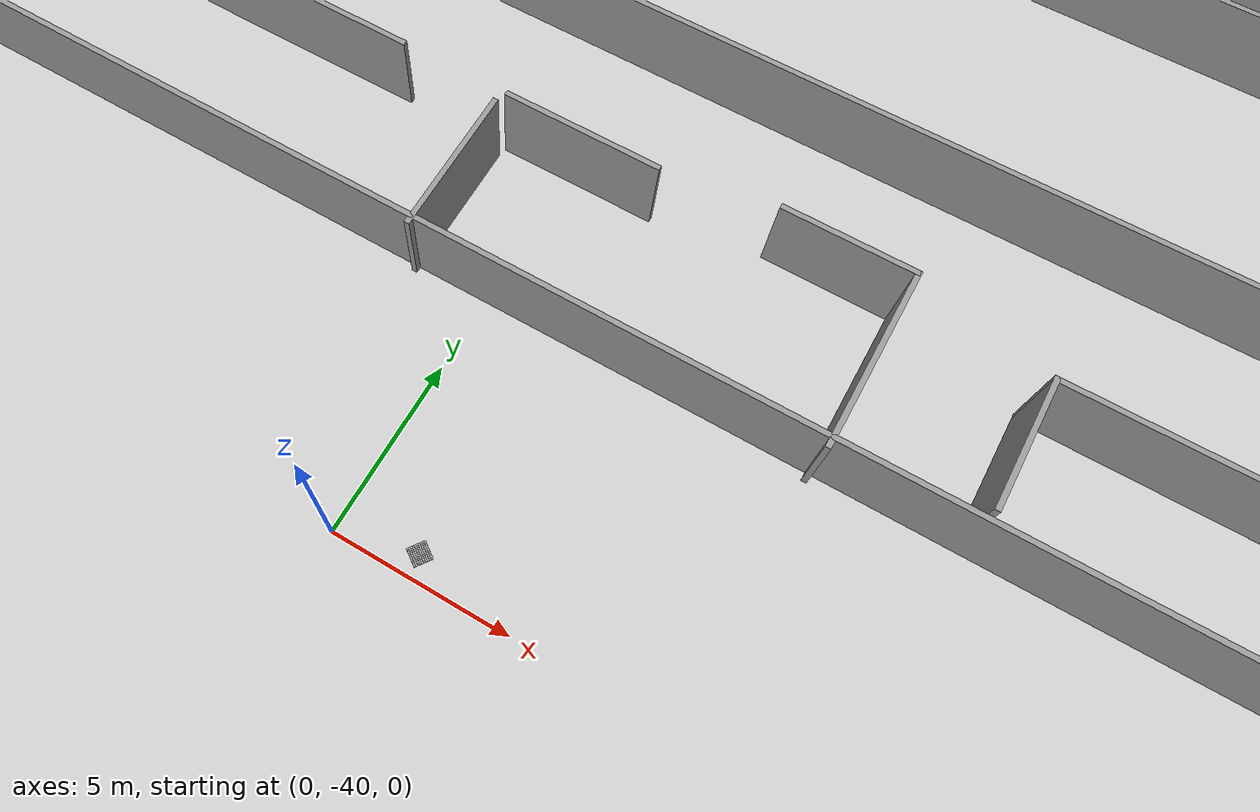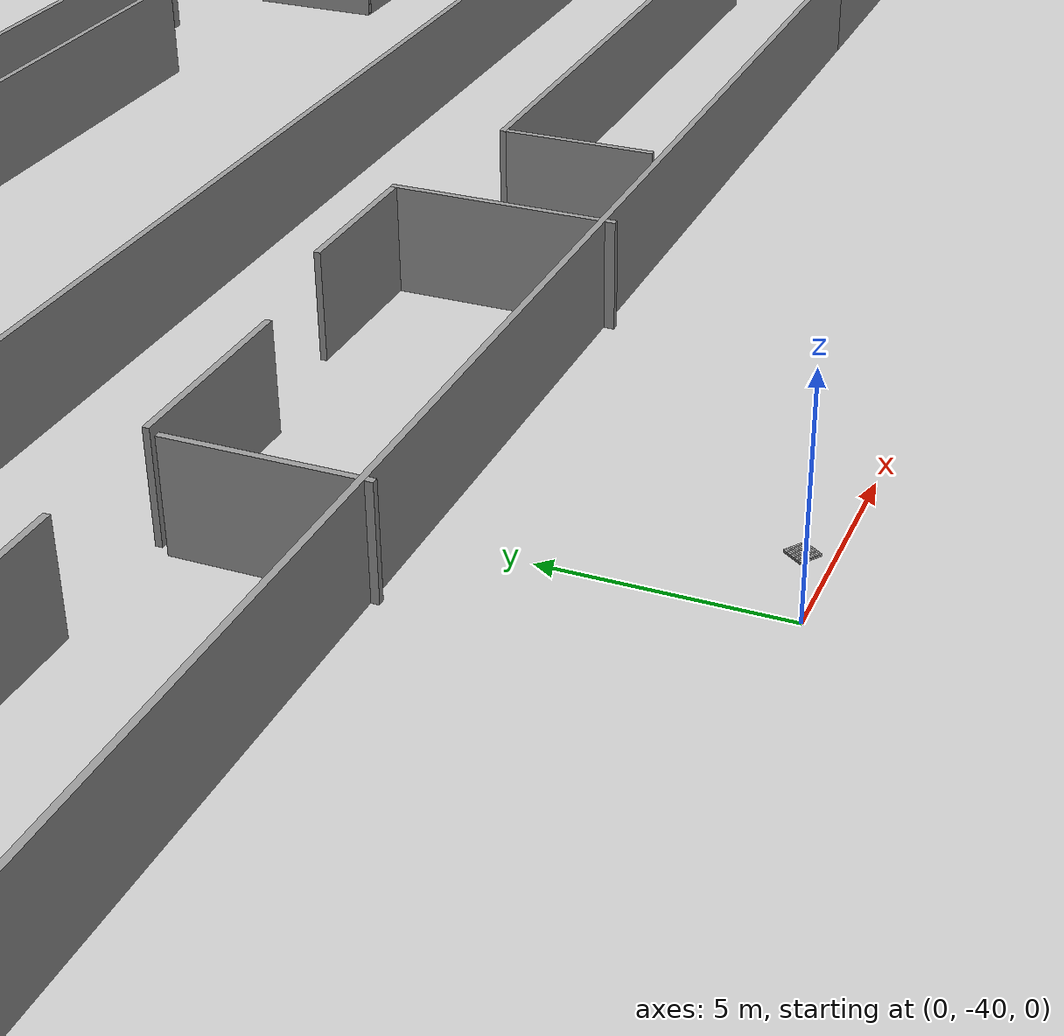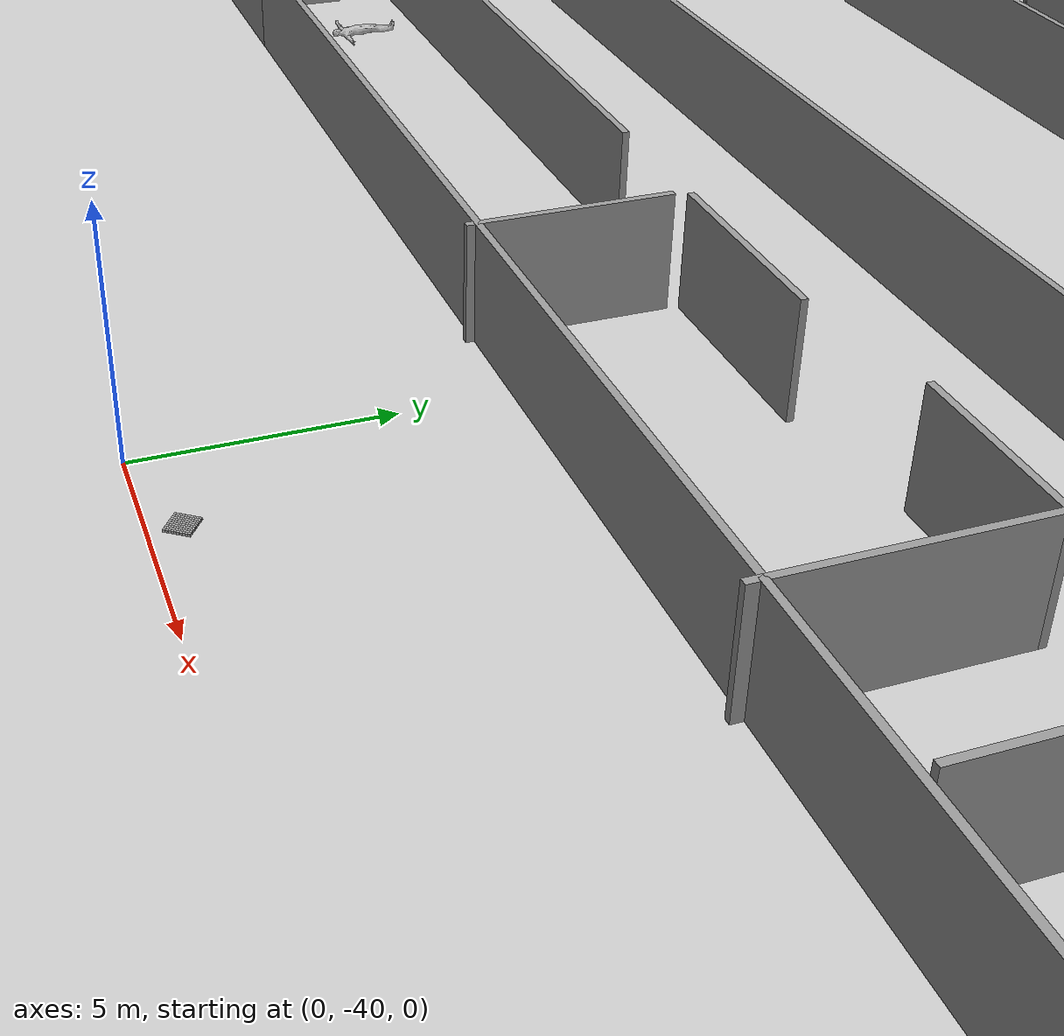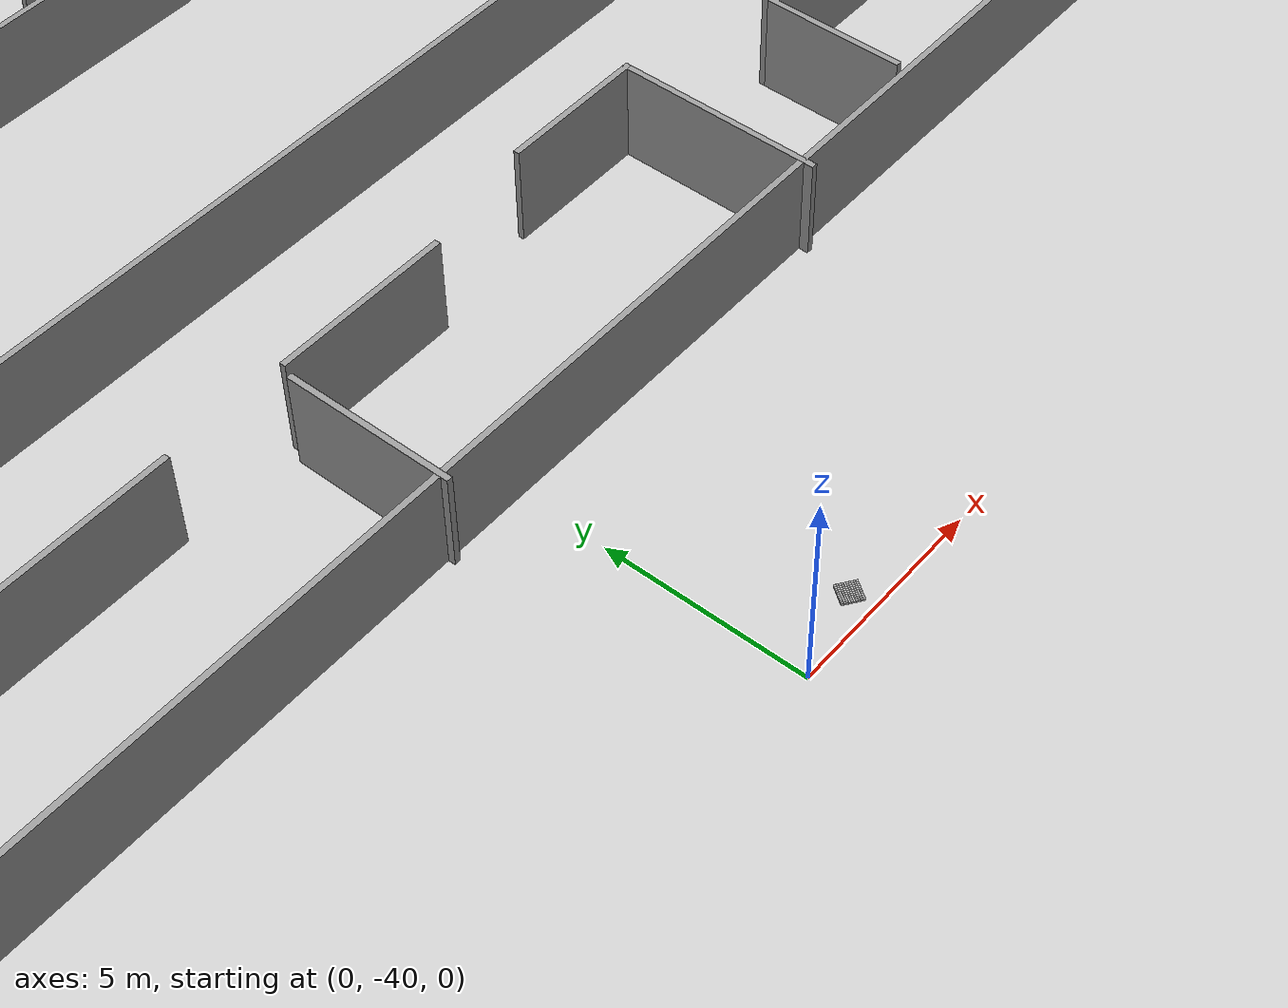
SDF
<sdf version="1.5">
 <world name="default">
  <model name="ground_plane">
   <static>1</static>
   <link name="link">
    <collision name="collision">
     <geometry><plane><normal>0 0 1</normal><size>100 100</size></plane></geometry>
     <surface><friction><ode><mu>100</mu><mu2>50</mu2></ode></friction></surface>
    </collision>
    <visual name="visual">
     <cast_shadows>0</cast_shadows>
     <geometry><plane><normal>0 0 1</normal><size>100 100</size></plane></geometry>
     <material>
      <script><uri>file://media/materials/scripts/gazebo.material</uri><name>Gazebo/Grey</name></script>
     </material>
    </visual>
   </link>
  </model>
  <light name="sun" type="directional">
   <pose>0 0 10 0 -0 0</pose>
   <diffuse>0.8 0.8 0.8 1</diffuse>
   <specular>0.2 0.2 0.2 1</specular>
   <attenuation>
    <range>1000</range>
    <constant>0.9</constant>
    <linear>0.01</linear>
    <quadratic>0.001</quadratic>
   </attenuation>
   <direction>-0.5 0.1 -0.9</direction>
  </light>
  <light name="my_light0" type="directional">
   <pose>0 0 30 0 -0 0</pose>
   <diffuse>0.5 0.5 0.5 1</diffuse>
   <specular>0.1 0.1 0.1 1</specular>
   <direction>0.1 0.1 -0.9</direction>
   <attenuation>
    <range>20</range>
    <linear>0.01</linear>
    <constant>0.5</constant>
    <quadratic>0.001</quadratic>
   </attenuation>
  </light>
  <physics name="default_physics" default="0" type="ode">
   <max_step_size>0.001</max_step_size>
   <real_time_factor>1</real_time_factor>
   <real_time_update_rate>1000</real_time_update_rate>
   <gravity>0 0 -9.8</gravity>
   <magnetic_field>5.5645e-06 2.28758e-05 -4.23884e-05</magnetic_field>
  </physics>
  <scene><ambient>0.4 0.4 0.4 1</ambient><background>0.7 0.7 0.7 1</background><shadows>1</shadows></scene>
  <spherical_coordinates>
   <surface_model>EARTH_WGS84</surface_model>
   <latitude_deg>0</latitude_deg>
   <longitude_deg>0</longitude_deg>
   <elevation>0</elevation>
   <heading_deg>0</heading_deg>
  </spherical_coordinates>
  <model name="BuildingDefaultName">
   <pose>0.623855 6.60233 0 0 -0 0</pose>
   <link name="Wall_10">
    <collision name="Wall_10_Collision">
     <geometry><box><size>47.5 0.15 2.5</size></box></geometry>
     <pose>0 0 1.25 0 -0 0</pose>
    </collision>
    <visual name="Wall_10_Visual">
     <pose>0 0 1.25 0 -0 0</pose>
     <geometry><box><size>47.5 0.15 2.5</size></box></geometry>
     <material>
      <script><uri>file://media/materials/scripts/gazebo.material</uri><name>Gazebo/Grey</name></script>
      <ambient>1 1 1 1</ambient>
     </material>
    </visual>
    <pose>3.48259 -39.3572 0 0 -0 0</pose>
   </link>
   <link name="Wall_100">
    <collision name="Wall_100_Collision">
     <geometry><box><size>7 0.15 2.5</size></box></geometry>
     <pose>0 0 1.25 0 -0 0</pose>
    </collision>
    <visual name="Wall_100_Visual">
     <pose>0 0 1.25 0 -0 0</pose>
     <geometry><box><size>7 0.15 2.5</size></box></geometry>
     <material>
      <script><uri>file://media/materials/scripts/gazebo.material</uri><name>Gazebo/Grey</name></script>
      <ambient>1 1 1 1</ambient>
     </material>
    </visual>
    <pose>-23.0162 2.8764 0 0 -0 0</pose>
   </link>
   <link name="Wall_101">
    <collision name="Wall_101_Collision">
     <geometry><box><size>8.75 0.15 2.5</size></box></geometry>
     <pose>0 0 1.25 0 -0 0</pose>
    </collision>
    <visual name="Wall_101_Visual">
     <pose>0 0 1.25 0 -0 0</pose>
     <geometry><box><size>8.75 0.15 2.5</size></box></geometry>
     <material>
      <script><uri>file://media/materials/scripts/gazebo.material</uri><name>Gazebo/Grey</name></script>
      <ambient>1 1 1 1</ambient>
     </material>
    </visual>
    <pose>-19.5912 -1.4236 0 0 0 -1.5708</pose>
   </link>
   <link name="Wall_102">
    <collision name="Wall_102_Collision">
     <geometry><box><size>7 0.15 2.5</size></box></geometry>
     <pose>0 0 1.25 0 -0 0</pose>
    </collision>
    <visual name="Wall_102_Visual">
     <pose>0 0 1.25 0 -0 0</pose>
     <geometry><box><size>7 0.15 2.5</size></box></geometry>
     <material>
      <script><uri>file://media/materials/scripts/gazebo.material</uri><name>Gazebo/Grey</name></script>
      <ambient>1 1 1 1</ambient>
     </material>
    </visual>
    <pose>-23.0162 -5.7236 0 0 -0 3.14159</pose>
   </link>
   <link name="Wall_104">
    <collision name="Wall_104_Collision">
     <geometry><box><size>4.5 0.15 2.5</size></box></geometry>
     <pose>0 0 1.25 0 -0 0</pose>
    </collision>
    <visual name="Wall_104_Visual">
     <pose>0 0 1.25 0 -0 0</pose>
     <geometry><box><size>4.5 0.15 2.5</size></box></geometry>
     <material>
      <script><uri>file://media/materials/scripts/gazebo.material</uri><name>Gazebo/Grey</name></script>
      <ambient>1 1 1 1</ambient>
     </material>
    </visual>
    <pose>-24.2662 -11.3117 0 0 -0 0</pose>
   </link>
   <link name="Wall_105">
    <collision name="Wall_105_Collision">
     <geometry><box><size>10.25 0.15 2.5</size></box></geometry>
     <pose>0 0 1.25 0 -0 0</pose>
    </collision>
    <visual name="Wall_105_Visual">
     <pose>0 0 1.25 0 -0 0</pose>
     <geometry><box><size>10.25 0.15 2.5</size></box></geometry>
     <material>
      <script><uri>file://media/materials/scripts/gazebo.material</uri><name>Gazebo/Grey</name></script>
      <ambient>1 1 1 1</ambient>
     </material>
    </visual>
    <pose>-22.0912 -16.3617 0 0 0 -1.5708</pose>
   </link>
   <link name="Wall_107">
    <collision name="Wall_107_Collision">
     <geometry><box><size>9.5 0.15 2.5</size></box></geometry>
     <pose>0 0 1.25 0 -0 0</pose>
    </collision>
    <visual name="Wall_107_Visual">
     <pose>0 0 1.25 0 -0 0</pose>
     <geometry><box><size>9.5 0.15 2.5</size></box></geometry>
     <material>
      <script><uri>file://media/materials/scripts/gazebo.material</uri><name>Gazebo/Grey</name></script>
      <ambient>1 1 1 1</ambient>
     </material>
    </visual>
    <pose>-17.2857 -16.7879 0 0 -0 0</pose>
   </link>
   <link name="Wall_108">
    <collision name="Wall_108_Collision">
     <geometry><box><size>3.75 0.15 2.5</size></box></geometry>
     <pose>0 0 1.25 0 -0 0</pose>
    </collision>
    <visual name="Wall_108_Visual">
     <pose>0 0 1.25 0 -0 0</pose>
     <geometry><box><size>3.75 0.15 2.5</size></box></geometry>
     <material>
      <script><uri>file://media/materials/scripts/gazebo.material</uri><name>Gazebo/Grey</name></script>
      <ambient>1 1 1 1</ambient>
     </material>
    </visual>
    <pose>-12.6107 -18.5879 0 0 0 -1.5708</pose>
   </link>
   <link name="Wall_109">
    <collision name="Wall_109_Collision">
     <geometry><box><size>11.5 0.15 2.5</size></box></geometry>
     <pose>0 0 1.25 0 -0 0</pose>
    </collision>
    <visual name="Wall_109_Visual">
     <pose>0 0 1.25 0 -0 0</pose>
     <geometry><box><size>11.5 0.15 2.5</size></box></geometry>
     <material>
      <script><uri>file://media/materials/scripts/gazebo.material</uri><name>Gazebo/Grey</name></script>
      <ambient>1 1 1 1</ambient>
     </material>
    </visual>
    <pose>-6.93569 -20.3879 0 0 -0 0</pose>
   </link>
   <link name="Wall_11">
    <collision name="Wall_11_Collision">
     <geometry><box><size>7.5 0.15 2.5</size></box></geometry>
     <pose>0 0 1.25 0 -0 0</pose>
    </collision>
    <visual name="Wall_11_Visual">
     <pose>0 0 1.25 0 -0 0</pose>
     <geometry><box><size>7.5 0.15 2.5</size></box></geometry>
     <material>
      <script><uri>file://media/materials/scripts/gazebo.material</uri><name>Gazebo/Grey</name></script>
      <ambient>1 1 1 1</ambient>
     </material>
    </visual>
    <pose>30.8326 -39.3572 0 0 -0 0</pose>
   </link>
   <link name="Wall_111">
    <collision name="Wall_111_Collision">
     <geometry><box><size>19.25 0.15 2.5</size></box></geometry>
     <pose>0 0 1.25 0 -0 0</pose>
    </collision>
    <visual name="Wall_111_Visual">
     <pose>0 0 1.25 0 -0 0</pose>
     <geometry><box><size>19.25 0.15 2.5</size></box></geometry>
     <material>
      <script><uri>file://media/materials/scripts/gazebo.material</uri><name>Gazebo/Grey</name></script>
      <ambient>1 1 1 1</ambient>
     </material>
    </visual>
    <pose>12.4808 -20.7705 0 0 -0 0</pose>
   </link>
   <link name="Wall_113">
    <collision name="Wall_113_Collision">
     <geometry><box><size>5.75 0.15 2.5</size></box></geometry>
     <pose>0 0 1.25 0 -0 0</pose>
    </collision>
    <visual name="Wall_113_Visual">
     <pose>0 0 1.25 0 -0 0</pose>
     <geometry><box><size>5.75 0.15 2.5</size></box></geometry>
     <material>
      <script><uri>file://media/materials/scripts/gazebo.material</uri><name>Gazebo/Grey</name></script>
      <ambient>1 1 1 1</ambient>
     </material>
    </visual>
    <pose>44.4434 -32.778 0 0 -0 3.14159</pose>
   </link>
   <link name="Wall_114">
    <collision name="Wall_114_Collision">
     <geometry><box><size>3.75 0.15 2.5</size></box></geometry>
     <pose>0 0 1.25 0 -0 0</pose>
    </collision>
    <visual name="Wall_114_Visual">
     <pose>0 0 1.25 0 -0 0</pose>
     <geometry><box><size>3.75 0.15 2.5</size></box></geometry>
     <material>
      <script><uri>file://media/materials/scripts/gazebo.material</uri><name>Gazebo/Grey</name></script>
      <ambient>1 1 1 1</ambient>
     </material>
    </visual>
    <pose>42.1093 -34.5166 0 0 0 -1.309</pose>
   </link>
   <link name="Wall_115">
    <collision name="Wall_115_Collision">
     <geometry><box><size>7.75 0.15 2.5</size></box></geometry>
     <pose>0 0 1.25 0 -0 0</pose>
    </collision>
    <visual name="Wall_115_Visual">
     <pose>0 0 1.25 0 -0 0</pose>
     <geometry><box><size>7.75 0.15 2.5</size></box></geometry>
     <material>
      <script><uri>file://media/materials/scripts/gazebo.material</uri><name>Gazebo/Grey</name></script>
      <ambient>1 1 1 1</ambient>
     </material>
    </visual>
    <pose>38.7752 -36.2553 0 0 -0 3.14159</pose>
   </link>
   <link name="Wall_117">
    <collision name="Wall_117_Collision">
     <geometry><box><size>17.5 0.15 2.5</size></box></geometry>
     <pose>0 0 1.25 0 -0 0</pose>
    </collision>
    <visual name="Wall_117_Visual">
     <pose>0 0 1.25 0 -0 0</pose>
     <geometry><box><size>17.5 0.15 2.5</size></box></geometry>
     <material>
      <script><uri>file://media/materials/scripts/gazebo.material</uri><name>Gazebo/Grey</name></script>
      <ambient>1 1 1 1</ambient>
     </material>
    </visual>
    <pose>21.1543 -35.4279 0 0 -0 3.14159</pose>
   </link>
   <link name="Wall_118">
    <collision name="Wall_118_Collision">
     <geometry><box><size>3.75 0.15 2.5</size></box></geometry>
     <pose>0 0 1.25 0 -0 0</pose>
    </collision>
    <visual name="Wall_118_Visual">
     <pose>0 0 1.25 0 -0 0</pose>
     <geometry><box><size>3.75 0.15 2.5</size></box></geometry>
     <material>
      <script><uri>file://media/materials/scripts/gazebo.material</uri><name>Gazebo/Grey</name></script>
      <ambient>1 1 1 1</ambient>
     </material>
    </visual>
    <pose>12.4793 -37.2279 0 0 0 -1.5708</pose>
   </link>
   <link name="Wall_12">
    <collision name="Wall_12_Collision">
     <geometry><box><size>13.5 0.15 2.5</size></box></geometry>
     <pose>0 0 1.25 0 -0 0</pose>
    </collision>
    <visual name="Wall_12_Visual">
     <pose>0 0 1.25 0 -0 0</pose>
     <geometry><box><size>13.5 0.15 2.5</size></box></geometry>
     <material>
      <script><uri>file://media/materials/scripts/gazebo.material</uri><name>Gazebo/Grey</name></script>
      <ambient>1 1 1 1</ambient>
     </material>
    </visual>
    <pose>41.1826 -39.3572 0 0 -0 0</pose>
   </link>
   <link name="Wall_121">
    <collision name="Wall_121_Collision">
     <geometry><box><size>5.25 0.15 2.5</size></box></geometry>
     <pose>0 0 1.25 0 -0 0</pose>
    </collision>
    <visual name="Wall_121_Visual">
     <pose>0 0 1.25 0 -0 0</pose>
     <geometry><box><size>5.25 0.15 2.5</size></box></geometry>
     <material>
      <script><uri>file://media/materials/scripts/gazebo.material</uri><name>Gazebo/Grey</name></script>
      <ambient>1 1 1 1</ambient>
     </material>
    </visual>
    <pose>8.62951 -37.0422 0 0 -0 1.5708</pose>
   </link>
   <link name="Wall_122">
    <collision name="Wall_122_Collision">
     <geometry><box><size>3.75 0.15 2.5</size></box></geometry>
     <pose>0 0 1.25 0 -0 0</pose>
    </collision>
    <visual name="Wall_122_Visual">
     <pose>0 0 1.25 0 -0 0</pose>
     <geometry><box><size>3.75 0.15 2.5</size></box></geometry>
     <material>
      <script><uri>file://media/materials/scripts/gazebo.material</uri><name>Gazebo/Grey</name></script>
      <ambient>1 1 1 1</ambient>
     </material>
    </visual>
    <pose>6.82951 -34.4922 0 0 -0 3.14159</pose>
   </link>
   <link name="Wall_124">
    <collision name="Wall_124_Collision">
     <geometry><box><size>4.5 0.15 2.5</size></box></geometry>
     <pose>0 0 1.25 0 -0 0</pose>
    </collision>
    <visual name="Wall_124_Visual">
     <pose>0 0 1.25 0 -0 0</pose>
     <geometry><box><size>4.5 0.15 2.5</size></box></geometry>
     <material>
      <script><uri>file://media/materials/scripts/gazebo.material</uri><name>Gazebo/Grey</name></script>
      <ambient>1 1 1 1</ambient>
     </material>
    </visual>
    <pose>-0.359709 -35.0494 0 0 -0 3.14159</pose>
   </link>
   <link name="Wall_127">
    <collision name="Wall_127_Collision">
     <geometry><box><size>4.25 0.15 2.5</size></box></geometry>
     <pose>0 0 1.25 0 -0 0</pose>
    </collision>
    <visual name="Wall_127_Visual">
     <pose>0 0 1.25 0 -0 0</pose>
     <geometry><box><size>4.25 0.15 2.5</size></box></geometry>
     <material>
      <script><uri>file://media/materials/scripts/gazebo.material</uri><name>Gazebo/Grey</name></script>
      <ambient>1 1 1 1</ambient>
     </material>
    </visual>
    <pose>-2.72752 -37.4779 0 0 0 -1.5708</pose>
   </link>
   <link name="Wall_130">
    <collision name="Wall_130_Collision">
     <geometry><box><size>16.75 0.15 2.5</size></box></geometry>
     <pose>0 0 1.25 0 -0 0</pose>
    </collision>
    <visual name="Wall_130_Visual">
     <pose>0 0 1.25 0 -0 0</pose>
     <geometry><box><size>16.75 0.15 2.5</size></box></geometry>
     <material>
      <script><uri>file://media/materials/scripts/gazebo.material</uri><name>Gazebo/Grey</name></script>
      <ambient>1 1 1 1</ambient>
     </material>
    </visual>
    <pose>-14.0561 -35.0494 0 0 -0 3.14159</pose>
   </link>
   <link name="Wall_131">
    <collision name="Wall_131_Collision">
     <geometry><box><size>3.75 0.15 2.5</size></box></geometry>
     <pose>0 0 1.25 0 -0 0</pose>
    </collision>
    <visual name="Wall_131_Visual">
     <pose>0 0 1.25 0 -0 0</pose>
     <geometry><box><size>3.75 0.15 2.5</size></box></geometry>
     <material>
      <script><uri>file://media/materials/scripts/gazebo.material</uri><name>Gazebo/Grey</name></script>
      <ambient>1 1 1 1</ambient>
     </material>
    </visual>
    <pose>-22.3561 -36.8494 0 0 0 -1.5708</pose>
   </link>
   <link name="Wall_133">
    <collision name="Wall_133_Collision">
     <geometry><box><size>91.25 0.15 2.5</size></box></geometry>
     <pose>0 0 1.25 0 -0 0</pose>
    </collision>
    <visual name="Wall_133_Visual">
     <pose>0 0 1.25 0 -0 0</pose>
     <geometry><box><size>91.25 0.15 2.5</size></box></geometry>
     <material>
      <script><uri>file://media/materials/scripts/gazebo.material</uri><name>Gazebo/Grey</name></script>
      <ambient>1 1 1 1</ambient>
     </material>
    </visual>
    <pose>-2.22711 34.6071 0 0 -0 0</pose>
   </link>
   <link name="Wall_134">
    <collision name="Wall_134_Collision">
     <geometry><box><size>3 0.15 2.5</size></box></geometry>
     <pose>0 0 1.25 0 -0 0</pose>
    </collision>
    <visual name="Wall_134_Visual">
     <pose>0 0 1.25 0 -0 0</pose>
     <geometry><box><size>3 0.15 2.5</size></box></geometry>
     <material>
      <script><uri>file://media/materials/scripts/gazebo.material</uri><name>Gazebo/Grey</name></script>
      <ambient>1 1 1 1</ambient>
     </material>
    </visual>
    <pose>43.3229 33.1821 0 0 0 -1.5708</pose>
   </link>
   <link name="Wall_14">
    <collision name="Wall_14_Collision">
     <geometry><box><size>28 0.15 2.5</size></box></geometry>
     <pose>0 0 1.25 0 -0 0</pose>
    </collision>
    <visual name="Wall_14_Visual">
     <pose>0 0 1.25 0 -0 0</pose>
     <geometry><box><size>28 0.15 2.5</size></box></geometry>
     <material>
      <script><uri>file://media/materials/scripts/gazebo.material</uri><name>Gazebo/Grey</name></script>
      <ambient>1 1 1 1</ambient>
     </material>
    </visual>
    <pose>-33.4681 -39.3572 0 0 -0 3.14159</pose>
   </link>
   <link name="Wall_15">
    <collision name="Wall_15_Collision">
     <geometry><box><size>68.5 0.15 2.5</size></box></geometry>
     <pose>0 0 1.25 0 -0 0</pose>
    </collision>
    <visual name="Wall_15_Visual">
     <pose>0 0 1.25 0 -0 0</pose>
     <geometry><box><size>68.5 0.15 2.5</size></box></geometry>
     <material>
      <script><uri>file://media/materials/scripts/gazebo.material</uri><name>Gazebo/Grey</name></script>
      <ambient>1 1 1 1</ambient>
     </material>
    </visual>
    <pose>-47.3931 -5.18218 0 0 -0 1.5708</pose>
   </link>
   <link name="Wall_17">
    <collision name="Wall_17_Collision">
     <geometry><box><size>11.5 0.15 2.5</size></box></geometry>
     <pose>0 0 1.25 0 -0 0</pose>
    </collision>
    <visual name="Wall_17_Visual">
     <pose>0 0 1.25 0 -0 0</pose>
     <geometry><box><size>11.5 0.15 2.5</size></box></geometry>
     <material>
      <script><uri>file://media/materials/scripts/gazebo.material</uri><name>Gazebo/Grey</name></script>
      <ambient>1 1 1 1</ambient>
     </material>
    </visual>
    <pose>-47.8576 33.9172 0 0 -0 1.5708</pose>
   </link>
   <link name="Wall_18">
    <collision name="Wall_18_Collision">
     <geometry><box><size>94.75 0.15 2.5</size></box></geometry>
     <pose>0 0 1.25 0 -0 0</pose>
    </collision>
    <visual name="Wall_18_Visual">
     <pose>0 0 1.25 0 -0 0</pose>
     <geometry><box><size>94.75 0.15 2.5</size></box></geometry>
     <material>
      <script><uri>file://media/materials/scripts/gazebo.material</uri><name>Gazebo/Grey</name></script>
      <ambient>1 1 1 1</ambient>
     </material>
    </visual>
    <pose>-0.557591 39.5922 0 0 -0 0</pose>
   </link>
   <link name="Wall_19">
    <collision name="Wall_19_Collision">
     <geometry><box><size>79 0.15 2.5</size></box></geometry>
     <pose>0 0 1.25 0 -0 0</pose>
    </collision>
    <visual name="Wall_19_Visual">
     <pose>0 0 1.25 0 -0 0</pose>
     <geometry><box><size>79 0.15 2.5</size></box></geometry>
     <material>
      <script><uri>file://media/materials/scripts/gazebo.material</uri><name>Gazebo/Grey</name></script>
      <ambient>1 1 1 1</ambient>
     </material>
    </visual>
    <pose>46.7424 0.167188 0 0 0 -1.5708</pose>
   </link>
   <link name="Wall_21">
    <collision name="Wall_21_Collision">
     <geometry><box><size>34.5 0.15 2.5</size></box></geometry>
     <pose>0 0 1.25 0 -0 0</pose>
    </collision>
    <visual name="Wall_21_Visual">
     <pose>0 0 1.25 0 -0 0</pose>
     <geometry><box><size>34.5 0.15 2.5</size></box></geometry>
     <material>
      <script><uri>file://media/materials/scripts/gazebo.material</uri><name>Gazebo/Grey</name></script>
      <ambient>1 1 1 1</ambient>
     </material>
    </visual>
    <pose>1.77247 -14.0276 0 0 -0 0</pose>
   </link>
   <link name="Wall_22">
    <collision name="Wall_22_Collision">
     <geometry><box><size>27 0.15 2.5</size></box></geometry>
     <pose>0 0 1.25 0 -0 0</pose>
    </collision>
    <visual name="Wall_22_Visual">
     <pose>0 0 1.25 0 -0 0</pose>
     <geometry><box><size>27 0.15 2.5</size></box></geometry>
     <material>
      <script><uri>file://media/materials/scripts/gazebo.material</uri><name>Gazebo/Grey</name></script>
      <ambient>1 1 1 1</ambient>
     </material>
    </visual>
    <pose>18.9475 -0.602588 0 0 -0 1.5708</pose>
   </link>
   <link name="Wall_23">
    <collision name="Wall_23_Collision">
     <geometry><box><size>34.75 0.15 2.5</size></box></geometry>
     <pose>0 0 1.25 0 -0 0</pose>
    </collision>
    <visual name="Wall_23_Visual">
     <pose>0 0 1.25 0 -0 0</pose>
     <geometry><box><size>34.75 0.15 2.5</size></box></geometry>
     <material>
      <script><uri>file://media/materials/scripts/gazebo.material</uri><name>Gazebo/Grey</name></script>
      <ambient>1 1 1 1</ambient>
     </material>
    </visual>
    <pose>1.64747 12.8224 0 0 -0 3.14159</pose>
   </link>
   <link name="Wall_24">
    <collision name="Wall_24_Collision">
     <geometry><box><size>20.75 0.15 2.5</size></box></geometry>
     <pose>0 0 1.25 0 -0 0</pose>
    </collision>
    <visual name="Wall_24_Visual">
     <pose>0 0 1.25 0 -0 0</pose>
     <geometry><box><size>20.75 0.15 2.5</size></box></geometry>
     <material>
      <script><uri>file://media/materials/scripts/gazebo.material</uri><name>Gazebo/Grey</name></script>
      <ambient>1 1 1 1</ambient>
     </material>
    </visual>
    <pose>-15.6525 2.52241 0 0 0 -1.5708</pose>
   </link>
   <link name="Wall_26">
    <collision name="Wall_26_Collision">
     <geometry><box><size>45.5 0.15 2.5</size></box></geometry>
     <pose>0 0 1.25 0 -0 0</pose>
    </collision>
    <visual name="Wall_26_Visual">
     <pose>0 0 1.25 0 -0 0</pose>
     <geometry><box><size>45.5 0.15 2.5</size></box></geometry>
     <material>
      <script><uri>file://media/materials/scripts/gazebo.material</uri><name>Gazebo/Grey</name></script>
      <ambient>1 1 1 1</ambient>
     </material>
    </visual>
    <pose>-4.00641 -22.7347 0 0 -0 3.14159</pose>
   </link>
   <link name="Wall_27">
    <collision name="Wall_27_Collision">
     <geometry><box><size>44 0.15 2.5</size></box></geometry>
     <pose>0 0 1.25 0 -0 0</pose>
    </collision>
    <visual name="Wall_27_Visual">
     <pose>0 0 1.25 0 -0 0</pose>
     <geometry><box><size>44 0.15 2.5</size></box></geometry>
     <material>
      <script><uri>file://media/materials/scripts/gazebo.material</uri><name>Gazebo/Grey</name></script>
      <ambient>1 1 1 1</ambient>
     </material>
    </visual>
    <pose>-26.6814 -0.809651 0 0 -0 1.5708</pose>
   </link>
   <link name="Wall_28">
    <collision name="Wall_28_Collision">
     <geometry><box><size>57.5 0.15 2.5</size></box></geometry>
     <pose>0 0 1.25 0 -0 0</pose>
    </collision>
    <visual name="Wall_28_Visual">
     <pose>0 0 1.25 0 -0 0</pose>
     <geometry><box><size>57.5 0.15 2.5</size></box></geometry>
     <material>
      <script><uri>file://media/materials/scripts/gazebo.material</uri><name>Gazebo/Grey</name></script>
      <ambient>1 1 1 1</ambient>
     </material>
    </visual>
    <pose>1.99358 21.1153 0 0 -0 0</pose>
   </link>
   <link name="Wall_29">
    <collision name="Wall_29_Collision">
     <geometry><box><size>43.5 0.15 2.5</size></box></geometry>
     <pose>0 0 1.25 0 -0 0</pose>
    </collision>
    <visual name="Wall_29_Visual">
     <pose>0 0 1.25 0 -0 0</pose>
     <geometry><box><size>43.5 0.15 2.5</size></box></geometry>
     <material>
      <script><uri>file://media/materials/scripts/gazebo.material</uri><name>Gazebo/Grey</name></script>
      <ambient>1 1 1 1</ambient>
     </material>
    </visual>
    <pose>30.6686 -0.559651 0 0 0 -1.5708</pose>
   </link>
   <link name="Wall_31">
    <collision name="Wall_31_Collision">
     <geometry><box><size>76.75 0.15 2.5</size></box></geometry>
     <pose>0 0 1.25 0 -0 0</pose>
    </collision>
    <visual name="Wall_31_Visual">
     <pose>0 0 1.25 0 -0 0</pose>
     <geometry><box><size>76.75 0.15 2.5</size></box></geometry>
     <material>
      <script><uri>file://media/materials/scripts/gazebo.material</uri><name>Gazebo/Grey</name></script>
      <ambient>1 1 1 1</ambient>
     </material>
    </visual>
    <pose>-0.324449 -30.6846 0 0 -0 3.14159</pose>
   </link>
   <link name="Wall_32">
    <collision name="Wall_32_Collision">
     <geometry><box><size>60.25 0.15 2.5</size></box></geometry>
     <pose>0 0 1.25 0 -0 0</pose>
    </collision>
    <visual name="Wall_32_Visual">
     <pose>0 0 1.25 0 -0 0</pose>
     <geometry><box><size>60.25 0.15 2.5</size></box></geometry>
     <material>
      <script><uri>file://media/materials/scripts/gazebo.material</uri><name>Gazebo/Grey</name></script>
      <ambient>1 1 1 1</ambient>
     </material>
    </visual>
    <pose>-38.6244 -0.634578 0 0 -0 1.5708</pose>
   </link>
   <link name="Wall_33">
    <collision name="Wall_33_Collision">
     <geometry><box><size>58.5 0.15 2.5</size></box></geometry>
     <pose>0 0 1.25 0 -0 0</pose>
    </collision>
    <visual name="Wall_33_Visual">
     <pose>0 0 1.25 0 -0 0</pose>
     <geometry><box><size>58.5 0.15 2.5</size></box></geometry>
     <material>
      <script><uri>file://media/materials/scripts/gazebo.material</uri><name>Gazebo/Grey</name></script>
      <ambient>1 1 1 1</ambient>
     </material>
    </visual>
    <pose>-9.44945 29.4154 0 0 -0 0</pose>
   </link>
   <link name="Wall_36">
    <collision name="Wall_36_Collision">
     <geometry><box><size>58.5 0.15 2.5</size></box></geometry>
     <pose>0 0 1.25 0 -0 0</pose>
    </collision>
    <visual name="Wall_36_Visual">
     <pose>0 0 1.25 0 -0 0</pose>
     <geometry><box><size>58.5 0.15 2.5</size></box></geometry>
     <material>
      <script><uri>file://media/materials/scripts/gazebo.material</uri><name>Gazebo/Grey</name></script>
      <ambient>1 1 1 1</ambient>
     </material>
    </visual>
    <pose>37.9755 -1.13101 0 0 -0 1.5708</pose>
   </link>
   <link name="Wall_38">
    <collision name="Wall_38_Collision">
     <geometry><box><size>8 0.15 2.5</size></box></geometry>
     <pose>0 0 1.25 0 -0 0</pose>
    </collision>
    <visual name="Wall_38_Visual">
     <pose>0 0 1.25 0 -0 0</pose>
     <geometry><box><size>8 0.15 2.5</size></box></geometry>
     <material>
      <script><uri>file://media/materials/scripts/gazebo.material</uri><name>Gazebo/Grey</name></script>
      <ambient>1 1 1 1</ambient>
     </material>
    </visual>
    <pose>-11.2696 5.78374 0 0 -0 0</pose>
   </link>
   <link name="Wall_40">
    <collision name="Wall_40_Collision">
     <geometry><box><size>21.25 0.15 2.5</size></box></geometry>
     <pose>0 0 1.25 0 -0 0</pose>
    </collision>
    <visual name="Wall_40_Visual">
     <pose>0 0 1.25 0 -0 0</pose>
     <geometry><box><size>21.25 0.15 2.5</size></box></geometry>
     <material>
      <script><uri>file://media/materials/scripts/gazebo.material</uri><name>Gazebo/Grey</name></script>
      <ambient>1 1 1 1</ambient>
     </material>
    </visual>
    <pose>3.30431 8.21804 0 0 -0 0</pose>
   </link>
   <link name="Wall_41">
    <collision name="Wall_41_Collision">
     <geometry><box><size>18 0.15 2.5</size></box></geometry>
     <pose>0 0 1.25 0 -0 0</pose>
    </collision>
    <visual name="Wall_41_Visual">
     <pose>0 0 1.25 0 -0 0</pose>
     <geometry><box><size>18 0.15 2.5</size></box></geometry>
     <material>
      <script><uri>file://media/materials/scripts/gazebo.material</uri><name>Gazebo/Grey</name></script>
      <ambient>1 1 1 1</ambient>
     </material>
    </visual>
    <pose>13.8543 -0.70696 0 0 0 -1.5708</pose>
   </link>
   <link name="Wall_42">
    <collision name="Wall_42_Collision">
     <geometry><box><size>6 0.15 2.5</size></box></geometry>
     <pose>0 0 1.25 0 -0 0</pose>
    </collision>
    <visual name="Wall_42_Visual">
     <pose>0 0 1.25 0 -0 0</pose>
     <geometry><box><size>6 0.15 2.5</size></box></geometry>
     <material>
      <script><uri>file://media/materials/scripts/gazebo.material</uri><name>Gazebo/Grey</name></script>
      <ambient>1 1 1 1</ambient>
     </material>
    </visual>
    <pose>10.9293 -9.63196 0 0 -0 3.14159</pose>
   </link>
   <link name="Wall_43">
    <collision name="Wall_43_Collision">
     <geometry><box><size>8.25 0.15 2.5</size></box></geometry>
     <pose>0 0 1.25 0 -0 0</pose>
    </collision>
    <visual name="Wall_43_Visual">
     <pose>0 0 1.25 0 -0 0</pose>
     <geometry><box><size>8.25 0.15 2.5</size></box></geometry>
     <material>
      <script><uri>file://media/materials/scripts/gazebo.material</uri><name>Gazebo/Grey</name></script>
      <ambient>1 1 1 1</ambient>
     </material>
    </visual>
    <pose>8.00431 -5.58196 0 0 -0 1.5708</pose>
   </link>
   <link name="Wall_44">
    <collision name="Wall_44_Collision">
     <geometry><box><size>3.25 0.15 2.5</size></box></geometry>
     <pose>0 0 1.25 0 -0 0</pose>
    </collision>
    <visual name="Wall_44_Visual">
     <pose>0 0 1.25 0 -0 0</pose>
     <geometry><box><size>3.25 0.15 2.5</size></box></geometry>
     <material>
      <script><uri>file://media/materials/scripts/gazebo.material</uri><name>Gazebo/Grey</name></script>
      <ambient>1 1 1 1</ambient>
     </material>
    </visual>
    <pose>9.55431 -1.53196 0 0 -0 0</pose>
   </link>
   <link name="Wall_46">
    <collision name="Wall_46_Collision">
     <geometry><box><size>15.75 0.15 2.5</size></box></geometry>
     <pose>0 0 1.25 0 -0 0</pose>
    </collision>
    <visual name="Wall_46_Visual">
     <pose>0 0 1.25 0 -0 0</pose>
     <geometry><box><size>15.75 0.15 2.5</size></box></geometry>
     <material>
      <script><uri>file://media/materials/scripts/gazebo.material</uri><name>Gazebo/Grey</name></script>
      <ambient>1 1 1 1</ambient>
     </material>
    </visual>
    <pose>3.32366 0.01403 0 0 0 -1.5708</pose>
   </link>
   <link name="Wall_47">
    <collision name="Wall_47_Collision">
     <geometry><box><size>10.25 0.15 2.5</size></box></geometry>
     <pose>0 0 1.25 0 -0 0</pose>
    </collision>
    <visual name="Wall_47_Visual">
     <pose>0 0 1.25 0 -0 0</pose>
     <geometry><box><size>10.25 0.15 2.5</size></box></geometry>
     <material>
      <script><uri>file://media/materials/scripts/gazebo.material</uri><name>Gazebo/Grey</name></script>
      <ambient>1 1 1 1</ambient>
     </material>
    </visual>
    <pose>-1.72634 -7.78597 0 0 -0 3.14159</pose>
   </link>
   <link name="Wall_48">
    <collision name="Wall_48_Collision">
     <geometry><box><size>9 0.15 2.5</size></box></geometry>
     <pose>0 0 1.25 0 -0 0</pose>
    </collision>
    <visual name="Wall_48_Visual">
     <pose>0 0 1.25 0 -0 0</pose>
     <geometry><box><size>9 0.15 2.5</size></box></geometry>
     <material>
      <script><uri>file://media/materials/scripts/gazebo.material</uri><name>Gazebo/Grey</name></script>
      <ambient>1 1 1 1</ambient>
     </material>
    </visual>
    <pose>-6.77634 -3.36097 0 0 -0 1.5708</pose>
   </link>
   <link name="Wall_50">
    <collision name="Wall_50_Collision">
     <geometry><box><size>4.5 0.15 2.5</size></box></geometry>
     <pose>0 0 1.25 0 -0 0</pose>
    </collision>
    <visual name="Wall_50_Visual">
     <pose>0 0 1.25 0 -0 0</pose>
     <geometry><box><size>4.5 0.15 2.5</size></box></geometry>
     <material>
      <script><uri>file://media/materials/scripts/gazebo.material</uri><name>Gazebo/Grey</name></script>
      <ambient>1 1 1 1</ambient>
     </material>
    </visual>
    <pose>-13.1698 -0.841406 0 0 -0 0</pose>
   </link>
   <link name="Wall_51">
    <collision name="Wall_51_Collision">
     <geometry><box><size>5.25 0.15 2.5</size></box></geometry>
     <pose>0 0 1.25 0 -0 0</pose>
    </collision>
    <visual name="Wall_51_Visual">
     <pose>0 0 1.25 0 -0 0</pose>
     <geometry><box><size>5.25 0.15 2.5</size></box></geometry>
     <material>
      <script><uri>file://media/materials/scripts/gazebo.material</uri><name>Gazebo/Grey</name></script>
      <ambient>1 1 1 1</ambient>
     </material>
    </visual>
    <pose>-10.9948 -3.39141 0 0 0 -1.5708</pose>
   </link>
   <link name="Wall_52">
    <collision name="Wall_52_Collision">
     <geometry><box><size>2.75 0.15 2.5</size></box></geometry>
     <pose>0 0 1.25 0 -0 0</pose>
    </collision>
    <visual name="Wall_52_Visual">
     <pose>0 0 1.25 0 -0 0</pose>
     <geometry><box><size>2.75 0.15 2.5</size></box></geometry>
     <material>
      <script><uri>file://media/materials/scripts/gazebo.material</uri><name>Gazebo/Grey</name></script>
      <ambient>1 1 1 1</ambient>
     </material>
    </visual>
    <pose>-12.2948 -5.94141 0 0 -0 3.14159</pose>
   </link>
   <link name="Wall_54">
    <collision name="Wall_54_Collision">
     <geometry><box><size>2.5 0.15 2.5</size></box></geometry>
     <pose>0 0 1.25 0 -0 0</pose>
    </collision>
    <visual name="Wall_54_Visual">
     <pose>0 0 1.25 0 -0 0</pose>
     <geometry><box><size>2.5 0.15 2.5</size></box></geometry>
     <material>
      <script><uri>file://media/materials/scripts/gazebo.material</uri><name>Gazebo/Grey</name></script>
      <ambient>1 1 1 1</ambient>
     </material>
    </visual>
    <pose>-37.195 20.957 0 0 -0 0</pose>
   </link>
   <link name="Wall_58">
    <collision name="Wall_58_Collision">
     <geometry><box><size>3.25 0.15 2.5</size></box></geometry>
     <pose>0 0 1.25 0 -0 0</pose>
    </collision>
    <visual name="Wall_58_Visual">
     <pose>0 0 1.25 0 -0 0</pose>
     <geometry><box><size>3.25 0.15 2.5</size></box></geometry>
     <material>
      <script><uri>file://media/materials/scripts/gazebo.material</uri><name>Gazebo/Grey</name></script>
      <ambient>1 1 1 1</ambient>
     </material>
    </visual>
    <pose>-33.9087 12.6557 0 0 -0 3.14159</pose>
   </link>
   <link name="Wall_59">
    <collision name="Wall_59_Collision">
     <geometry><box><size>10.5 0.15 2.5</size></box></geometry>
     <pose>0 0 1.25 0 -0 0</pose>
    </collision>
    <visual name="Wall_59_Visual">
     <pose>0 0 1.25 0 -0 0</pose>
     <geometry><box><size>10.5 0.15 2.5</size></box></geometry>
     <material>
      <script><uri>file://media/materials/scripts/gazebo.material</uri><name>Gazebo/Grey</name></script>
      <ambient>1 1 1 1</ambient>
     </material>
    </visual>
    <pose>-35.4587 7.48069 0 0 0 -1.5708</pose>
   </link>
   <link name="Wall_60">
    <collision name="Wall_60_Collision">
     <geometry><box><size>4 0.15 2.5</size></box></geometry>
     <pose>0 0 1.25 0 -0 0</pose>
    </collision>
    <visual name="Wall_60_Visual">
     <pose>0 0 1.25 0 -0 0</pose>
     <geometry><box><size>4 0.15 2.5</size></box></geometry>
     <material>
      <script><uri>file://media/materials/scripts/gazebo.material</uri><name>Gazebo/Grey</name></script>
      <ambient>1 1 1 1</ambient>
     </material>
    </visual>
    <pose>-33.5337 2.30569 0 0 -0 0</pose>
   </link>
   <link name="Wall_61">
    <collision name="Wall_61_Collision">
     <geometry><box><size>2.75 0.15 2.5</size></box></geometry>
     <pose>0 0 1.25 0 -0 0</pose>
    </collision>
    <visual name="Wall_61_Visual">
     <pose>0 0 1.25 0 -0 0</pose>
     <geometry><box><size>2.75 0.15 2.5</size></box></geometry>
     <material>
      <script><uri>file://media/materials/scripts/gazebo.material</uri><name>Gazebo/Grey</name></script>
      <ambient>1 1 1 1</ambient>
     </material>
    </visual>
    <pose>-31.6087 1.00569 0 0 0 -1.5708</pose>
   </link>
   <link name="Wall_63">
    <collision name="Wall_63_Collision">
     <geometry><box><size>8 0.15 2.5</size></box></geometry>
     <pose>0 0 1.25 0 -0 0</pose>
    </collision>
    <visual name="Wall_63_Visual">
     <pose>0 0 1.25 0 -0 0</pose>
     <geometry><box><size>8 0.15 2.5</size></box></geometry>
     <material>
      <script><uri>file://media/materials/scripts/gazebo.material</uri><name>Gazebo/Grey</name></script>
      <ambient>1 1 1 1</ambient>
     </material>
    </visual>
    <pose>-30.9275 -11.0207 0 0 0 -1.5708</pose>
   </link>
   <link name="Wall_64">
    <collision name="Wall_64_Collision">
     <geometry><box><size>4 0.15 2.5</size></box></geometry>
     <pose>0 0 1.25 0 -0 0</pose>
    </collision>
    <visual name="Wall_64_Visual">
     <pose>0 0 1.25 0 -0 0</pose>
     <geometry><box><size>4 0.15 2.5</size></box></geometry>
     <material>
      <script><uri>file://media/materials/scripts/gazebo.material</uri><name>Gazebo/Grey</name></script>
      <ambient>1 1 1 1</ambient>
     </material>
    </visual>
    <pose>-32.8525 -14.9457 0 0 -0 3.14159</pose>
   </link>
   <link name="Wall_66">
    <collision name="Wall_66_Collision">
     <geometry><box><size>6.25 0.15 2.5</size></box></geometry>
     <pose>0 0 1.25 0 -0 0</pose>
    </collision>
    <visual name="Wall_66_Visual">
     <pose>0 0 1.25 0 -0 0</pose>
     <geometry><box><size>6.25 0.15 2.5</size></box></geometry>
     <material>
      <script><uri>file://media/materials/scripts/gazebo.material</uri><name>Gazebo/Grey</name></script>
      <ambient>1 1 1 1</ambient>
     </material>
    </visual>
    <pose>-34.4612 -22.8395 0 0 -0 0</pose>
   </link>
   <link name="Wall_67">
    <collision name="Wall_67_Collision">
     <geometry><box><size>3.5 0.15 2.5</size></box></geometry>
     <pose>0 0 1.25 0 -0 0</pose>
    </collision>
    <visual name="Wall_67_Visual">
     <pose>0 0 1.25 0 -0 0</pose>
     <geometry><box><size>3.5 0.15 2.5</size></box></geometry>
     <material>
      <script><uri>file://media/materials/scripts/gazebo.material</uri><name>Gazebo/Grey</name></script>
      <ambient>1 1 1 1</ambient>
     </material>
    </visual>
    <pose>-31.4112 -21.1645 0 0 -0 1.5708</pose>
   </link>
   <link name="Wall_71">
    <collision name="Wall_71_Collision">
     <geometry><box><size>5 0.15 2.5</size></box></geometry>
     <pose>0 0 1.25 0 -0 0</pose>
    </collision>
    <visual name="Wall_71_Visual">
     <pose>0 0 1.25 0 -0 0</pose>
     <geometry><box><size>5 0.15 2.5</size></box></geometry>
     <material>
      <script><uri>file://media/materials/scripts/gazebo.material</uri><name>Gazebo/Grey</name></script>
      <ambient>1 1 1 1</ambient>
     </material>
    </visual>
    <pose>44.388 -25.905 0 0 -0 3.14159</pose>
   </link>
   <link name="Wall_72">
    <collision name="Wall_72_Collision">
     <geometry><box><size>10.25 0.15 2.5</size></box></geometry>
     <pose>0 0 1.25 0 -0 0</pose>
    </collision>
    <visual name="Wall_72_Visual">
     <pose>0 0 1.25 0 -0 0</pose>
     <geometry><box><size>10.25 0.15 2.5</size></box></geometry>
     <material>
      <script><uri>file://media/materials/scripts/gazebo.material</uri><name>Gazebo/Grey</name></script>
      <ambient>1 1 1 1</ambient>
     </material>
    </visual>
    <pose>41.963 -20.855 0 0 -0 1.5708</pose>
   </link>
   <link name="Wall_75">
    <collision name="Wall_75_Collision">
     <geometry><box><size>4.75 0.15 2.5</size></box></geometry>
     <pose>0 0 1.25 0 -0 0</pose>
    </collision>
    <visual name="Wall_75_Visual">
     <pose>0 0 1.25 0 -0 0</pose>
     <geometry><box><size>4.75 0.15 2.5</size></box></geometry>
     <material>
      <script><uri>file://media/materials/scripts/gazebo.material</uri><name>Gazebo/Grey</name></script>
      <ambient>1 1 1 1</ambient>
     </material>
    </visual>
    <pose>44.8219 -9.55677 0 0 -0 0</pose>
   </link>
   <link name="Wall_77">
    <collision name="Wall_77_Collision">
     <geometry><box><size>11.25 0.15 2.5</size></box></geometry>
     <pose>0 0 1.25 0 -0 0</pose>
    </collision>
    <visual name="Wall_77_Visual">
     <pose>0 0 1.25 0 -0 0</pose>
     <geometry><box><size>11.25 0.15 2.5</size></box></geometry>
     <material>
      <script><uri>file://media/materials/scripts/gazebo.material</uri><name>Gazebo/Grey</name></script>
      <ambient>1 1 1 1</ambient>
     </material>
    </visual>
    <pose>43.3807 -4.00677 0 0 -0 1.5708</pose>
   </link>
   <link name="Wall_79">
    <collision name="Wall_79_Collision">
     <geometry><box><size>5.25 0.15 2.5</size></box></geometry>
     <pose>0 0 1.25 0 -0 0</pose>
    </collision>
    <visual name="Wall_79_Visual">
     <pose>0 0 1.25 0 -0 0</pose>
     <geometry><box><size>5.25 0.15 2.5</size></box></geometry>
     <material>
      <script><uri>file://media/materials/scripts/gazebo.material</uri><name>Gazebo/Grey</name></script>
      <ambient>1 1 1 1</ambient>
     </material>
    </visual>
    <pose>43.6932 5.61457 0 0 -0 3.14159</pose>
   </link>
   <link name="Wall_80">
    <collision name="Wall_80_Collision">
     <geometry><box><size>8.5 0.15 2.5</size></box></geometry>
     <pose>0 0 1.25 0 -0 0</pose>
    </collision>
    <visual name="Wall_80_Visual">
     <pose>0 0 1.25 0 -0 0</pose>
     <geometry><box><size>8.5 0.15 2.5</size></box></geometry>
     <material>
      <script><uri>file://media/materials/scripts/gazebo.material</uri><name>Gazebo/Grey</name></script>
      <ambient>1 1 1 1</ambient>
     </material>
    </visual>
    <pose>41.1432 9.78957 0 0 -0 1.5708</pose>
   </link>
   <link name="Wall_81">
    <collision name="Wall_81_Collision">
     <geometry><box><size>3 0.15 2.5</size></box></geometry>
     <pose>0 0 1.25 0 -0 0</pose>
    </collision>
    <visual name="Wall_81_Visual">
     <pose>0 0 1.25 0 -0 0</pose>
     <geometry><box><size>3 0.15 2.5</size></box></geometry>
     <material>
      <script><uri>file://media/materials/scripts/gazebo.material</uri><name>Gazebo/Grey</name></script>
      <ambient>1 1 1 1</ambient>
     </material>
    </visual>
    <pose>42.5682 13.9646 0 0 -0 0</pose>
   </link>
   <link name="Wall_82">
    <collision name="Wall_82_Collision">
     <geometry><box><size>10.25 0.15 2.5</size></box></geometry>
     <pose>0 0 1.25 0 -0 0</pose>
    </collision>
    <visual name="Wall_82_Visual">
     <pose>0 0 1.25 0 -0 0</pose>
     <geometry><box><size>10.25 0.15 2.5</size></box></geometry>
     <material>
      <script><uri>file://media/materials/scripts/gazebo.material</uri><name>Gazebo/Grey</name></script>
      <ambient>1 1 1 1</ambient>
     </material>
    </visual>
    <pose>43.9932 19.0146 0 0 -0 1.5708</pose>
   </link>
   <link name="Wall_84">
    <collision name="Wall_84_Collision">
     <geometry><box><size>10.5 0.15 2.5</size></box></geometry>
     <pose>0 0 1.25 0 -0 0</pose>
    </collision>
    <visual name="Wall_84_Visual">
     <pose>0 0 1.25 0 -0 0</pose>
     <geometry><box><size>10.5 0.15 2.5</size></box></geometry>
     <material>
      <script><uri>file://media/materials/scripts/gazebo.material</uri><name>Gazebo/Grey</name></script>
      <ambient>1 1 1 1</ambient>
     </material>
    </visual>
    <pose>24.2193 15.4172 0 0 0 -1.5708</pose>
   </link>
   <link name="Wall_85">
    <collision name="Wall_85_Collision">
     <geometry><box><size>4.25 0.15 2.5</size></box></geometry>
     <pose>0 0 1.25 0 -0 0</pose>
    </collision>
    <visual name="Wall_85_Visual">
     <pose>0 0 1.25 0 -0 0</pose>
     <geometry><box><size>4.25 0.15 2.5</size></box></geometry>
     <material>
      <script><uri>file://media/materials/scripts/gazebo.material</uri><name>Gazebo/Grey</name></script>
      <ambient>1 1 1 1</ambient>
     </material>
    </visual>
    <pose>26.2693 10.2422 0 0 -0 0</pose>
   </link>
   <link name="Wall_87">
    <collision name="Wall_87_Collision">
     <geometry><box><size>3.75 0.15 2.5</size></box></geometry>
     <pose>0 0 1.25 0 -0 0</pose>
    </collision>
    <visual name="Wall_87_Visual">
     <pose>0 0 1.25 0 -0 0</pose>
     <geometry><box><size>3.75 0.15 2.5</size></box></geometry>
     <material>
      <script><uri>file://media/materials/scripts/gazebo.material</uri><name>Gazebo/Grey</name></script>
      <ambient>1 1 1 1</ambient>
     </material>
    </visual>
    <pose>25.8264 3.93522 0 0 -0 3.14159</pose>
   </link>
   <link name="Wall_88">
    <collision name="Wall_88_Collision">
     <geometry><box><size>9.75 0.15 2.5</size></box></geometry>
     <pose>0 0 1.25 0 -0 0</pose>
    </collision>
    <visual name="Wall_88_Visual">
     <pose>0 0 1.25 0 -0 0</pose>
     <geometry><box><size>9.75 0.15 2.5</size></box></geometry>
     <material>
      <script><uri>file://media/materials/scripts/gazebo.material</uri><name>Gazebo/Grey</name></script>
      <ambient>1 1 1 1</ambient>
     </material>
    </visual>
    <pose>24.0264 -0.864782 0 0 0 -1.5708</pose>
   </link>
   <link name="Wall_89">
    <collision name="Wall_89_Collision">
     <geometry><box><size>7.5 0.15 2.5</size></box></geometry>
     <pose>0 0 1.25 0 -0 0</pose>
    </collision>
    <visual name="Wall_89_Visual">
     <pose>0 0 1.25 0 -0 0</pose>
     <geometry><box><size>7.5 0.15 2.5</size></box></geometry>
     <material>
      <script><uri>file://media/materials/scripts/gazebo.material</uri><name>Gazebo/Grey</name></script>
      <ambient>1 1 1 1</ambient>
     </material>
    </visual>
    <pose>27.7014 -5.66478 0 0 -0 0</pose>
   </link>
   <link name="Wall_91">
    <collision name="Wall_91_Collision">
     <geometry><box><size>5 0.15 2.5</size></box></geometry>
     <pose>0 0 1.25 0 -0 0</pose>
    </collision>
    <visual name="Wall_91_Visual">
     <pose>0 0 1.25 0 -0 0</pose>
     <geometry><box><size>5 0.15 2.5</size></box></geometry>
     <material>
      <script><uri>file://media/materials/scripts/gazebo.material</uri><name>Gazebo/Grey</name></script>
      <ambient>1 1 1 1</ambient>
     </material>
    </visual>
    <pose>27.4728 -11.2075 0 0 -0 3.14159</pose>
   </link>
   <link name="Wall_92">
    <collision name="Wall_92_Collision">
     <geometry><box><size>14.5 0.15 2.5</size></box></geometry>
     <pose>0 0 1.25 0 -0 0</pose>
    </collision>
    <visual name="Wall_92_Visual">
     <pose>0 0 1.25 0 -0 0</pose>
     <geometry><box><size>14.5 0.15 2.5</size></box></geometry>
     <material>
      <script><uri>file://media/materials/scripts/gazebo.material</uri><name>Gazebo/Grey</name></script>
      <ambient>1 1 1 1</ambient>
     </material>
    </visual>
    <pose>25.0478 -18.3825 0 0 0 -1.5708</pose>
   </link>
   <link name="Wall_93">
    <collision name="Wall_93_Collision">
     <geometry><box><size>6.75 0.15 2.5</size></box></geometry>
     <pose>0 0 1.25 0 -0 0</pose>
    </collision>
    <visual name="Wall_93_Visual">
     <pose>0 0 1.25 0 -0 0</pose>
     <geometry><box><size>6.75 0.15 2.5</size></box></geometry>
     <material>
      <script><uri>file://media/materials/scripts/gazebo.material</uri><name>Gazebo/Grey</name></script>
      <ambient>1 1 1 1</ambient>
     </material>
    </visual>
    <pose>28.3478 -25.5575 0 0 -0 0</pose>
   </link>
   <link name="Wall_95">
    <collision name="Wall_95_Collision">
     <geometry><box><size>10.5 0.15 2.5</size></box></geometry>
     <pose>0 0 1.25 0 -0 0</pose>
    </collision>
    <visual name="Wall_95_Visual">
     <pose>0 0 1.25 0 -0 0</pose>
     <geometry><box><size>10.5 0.15 2.5</size></box></geometry>
     <material>
      <script><uri>file://media/materials/scripts/gazebo.material</uri><name>Gazebo/Grey</name></script>
      <ambient>1 1 1 1</ambient>
     </material>
    </visual>
    <pose>-21.2089 15.4172 0 0 0 -1.5708</pose>
   </link>
   <link name="Wall_96">
    <collision name="Wall_96_Collision">
     <geometry><box><size>2.75 0.15 2.5</size></box></geometry>
     <pose>0 0 1.25 0 -0 0</pose>
    </collision>
    <visual name="Wall_96_Visual">
     <pose>0 0 1.25 0 -0 0</pose>
     <geometry><box><size>2.75 0.15 2.5</size></box></geometry>
     <material>
      <script><uri>file://media/materials/scripts/gazebo.material</uri><name>Gazebo/Grey</name></script>
      <ambient>1 1 1 1</ambient>
     </material>
    </visual>
    <pose>-22.5089 10.2422 0 0 -0 3.14159</pose>
   </link>
   <static>1</static>
  </model>
  <light name="sun" type="directional">
   <pose>-60 90 10 0 -0 0</pose>
   <diffuse>0.8 0.8 0.8 1</diffuse>
   <specular>0.2 0.2 0.2 1</specular>
   <attenuation>
    <range>1000</range>
    <constant>0.9</constant>
    <linear>0.01</linear>
    <quadratic>0.001</quadratic>
   </attenuation>
   <direction>-0.5 0.1 -0.9</direction>
  </light>
  <model name="wooden_case">
   <link name="base">
    <pose>0 0 0.024 0 -0 0</pose>
    <inertial>
     <pose>-0.0221845 0 0.171592 0 -0 0</pose>
     <mass>3.96264</mass>
     <inertia>
      <ixx>0.213536</ixx>
      <ixy>0</ixy>
      <ixz>0.000779377</ixz>
      <iyy>0.0708943</iyy>
      <iyz>0</iyz>
      <izz>0.154604</izz>
     </inertia>
    </inertial>
    <collision name="collision_back">
     <pose>-0.053975 0 0.1778 0 -0 0</pose>
     <geometry><box><size>0.01905 0.5461 0.3175</size></box></geometry>
     <surface>
      <contact>
       <poissons_ratio>0.347</poissons_ratio>
       <elastic_modulus>8.8e+09</elastic_modulus>
       <ode><kp>100000</kp><kd>100</kd><max_vel>100</max_vel><min_depth>0.001</min_depth></ode>
      </contact>
      <friction>
       <torsional>
        <coefficient>1</coefficient>
        <use_patch_radius>0</use_patch_radius>
        <surface_radius>0.01</surface_radius>
       </torsional>
      </friction>
     </surface>
    </collision>
    <visual name="visual_back">
     <pose>-0.053975 0 0.1778 0 -0 0</pose>
     <geometry><box><size>0.01905 0.5461 0.3175</size></box></geometry>
     <material>
      <script><uri>file://media/materials/scripts/gazebo.material</uri><name>Gazebo/Wood</name></script>
     </material>
    </visual>
    <collision name="collision_bottom">
     <pose>0 0 0.009525 0 -0 0</pose>
     <geometry><box><size>0.127 0.5842 0.01905</size></box></geometry>
     <surface>
      <contact>
       <poissons_ratio>0.347</poissons_ratio>
       <elastic_modulus>8.8e+09</elastic_modulus>
       <ode><kp>100000</kp><kd>100</kd><max_vel>100</max_vel><min_depth>0.001</min_depth></ode>
      </contact>
      <friction>
       <torsional>
        <coefficient>1</coefficient>
        <use_patch_radius>0</use_patch_radius>
        <surface_radius>0.01</surface_radius>
       </torsional>
      </friction>
     </surface>
    </collision>
    <visual name="visual_bottom">
     <pose>0 0 0.009525 0 -0 0</pose>
     <geometry><box><size>0.127 0.5842 0.01905</size></box></geometry>
     <material>
      <script><uri>file://media/materials/scripts/gazebo.material</uri><name>Gazebo/Wood</name></script>
     </material>
    </visual>
    <collision name="collision_top">
     <pose>0 0 0.346075 0 -0 0</pose>
     <geometry><box><size>0.127 0.5842 0.01905</size></box></geometry>
     <surface>
      <contact>
       <poissons_ratio>0.347</poissons_ratio>
       <elastic_modulus>8.8e+09</elastic_modulus>
       <ode><kp>100000</kp><kd>100</kd><max_vel>100</max_vel><min_depth>0.001</min_depth></ode>
      </contact>
      <friction>
       <torsional>
        <coefficient>1</coefficient>
        <use_patch_radius>0</use_patch_radius>
        <surface_radius>0.01</surface_radius>
       </torsional>
      </friction>
     </surface>
    </collision>
    <visual name="visual_top">
     <pose>0 0 0.346075 0 -0 0</pose>
     <geometry><box><size>0.127 0.5842 0.01905</size></box></geometry>
     <material>
      <script><uri>file://media/materials/scripts/gazebo.material</uri><name>Gazebo/Wood</name></script>
     </material>
    </visual>
    <collision name="collision_left">
     <pose>0 -0.282575 0.1778 0 -0 0</pose>
     <geometry><box><size>0.127 0.01905 0.3175</size></box></geometry>
     <surface>
      <contact>
       <poissons_ratio>0.347</poissons_ratio>
       <elastic_modulus>8.8e+09</elastic_modulus>
       <ode><kp>100000</kp><kd>100</kd><max_vel>100</max_vel><min_depth>0.001</min_depth></ode>
      </contact>
      <friction>
       <torsional>
        <coefficient>1</coefficient>
        <use_patch_radius>0</use_patch_radius>
        <surface_radius>0.01</surface_radius>
       </torsional>
      </friction>
     </surface>
    </collision>
    <visual name="visual_left">
     <pose>0 -0.282575 0.1778 0 -0 0</pose>
     <geometry><box><size>0.127 0.01905 0.3175</size></box></geometry>
     <material>
      <script><uri>file://media/materials/scripts/gazebo.material</uri><name>Gazebo/Wood</name></script>
     </material>
    </visual>
    <collision name="collision_right">
     <pose>0 0.282575 0.1778 0 -0 0</pose>
     <geometry><box><size>0.127 0.01905 0.3175</size></box></geometry>
     <surface>
      <contact>
       <poissons_ratio>0.347</poissons_ratio>
       <elastic_modulus>8.8e+09</elastic_modulus>
       <ode><kp>100000</kp><kd>100</kd><max_vel>100</max_vel><min_depth>0.001</min_depth></ode>
      </contact>
      <friction>
       <torsional>
        <coefficient>1</coefficient>
        <use_patch_radius>0</use_patch_radius>
        <surface_radius>0.01</surface_radius>
       </torsional>
      </friction>
     </surface>
    </collision>
    <visual name="visual_right">
     <pose>0 0.282575 0.1778 0 -0 0</pose>
     <geometry><box><size>0.127 0.01905 0.3175</size></box></geometry>
     <material>
      <script><uri>file://media/materials/scripts/gazebo.material</uri><name>Gazebo/Wood</name></script>
     </material>
    </visual>
    <collision name="collision_block_left">
     <pose>0.0095 -0.2151 -0.012 0 -0 0</pose>
     <geometry><box><size>0.108 0.05 0.024</size></box></geometry>
     <surface>
      <contact>
       <poissons_ratio>0.347</poissons_ratio>
       <elastic_modulus>8.8e+09</elastic_modulus>
       <ode><kp>100000</kp><kd>100</kd><max_vel>100</max_vel><min_depth>0.001</min_depth></ode>
      </contact>
      <friction>
       <torsional>
        <coefficient>1</coefficient>
        <use_patch_radius>0</use_patch_radius>
        <surface_radius>0.01</surface_radius>
       </torsional>
      </friction>
     </surface>
    </collision>
    <visual name="visual_block_left">
     <pose>0.0095 -0.2151 -0.012 0 -0 0</pose>
     <geometry><box><size>0.108 0.05 0.024</size></box></geometry>
     <material>
      <script><uri>file://media/materials/scripts/gazebo.material</uri><name>Gazebo/Wood</name></script>
     </material>
    </visual>
    <collision name="collision_block_right">
     <pose>0.0095 0.2151 -0.012 0 -0 0</pose>
     <geometry><box><size>0.108 0.05 0.024</size></box></geometry>
     <surface>
      <contact>
       <poissons_ratio>0.347</poissons_ratio>
       <elastic_modulus>8.8e+09</elastic_modulus>
       <ode><kp>100000</kp><kd>100</kd><max_vel>100</max_vel><min_depth>0.001</min_depth></ode>
      </contact>
      <friction>
       <torsional>
        <coefficient>1</coefficient>
        <use_patch_radius>0</use_patch_radius>
        <surface_radius>0.01</surface_radius>
       </torsional>
      </friction>
     </surface>
    </collision>
    <visual name="visual_block_right">
     <pose>0.0095 0.2151 -0.012 0 -0 0</pose>
     <geometry><box><size>0.108 0.05 0.024</size></box></geometry>
     <material>
      <script><uri>file://media/materials/scripts/gazebo.material</uri><name>Gazebo/Wood</name></script>
     </material>
    </visual>
   </link>
   <link name="lid">
    <pose>0.243775 0 0.009525 0 -0 0</pose>
    <inertial>
     <mass>1.97874</mass>
     <inertia>
      <ixx>0.0563367</ixx>
      <ixy>0</ixy>
      <ixz>0</ixz>
      <iyy>0.020911</iyy>
      <iyz>0</iyz>
      <izz>0.0771281</izz>
     </inertia>
    </inertial>
    <collision name="collision">
     <geometry><box><size>0.3556 0.5842 0.01905</size></box></geometry>
     <surface>
      <contact>
       <poissons_ratio>0.347</poissons_ratio>
       <elastic_modulus>8.8e+09</elastic_modulus>
       <ode><kp>100000</kp><kd>100</kd><max_vel>100</max_vel><min_depth>0.001</min_depth></ode>
      </contact>
      <friction>
       <torsional>
        <coefficient>1</coefficient>
        <use_patch_radius>0</use_patch_radius>
        <surface_radius>0.01</surface_radius>
       </torsional>
      </friction>
     </surface>
    </collision>
    <visual name="visual">
     <geometry><box><size>0.3556 0.5842 0.01905</size></box></geometry>
     <material>
      <script><uri>file://media/materials/scripts/gazebo.material</uri><name>Gazebo/Wood</name></script>
     </material>
    </visual>
    <visual name="tee_nut_1">
     <pose>0.122 -0.216 0 0 -0 0</pose>
     <geometry><cylinder><radius>0.00635</radius><length>0.0192405</length></cylinder></geometry>
     <material>
      <script><uri>file://media/materials/scripts/gazebo.material</uri><name>Gazebo/Grey</name></script>
     </material>
    </visual>
    <visual name="tee_nut_2">
     <pose>0.122 -0.088 0 0 -0 0</pose>
     <geometry><cylinder><radius>0.00635</radius><length>0.0192405</length></cylinder></geometry>
     <material>
      <script><uri>file://media/materials/scripts/gazebo.material</uri><name>Gazebo/Grey</name></script>
     </material>
    </visual>
    <visual name="tee_nut_3">
     <pose>0.122 0.088 0 0 -0 0</pose>
     <geometry><cylinder><radius>0.00635</radius><length>0.0192405</length></cylinder></geometry>
     <material>
      <script><uri>file://media/materials/scripts/gazebo.material</uri><name>Gazebo/Grey</name></script>
     </material>
    </visual>
    <visual name="tee_nut_4">
     <pose>0.122 0.216 0 0 -0 0</pose>
     <geometry><cylinder><radius>0.00635</radius><length>0.0192405</length></cylinder></geometry>
     <material>
      <script><uri>file://media/materials/scripts/gazebo.material</uri><name>Gazebo/Grey</name></script>
     </material>
    </visual>
   </link>
   <joint name="lid_hinge" type="revolute">
    <pose>-0.1778 0 0.01905 0 -0 0</pose>
    <parent>base</parent>
    <child>lid</child>
    <axis>
     <xyz>0 1 0</xyz>
     <limit><upper>0.523599</upper><lower>-1.5708</lower></limit>
     <use_parent_model_frame>0</use_parent_model_frame>
     <dynamics><spring_reference>0</spring_reference><spring_stiffness>0</spring_stiffness></dynamics>
    </axis>
   </joint>
   <pose>5139.64 -5081.72 0.38336 3.14159 -0.123924 2.48153</pose>
  </model>
  <model name="table">
   <static>1</static>
   <link name="link">
    <collision name="surface">
     <pose>0 0 1 0 -0 0</pose>
     <geometry><box><size>1.5 0.8 0.03</size></box></geometry>
     <surface><friction><ode><mu>0.6</mu><mu2>0.6</mu2></ode></friction></surface>
    </collision>
    <visual name="visual1">
     <pose>0 0 1 0 -0 0</pose>
     <geometry><box><size>1.5 0.8 0.03</size></box></geometry>
     <material>
      <script><uri>file://media/materials/scripts/gazebo.material</uri><name>Gazebo/Wood</name></script>
     </material>
    </visual>
    <collision name="front_left_leg">
     <pose>0.68 0.38 0.5 0 -0 0</pose>
     <geometry><cylinder><radius>0.02</radius><length>1</length></cylinder></geometry>
    </collision>
    <visual name="front_left_leg">
     <pose>0.68 0.38 0.5 0 -0 0</pose>
     <geometry><cylinder><radius>0.02</radius><length>1</length></cylinder></geometry>
     <material>
      <script><uri>file://media/materials/scripts/gazebo.material</uri><name>Gazebo/Grey</name></script>
     </material>
    </visual>
    <collision name="front_right_leg">
     <pose>0.68 -0.38 0.5 0 -0 0</pose>
     <geometry><cylinder><radius>0.02</radius><length>1</length></cylinder></geometry>
    </collision>
    <visual name="front_right_leg">
     <pose>0.68 -0.38 0.5 0 -0 0</pose>
     <geometry><cylinder><radius>0.02</radius><length>1</length></cylinder></geometry>
     <material>
      <script><uri>file://media/materials/scripts/gazebo.material</uri><name>Gazebo/Grey</name></script>
     </material>
    </visual>
    <collision name="back_right_leg">
     <pose>-0.68 -0.38 0.5 0 -0 0</pose>
     <geometry><cylinder><radius>0.02</radius><length>1</length></cylinder></geometry>
    </collision>
    <visual name="back_right_leg">
     <pose>-0.68 -0.38 0.5 0 -0 0</pose>
     <geometry><cylinder><radius>0.02</radius><length>1</length></cylinder></geometry>
     <material>
      <script><uri>file://media/materials/scripts/gazebo.material</uri><name>Gazebo/Grey</name></script>
     </material>
    </visual>
    <collision name="back_left_leg">
     <pose>-0.68 0.38 0.5 0 -0 0</pose>
     <geometry><cylinder><radius>0.02</radius><length>1</length></cylinder></geometry>
    </collision>
    <visual name="back_left_leg">
     <pose>-0.68 0.38 0.5 0 -0 0</pose>
     <geometry><cylinder><radius>0.02</radius><length>1</length></cylinder></geometry>
     <material>
      <script><uri>file://media/materials/scripts/gazebo.material</uri><name>Gazebo/Grey</name></script>
     </material>
    </visual>
   </link>
   <pose>-1.49734 5 0 0 -0 0</pose>
  </model>
  <model name="table_clone">
   <static>1</static>
   <link name="link">
    <collision name="surface">
     <pose>0 0 1 0 -0 0</pose>
     <geometry><box><size>1.5 0.8 0.03</size></box></geometry>
     <surface><friction><ode><mu>0.6</mu><mu2>0.6</mu2></ode></friction></surface>
    </collision>
    <visual name="visual1">
     <pose>0 0 1 0 -0 0</pose>
     <geometry><box><size>1.5 0.8 0.03</size></box></geometry>
     <material>
      <script><uri>file://media/materials/scripts/gazebo.material</uri><name>Gazebo/Wood</name></script>
     </material>
    </visual>
    <collision name="front_left_leg">
     <pose>0.68 0.38 0.5 0 -0 0</pose>
     <geometry><cylinder><radius>0.02</radius><length>1</length></cylinder></geometry>
    </collision>
    <visual name="front_left_leg">
     <pose>0.68 0.38 0.5 0 -0 0</pose>
     <geometry><cylinder><radius>0.02</radius><length>1</length></cylinder></geometry>
     <material>
      <script><uri>file://media/materials/scripts/gazebo.material</uri><name>Gazebo/Grey</name></script>
     </material>
    </visual>
    <collision name="front_right_leg">
     <pose>0.68 -0.38 0.5 0 -0 0</pose>
     <geometry><cylinder><radius>0.02</radius><length>1</length></cylinder></geometry>
    </collision>
    <visual name="front_right_leg">
     <pose>0.68 -0.38 0.5 0 -0 0</pose>
     <geometry><cylinder><radius>0.02</radius><length>1</length></cylinder></geometry>
     <material>
      <script><uri>file://media/materials/scripts/gazebo.material</uri><name>Gazebo/Grey</name></script>
     </material>
    </visual>
    <collision name="back_right_leg">
     <pose>-0.68 -0.38 0.5 0 -0 0</pose>
     <geometry><cylinder><radius>0.02</radius><length>1</length></cylinder></geometry>
    </collision>
    <visual name="back_right_leg">
     <pose>-0.68 -0.38 0.5 0 -0 0</pose>
     <geometry><cylinder><radius>0.02</radius><length>1</length></cylinder></geometry>
     <material>
      <script><uri>file://media/materials/scripts/gazebo.material</uri><name>Gazebo/Grey</name></script>
     </material>
    </visual>
    <collision name="back_left_leg">
     <pose>-0.68 0.38 0.5 0 -0 0</pose>
     <geometry><cylinder><radius>0.02</radius><length>1</length></cylinder></geometry>
    </collision>
    <visual name="back_left_leg">
     <pose>-0.68 0.38 0.5 0 -0 0</pose>
     <geometry><cylinder><radius>0.02</radius><length>1</length></cylinder></geometry>
     <material>
      <script><uri>file://media/materials/scripts/gazebo.material</uri><name>Gazebo/Grey</name></script>
     </material>
    </visual>
   </link>
   <pose>-1.46515 8 0 0 -0 0</pose>
  </model>
  <model name="table_clone_0">
   <static>1</static>
   <link name="link">
    <collision name="surface">
     <pose>0 0 1 0 -0 0</pose>
     <geometry><box><size>1.5 0.8 0.03</size></box></geometry>
     <surface><friction><ode><mu>0.6</mu><mu2>0.6</mu2></ode></friction></surface>
    </collision>
    <visual name="visual1">
     <pose>0 0 1 0 -0 0</pose>
     <geometry><box><size>1.5 0.8 0.03</size></box></geometry>
     <material>
      <script><uri>file://media/materials/scripts/gazebo.material</uri><name>Gazebo/Wood</name></script>
     </material>
    </visual>
    <collision name="front_left_leg">
     <pose>0.68 0.38 0.5 0 -0 0</pose>
     <geometry><cylinder><radius>0.02</radius><length>1</length></cylinder></geometry>
    </collision>
    <visual name="front_left_leg">
     <pose>0.68 0.38 0.5 0 -0 0</pose>
     <geometry><cylinder><radius>0.02</radius><length>1</length></cylinder></geometry>
     <material>
      <script><uri>file://media/materials/scripts/gazebo.material</uri><name>Gazebo/Grey</name></script>
     </material>
    </visual>
    <collision name="front_right_leg">
     <pose>0.68 -0.38 0.5 0 -0 0</pose>
     <geometry><cylinder><radius>0.02</radius><length>1</length></cylinder></geometry>
    </collision>
    <visual name="front_right_leg">
     <pose>0.68 -0.38 0.5 0 -0 0</pose>
     <geometry><cylinder><radius>0.02</radius><length>1</length></cylinder></geometry>
     <material>
      <script><uri>file://media/materials/scripts/gazebo.material</uri><name>Gazebo/Grey</name></script>
     </material>
    </visual>
    <collision name="back_right_leg">
     <pose>-0.68 -0.38 0.5 0 -0 0</pose>
     <geometry><cylinder><radius>0.02</radius><length>1</length></cylinder></geometry>
    </collision>
    <visual name="back_right_leg">
     <pose>-0.68 -0.38 0.5 0 -0 0</pose>
     <geometry><cylinder><radius>0.02</radius><length>1</length></cylinder></geometry>
     <material>
      <script><uri>file://media/materials/scripts/gazebo.material</uri><name>Gazebo/Grey</name></script>
     </material>
    </visual>
    <collision name="back_left_leg">
     <pose>-0.68 0.38 0.5 0 -0 0</pose>
     <geometry><cylinder><radius>0.02</radius><length>1</length></cylinder></geometry>
    </collision>
    <visual name="back_left_leg">
     <pose>-0.68 0.38 0.5 0 -0 0</pose>
     <geometry><cylinder><radius>0.02</radius><length>1</length></cylinder></geometry>
     <material>
      <script><uri>file://media/materials/scripts/gazebo.material</uri><name>Gazebo/Grey</name></script>
     </material>
    </visual>
   </link>
   <pose>-1.41632 2 0 0 -0 0</pose>
  </model>
  <model name="table_clone_1">
   <static>1</static>
   <link name="link">
    <collision name="surface">
     <pose>0 0 1 0 -0 0</pose>
     <geometry><box><size>1.5 0.8 0.03</size></box></geometry>
     <surface><friction><ode><mu>0.6</mu><mu2>0.6</mu2></ode></friction></surface>
    </collision>
    <visual name="visual1">
     <pose>0 0 1 0 -0 0</pose>
     <geometry><box><size>1.5 0.8 0.03</size></box></geometry>
     <material>
      <script><uri>file://media/materials/scripts/gazebo.material</uri><name>Gazebo/Wood</name></script>
     </material>
    </visual>
    <collision name="front_left_leg">
     <pose>0.68 0.38 0.5 0 -0 0</pose>
     <geometry><cylinder><radius>0.02</radius><length>1</length></cylinder></geometry>
    </collision>
    <visual name="front_left_leg">
     <pose>0.68 0.38 0.5 0 -0 0</pose>
     <geometry><cylinder><radius>0.02</radius><length>1</length></cylinder></geometry>
     <material>
      <script><uri>file://media/materials/scripts/gazebo.material</uri><name>Gazebo/Grey</name></script>
     </material>
    </visual>
    <collision name="front_right_leg">
     <pose>0.68 -0.38 0.5 0 -0 0</pose>
     <geometry><cylinder><radius>0.02</radius><length>1</length></cylinder></geometry>
    </collision>
    <visual name="front_right_leg">
     <pose>0.68 -0.38 0.5 0 -0 0</pose>
     <geometry><cylinder><radius>0.02</radius><length>1</length></cylinder></geometry>
     <material>
      <script><uri>file://media/materials/scripts/gazebo.material</uri><name>Gazebo/Grey</name></script>
     </material>
    </visual>
    <collision name="back_right_leg">
     <pose>-0.68 -0.38 0.5 0 -0 0</pose>
     <geometry><cylinder><radius>0.02</radius><length>1</length></cylinder></geometry>
    </collision>
    <visual name="back_right_leg">
     <pose>-0.68 -0.38 0.5 0 -0 0</pose>
     <geometry><cylinder><radius>0.02</radius><length>1</length></cylinder></geometry>
     <material>
      <script><uri>file://media/materials/scripts/gazebo.material</uri><name>Gazebo/Grey</name></script>
     </material>
    </visual>
    <collision name="back_left_leg">
     <pose>-0.68 0.38 0.5 0 -0 0</pose>
     <geometry><cylinder><radius>0.02</radius><length>1</length></cylinder></geometry>
    </collision>
    <visual name="back_left_leg">
     <pose>-0.68 0.38 0.5 0 -0 0</pose>
     <geometry><cylinder><radius>0.02</radius><length>1</length></cylinder></geometry>
     <material>
      <script><uri>file://media/materials/scripts/gazebo.material</uri><name>Gazebo/Grey</name></script>
     </material>
    </visual>
   </link>
   <pose>-4.55012 2 0 0 -0 0</pose>
  </model>
  <model name="table_clone_2">
   <static>1</static>
   <link name="link">
    <collision name="surface">
     <pose>0 0 1 0 -0 0</pose>
     <geometry><box><size>1.5 0.8 0.03</size></box></geometry>
     <surface><friction><ode><mu>0.6</mu><mu2>0.6</mu2></ode></friction></surface>
    </collision>
    <visual name="visual1">
     <pose>0 0 1 0 -0 0</pose>
     <geometry><box><size>1.5 0.8 0.03</size></box></geometry>
     <material>
      <script><uri>file://media/materials/scripts/gazebo.material</uri><name>Gazebo/Wood</name></script>
     </material>
    </visual>
    <collision name="front_left_leg">
     <pose>0.68 0.38 0.5 0 -0 0</pose>
     <geometry><cylinder><radius>0.02</radius><length>1</length></cylinder></geometry>
    </collision>
    <visual name="front_left_leg">
     <pose>0.68 0.38 0.5 0 -0 0</pose>
     <geometry><cylinder><radius>0.02</radius><length>1</length></cylinder></geometry>
     <material>
      <script><uri>file://media/materials/scripts/gazebo.material</uri><name>Gazebo/Grey</name></script>
     </material>
    </visual>
    <collision name="front_right_leg">
     <pose>0.68 -0.38 0.5 0 -0 0</pose>
     <geometry><cylinder><radius>0.02</radius><length>1</length></cylinder></geometry>
    </collision>
    <visual name="front_right_leg">
     <pose>0.68 -0.38 0.5 0 -0 0</pose>
     <geometry><cylinder><radius>0.02</radius><length>1</length></cylinder></geometry>
     <material>
      <script><uri>file://media/materials/scripts/gazebo.material</uri><name>Gazebo/Grey</name></script>
     </material>
    </visual>
    <collision name="back_right_leg">
     <pose>-0.68 -0.38 0.5 0 -0 0</pose>
     <geometry><cylinder><radius>0.02</radius><length>1</length></cylinder></geometry>
    </collision>
    <visual name="back_right_leg">
     <pose>-0.68 -0.38 0.5 0 -0 0</pose>
     <geometry><cylinder><radius>0.02</radius><length>1</length></cylinder></geometry>
     <material>
      <script><uri>file://media/materials/scripts/gazebo.material</uri><name>Gazebo/Grey</name></script>
     </material>
    </visual>
    <collision name="back_left_leg">
     <pose>-0.68 0.38 0.5 0 -0 0</pose>
     <geometry><cylinder><radius>0.02</radius><length>1</length></cylinder></geometry>
    </collision>
    <visual name="back_left_leg">
     <pose>-0.68 0.38 0.5 0 -0 0</pose>
     <geometry><cylinder><radius>0.02</radius><length>1</length></cylinder></geometry>
     <material>
      <script><uri>file://media/materials/scripts/gazebo.material</uri><name>Gazebo/Grey</name></script>
     </material>
    </visual>
   </link>
   <pose>-4.51303 5 0 0 -0 0</pose>
  </model>
  <model name="table_clone_3">
   <static>1</static>
   <link name="link">
    <collision name="surface">
     <pose>0 0 1 0 -0 0</pose>
     <geometry><box><size>1.5 0.8 0.03</size></box></geometry>
     <surface><friction><ode><mu>0.6</mu><mu2>0.6</mu2></ode></friction></surface>
    </collision>
    <visual name="visual1">
     <pose>0 0 1 0 -0 0</pose>
     <geometry><box><size>1.5 0.8 0.03</size></box></geometry>
     <material>
      <script><uri>file://media/materials/scripts/gazebo.material</uri><name>Gazebo/Wood</name></script>
     </material>
    </visual>
    <collision name="front_left_leg">
     <pose>0.68 0.38 0.5 0 -0 0</pose>
     <geometry><cylinder><radius>0.02</radius><length>1</length></cylinder></geometry>
    </collision>
    <visual name="front_left_leg">
     <pose>0.68 0.38 0.5 0 -0 0</pose>
     <geometry><cylinder><radius>0.02</radius><length>1</length></cylinder></geometry>
     <material>
      <script><uri>file://media/materials/scripts/gazebo.material</uri><name>Gazebo/Grey</name></script>
     </material>
    </visual>
    <collision name="front_right_leg">
     <pose>0.68 -0.38 0.5 0 -0 0</pose>
     <geometry><cylinder><radius>0.02</radius><length>1</length></cylinder></geometry>
    </collision>
    <visual name="front_right_leg">
     <pose>0.68 -0.38 0.5 0 -0 0</pose>
     <geometry><cylinder><radius>0.02</radius><length>1</length></cylinder></geometry>
     <material>
      <script><uri>file://media/materials/scripts/gazebo.material</uri><name>Gazebo/Grey</name></script>
     </material>
    </visual>
    <collision name="back_right_leg">
     <pose>-0.68 -0.38 0.5 0 -0 0</pose>
     <geometry><cylinder><radius>0.02</radius><length>1</length></cylinder></geometry>
    </collision>
    <visual name="back_right_leg">
     <pose>-0.68 -0.38 0.5 0 -0 0</pose>
     <geometry><cylinder><radius>0.02</radius><length>1</length></cylinder></geometry>
     <material>
      <script><uri>file://media/materials/scripts/gazebo.material</uri><name>Gazebo/Grey</name></script>
     </material>
    </visual>
    <collision name="back_left_leg">
     <pose>-0.68 0.38 0.5 0 -0 0</pose>
     <geometry><cylinder><radius>0.02</radius><length>1</length></cylinder></geometry>
    </collision>
    <visual name="back_left_leg">
     <pose>-0.68 0.38 0.5 0 -0 0</pose>
     <geometry><cylinder><radius>0.02</radius><length>1</length></cylinder></geometry>
     <material>
      <script><uri>file://media/materials/scripts/gazebo.material</uri><name>Gazebo/Grey</name></script>
     </material>
    </visual>
   </link>
   <pose>-4.51786 7.56232 0 0 -0 0</pose>
  </model>
  <model name="table_clone_4">
   <static>1</static>
   <link name="link">
    <collision name="surface">
     <pose>0 0 1 0 -0 0</pose>
     <geometry><box><size>1.5 0.8 0.03</size></box></geometry>
     <surface><friction><ode><mu>0.6</mu><mu2>0.6</mu2></ode></friction></surface>
    </collision>
    <visual name="visual1">
     <pose>0 0 1 0 -0 0</pose>
     <geometry><box><size>1.5 0.8 0.03</size></box></geometry>
     <material>
      <script><uri>file://media/materials/scripts/gazebo.material</uri><name>Gazebo/Wood</name></script>
     </material>
    </visual>
    <collision name="front_left_leg">
     <pose>0.68 0.38 0.5 0 -0 0</pose>
     <geometry><cylinder><radius>0.02</radius><length>1</length></cylinder></geometry>
    </collision>
    <visual name="front_left_leg">
     <pose>0.68 0.38 0.5 0 -0 0</pose>
     <geometry><cylinder><radius>0.02</radius><length>1</length></cylinder></geometry>
     <material>
      <script><uri>file://media/materials/scripts/gazebo.material</uri><name>Gazebo/Grey</name></script>
     </material>
    </visual>
    <collision name="front_right_leg">
     <pose>0.68 -0.38 0.5 0 -0 0</pose>
     <geometry><cylinder><radius>0.02</radius><length>1</length></cylinder></geometry>
    </collision>
    <visual name="front_right_leg">
     <pose>0.68 -0.38 0.5 0 -0 0</pose>
     <geometry><cylinder><radius>0.02</radius><length>1</length></cylinder></geometry>
     <material>
      <script><uri>file://media/materials/scripts/gazebo.material</uri><name>Gazebo/Grey</name></script>
     </material>
    </visual>
    <collision name="back_right_leg">
     <pose>-0.68 -0.38 0.5 0 -0 0</pose>
     <geometry><cylinder><radius>0.02</radius><length>1</length></cylinder></geometry>
    </collision>
    <visual name="back_right_leg">
     <pose>-0.68 -0.38 0.5 0 -0 0</pose>
     <geometry><cylinder><radius>0.02</radius><length>1</length></cylinder></geometry>
     <material>
      <script><uri>file://media/materials/scripts/gazebo.material</uri><name>Gazebo/Grey</name></script>
     </material>
    </visual>
    <collision name="back_left_leg">
     <pose>-0.68 0.38 0.5 0 -0 0</pose>
     <geometry><cylinder><radius>0.02</radius><length>1</length></cylinder></geometry>
    </collision>
    <visual name="back_left_leg">
     <pose>-0.68 0.38 0.5 0 -0 0</pose>
     <geometry><cylinder><radius>0.02</radius><length>1</length></cylinder></geometry>
     <material>
      <script><uri>file://media/materials/scripts/gazebo.material</uri><name>Gazebo/Grey</name></script>
     </material>
    </visual>
   </link>
   <pose>1 2 0 0 -0 0</pose>
  </model>
  <model name="table_clone_5">
   <static>1</static>
   <link name="link">
    <collision name="surface">
     <pose>0 0 1 0 -0 0</pose>
     <geometry><box><size>1.5 0.8 0.03</size></box></geometry>
     <surface><friction><ode><mu>0.6</mu><mu2>0.6</mu2></ode></friction></surface>
    </collision>
    <visual name="visual1">
     <pose>0 0 1 0 -0 0</pose>
     <geometry><box><size>1.5 0.8 0.03</size></box></geometry>
     <material>
      <script><uri>file://media/materials/scripts/gazebo.material</uri><name>Gazebo/Wood</name></script>
     </material>
    </visual>
    <collision name="front_left_leg">
     <pose>0.68 0.38 0.5 0 -0 0</pose>
     <geometry><cylinder><radius>0.02</radius><length>1</length></cylinder></geometry>
    </collision>
    <visual name="front_left_leg">
     <pose>0.68 0.38 0.5 0 -0 0</pose>
     <geometry><cylinder><radius>0.02</radius><length>1</length></cylinder></geometry>
     <material>
      <script><uri>file://media/materials/scripts/gazebo.material</uri><name>Gazebo/Grey</name></script>
     </material>
    </visual>
    <collision name="front_right_leg">
     <pose>0.68 -0.38 0.5 0 -0 0</pose>
     <geometry><cylinder><radius>0.02</radius><length>1</length></cylinder></geometry>
    </collision>
    <visual name="front_right_leg">
     <pose>0.68 -0.38 0.5 0 -0 0</pose>
     <geometry><cylinder><radius>0.02</radius><length>1</length></cylinder></geometry>
     <material>
      <script><uri>file://media/materials/scripts/gazebo.material</uri><name>Gazebo/Grey</name></script>
     </material>
    </visual>
    <collision name="back_right_leg">
     <pose>-0.68 -0.38 0.5 0 -0 0</pose>
     <geometry><cylinder><radius>0.02</radius><length>1</length></cylinder></geometry>
    </collision>
    <visual name="back_right_leg">
     <pose>-0.68 -0.38 0.5 0 -0 0</pose>
     <geometry><cylinder><radius>0.02</radius><length>1</length></cylinder></geometry>
     <material>
      <script><uri>file://media/materials/scripts/gazebo.material</uri><name>Gazebo/Grey</name></script>
     </material>
    </visual>
    <collision name="back_left_leg">
     <pose>-0.68 0.38 0.5 0 -0 0</pose>
     <geometry><cylinder><radius>0.02</radius><length>1</length></cylinder></geometry>
    </collision>
    <visual name="back_left_leg">
     <pose>-0.68 0.38 0.5 0 -0 0</pose>
     <geometry><cylinder><radius>0.02</radius><length>1</length></cylinder></geometry>
     <material>
      <script><uri>file://media/materials/scripts/gazebo.material</uri><name>Gazebo/Grey</name></script>
     </material>
    </visual>
   </link>
   <pose>1 5 0 0 -0 0</pose>
  </model>
  <model name="table_clone_6">
   <static>1</static>
   <link name="link">
    <collision name="surface">
     <pose>0 0 1 0 -0 0</pose>
     <geometry><box><size>1.5 0.8 0.03</size></box></geometry>
     <surface><friction><ode><mu>0.6</mu><mu2>0.6</mu2></ode></friction></surface>
    </collision>
    <visual name="visual1">
     <pose>0 0 1 0 -0 0</pose>
     <geometry><box><size>1.5 0.8 0.03</size></box></geometry>
     <material>
      <script><uri>file://media/materials/scripts/gazebo.material</uri><name>Gazebo/Wood</name></script>
     </material>
    </visual>
    <collision name="front_left_leg">
     <pose>0.68 0.38 0.5 0 -0 0</pose>
     <geometry><cylinder><radius>0.02</radius><length>1</length></cylinder></geometry>
    </collision>
    <visual name="front_left_leg">
     <pose>0.68 0.38 0.5 0 -0 0</pose>
     <geometry><cylinder><radius>0.02</radius><length>1</length></cylinder></geometry>
     <material>
      <script><uri>file://media/materials/scripts/gazebo.material</uri><name>Gazebo/Grey</name></script>
     </material>
    </visual>
    <collision name="front_right_leg">
     <pose>0.68 -0.38 0.5 0 -0 0</pose>
     <geometry><cylinder><radius>0.02</radius><length>1</length></cylinder></geometry>
    </collision>
    <visual name="front_right_leg">
     <pose>0.68 -0.38 0.5 0 -0 0</pose>
     <geometry><cylinder><radius>0.02</radius><length>1</length></cylinder></geometry>
     <material>
      <script><uri>file://media/materials/scripts/gazebo.material</uri><name>Gazebo/Grey</name></script>
     </material>
    </visual>
    <collision name="back_right_leg">
     <pose>-0.68 -0.38 0.5 0 -0 0</pose>
     <geometry><cylinder><radius>0.02</radius><length>1</length></cylinder></geometry>
    </collision>
    <visual name="back_right_leg">
     <pose>-0.68 -0.38 0.5 0 -0 0</pose>
     <geometry><cylinder><radius>0.02</radius><length>1</length></cylinder></geometry>
     <material>
      <script><uri>file://media/materials/scripts/gazebo.material</uri><name>Gazebo/Grey</name></script>
     </material>
    </visual>
    <collision name="back_left_leg">
     <pose>-0.68 0.38 0.5 0 -0 0</pose>
     <geometry><cylinder><radius>0.02</radius><length>1</length></cylinder></geometry>
    </collision>
    <visual name="back_left_leg">
     <pose>-0.68 0.38 0.5 0 -0 0</pose>
     <geometry><cylinder><radius>0.02</radius><length>1</length></cylinder></geometry>
     <material>
      <script><uri>file://media/materials/scripts/gazebo.material</uri><name>Gazebo/Grey</name></script>
     </material>
    </visual>
   </link>
   <pose>1 8 0 0 -0 0</pose>
  </model>
  <model name="breakable_test_clone_0">
   <pose>2.0715 -39.0783 0.024997 -1.57082 6.9e-05 -2.1907</pose>
   <link name="link_0_0">
    <inertial>
     <mass>0.3375</mass>
     <inertia>
      <ixx>0.000140625</ixx>
      <iyy>0.000140625</iyy>
      <izz>0.000140625</izz>
      <ixy>0</ixy>
      <ixz>0</ixz>
      <iyz>0</iyz>
     </inertia>
    </inertial>
    <collision name="collision"><geometry><box><size>0.05 0.05 0.05</size></box></geometry></collision>
    <visual name="visual"><geometry><box><size>0.05 0.05 0.05</size></box></geometry></visual>
   </link>
   <joint name="joint_0_0" type="revolute">
    <parent>world</parent>
    <child>link_0_0</child>
    <axis>
     <xyz>0 0 1</xyz>
     <limit><lower>0</lower><upper>0</upper></limit>
     <use_parent_model_frame>1</use_parent_model_frame>
     <dynamics><spring_reference>0</spring_reference><spring_stiffness>0</spring_stiffness></dynamics>
    </axis>
    <physics><ode><erp>1</erp><cfm>1</cfm><limit><cfm>0</cfm><erp>0.2</erp></limit></ode></physics>
    <sensor name="force_torque" type="force_torque">
     <always_on>1</always_on>
     <update_rate>1000</update_rate>
     <plugin name="breakable_0_0" filename="libBreakableJointPlugin.so">
      <breaking_force_N>50</breaking_force_N>
     </plugin>
    </sensor>
   </joint>
   <link name="link_0_1">
    <pose>0 0 0.05 0 -0 0</pose>
    <inertial>
     <mass>0.3375</mass>
     <inertia>
      <ixx>0.000140625</ixx>
      <iyy>0.000140625</iyy>
      <izz>0.000140625</izz>
      <ixy>0</ixy>
      <ixz>0</ixz>
      <iyz>0</iyz>
     </inertia>
    </inertial>
    <collision name="collision"><geometry><box><size>0.05 0.05 0.05</size></box></geometry></collision>
    <visual name="visual"><geometry><box><size>0.05 0.05 0.05</size></box></geometry></visual>
   </link>
   <joint name="joint_0_1" type="revolute">
    <parent>world</parent>
    <child>link_0_1</child>
    <axis>
     <xyz>0 0 1</xyz>
     <limit><lower>0</lower><upper>0</upper></limit>
     <use_parent_model_frame>1</use_parent_model_frame>
     <dynamics><spring_reference>0</spring_reference><spring_stiffness>0</spring_stiffness></dynamics>
    </axis>
    <physics><ode><erp>1</erp><cfm>1</cfm><limit><cfm>0</cfm><erp>0.2</erp></limit></ode></physics>
    <sensor name="force_torque" type="force_torque">
     <always_on>1</always_on>
     <update_rate>1000</update_rate>
     <plugin name="breakable_0_1" filename="libBreakableJointPlugin.so">
      <breaking_force_N>50</breaking_force_N>
     </plugin>
    </sensor>
   </joint>
   <link name="link_0_2">
    <pose>0 0 0.1 0 -0 0</pose>
    <inertial>
     <mass>0.3375</mass>
     <inertia>
      <ixx>0.000140625</ixx>
      <iyy>0.000140625</iyy>
      <izz>0.000140625</izz>
      <ixy>0</ixy>
      <ixz>0</ixz>
      <iyz>0</iyz>
     </inertia>
    </inertial>
    <collision name="collision"><geometry><box><size>0.05 0.05 0.05</size></box></geometry></collision>
    <visual name="visual"><geometry><box><size>0.05 0.05 0.05</size></box></geometry></visual>
   </link>
   <joint name="joint_0_2" type="revolute">
    <parent>world</parent>
    <child>link_0_2</child>
    <axis>
     <xyz>0 0 1</xyz>
     <limit><lower>0</lower><upper>0</upper></limit>
     <use_parent_model_frame>1</use_parent_model_frame>
     <dynamics><spring_reference>0</spring_reference><spring_stiffness>0</spring_stiffness></dynamics>
    </axis>
    <physics><ode><erp>1</erp><cfm>1</cfm><limit><cfm>0</cfm><erp>0.2</erp></limit></ode></physics>
    <sensor name="force_torque" type="force_torque">
     <always_on>1</always_on>
     <update_rate>1000</update_rate>
     <plugin name="breakable_0_2" filename="libBreakableJointPlugin.so">
      <breaking_force_N>50</breaking_force_N>
     </plugin>
    </sensor>
   </joint>
   <link name="link_0_3">
    <pose>0 0 0.15 0 -0 0</pose>
    <inertial>
     <mass>0.3375</mass>
     <inertia>
      <ixx>0.000140625</ixx>
      <iyy>0.000140625</iyy>
      <izz>0.000140625</izz>
      <ixy>0</ixy>
      <ixz>0</ixz>
      <iyz>0</iyz>
     </inertia>
    </inertial>
    <collision name="collision"><geometry><box><size>0.05 0.05 0.05</size></box></geometry></collision>
    <visual name="visual"><geometry><box><size>0.05 0.05 0.05</size></box></geometry></visual>
   </link>
   <joint name="joint_0_3" type="revolute">
    <parent>world</parent>
    <child>link_0_3</child>
    <axis>
     <xyz>0 0 1</xyz>
     <limit><lower>0</lower><upper>0</upper></limit>
     <use_parent_model_frame>1</use_parent_model_frame>
     <dynamics><spring_reference>0</spring_reference><spring_stiffness>0</spring_stiffness></dynamics>
    </axis>
    <physics><ode><erp>1</erp><cfm>1</cfm><limit><cfm>0</cfm><erp>0.2</erp></limit></ode></physics>
    <sensor name="force_torque" type="force_torque">
     <always_on>1</always_on>
     <update_rate>1000</update_rate>
     <plugin name="breakable_0_3" filename="libBreakableJointPlugin.so">
      <breaking_force_N>50</breaking_force_N>
     </plugin>
    </sensor>
   </joint>
   <link name="link_0_4">
    <pose>0 0 0.2 0 -0 0</pose>
    <inertial>
     <mass>0.3375</mass>
     <inertia>
      <ixx>0.000140625</ixx>
      <iyy>0.000140625</iyy>
      <izz>0.000140625</izz>
      <ixy>0</ixy>
      <ixz>0</ixz>
      <iyz>0</iyz>
     </inertia>
    </inertial>
    <collision name="collision"><geometry><box><size>0.05 0.05 0.05</size></box></geometry></collision>
    <visual name="visual"><geometry><box><size>0.05 0.05 0.05</size></box></geometry></visual>
   </link>
   <joint name="joint_0_4" type="revolute">
    <parent>world</parent>
    <child>link_0_4</child>
    <axis>
     <xyz>0 0 1</xyz>
     <limit><lower>0</lower><upper>0</upper></limit>
     <use_parent_model_frame>1</use_parent_model_frame>
     <dynamics><spring_reference>0</spring_reference><spring_stiffness>0</spring_stiffness></dynamics>
    </axis>
    <physics><ode><erp>1</erp><cfm>1</cfm><limit><cfm>0</cfm><erp>0.2</erp></limit></ode></physics>
    <sensor name="force_torque" type="force_torque">
     <always_on>1</always_on>
     <update_rate>1000</update_rate>
     <plugin name="breakable_0_4" filename="libBreakableJointPlugin.so">
      <breaking_force_N>50</breaking_force_N>
     </plugin>
    </sensor>
   </joint>
   <link name="link_0_5">
    <pose>0 0 0.25 0 -0 0</pose>
    <inertial>
     <mass>0.3375</mass>
     <inertia>
      <ixx>0.000140625</ixx>
      <iyy>0.000140625</iyy>
      <izz>0.000140625</izz>
      <ixy>0</ixy>
      <ixz>0</ixz>
      <iyz>0</iyz>
     </inertia>
    </inertial>
    <collision name="collision"><geometry><box><size>0.05 0.05 0.05</size></box></geometry></collision>
    <visual name="visual"><geometry><box><size>0.05 0.05 0.05</size></box></geometry></visual>
   </link>
   <joint name="joint_0_5" type="revolute">
    <parent>world</parent>
    <child>link_0_5</child>
    <axis>
     <xyz>0 0 1</xyz>
     <limit><lower>0</lower><upper>0</upper></limit>
     <use_parent_model_frame>1</use_parent_model_frame>
     <dynamics><spring_reference>0</spring_reference><spring_stiffness>0</spring_stiffness></dynamics>
    </axis>
    <physics><ode><erp>1</erp><cfm>1</cfm><limit><cfm>0</cfm><erp>0.2</erp></limit></ode></physics>
    <sensor name="force_torque" type="force_torque">
     <always_on>1</always_on>
     <update_rate>1000</update_rate>
     <plugin name="breakable_0_5" filename="libBreakableJointPlugin.so">
      <breaking_force_N>50</breaking_force_N>
     </plugin>
    </sensor>
   </joint>
   <link name="link_0_6">
    <pose>0 0 0.3 0 -0 0</pose>
    <inertial>
     <mass>0.3375</mass>
     <inertia>
      <ixx>0.000140625</ixx>
      <iyy>0.000140625</iyy>
      <izz>0.000140625</izz>
      <ixy>0</ixy>
      <ixz>0</ixz>
      <iyz>0</iyz>
     </inertia>
    </inertial>
    <collision name="collision"><geometry><box><size>0.05 0.05 0.05</size></box></geometry></collision>
    <visual name="visual"><geometry><box><size>0.05 0.05 0.05</size></box></geometry></visual>
   </link>
   <joint name="joint_0_6" type="revolute">
    <parent>world</parent>
    <child>link_0_6</child>
    <axis>
     <xyz>0 0 1</xyz>
     <limit><lower>0</lower><upper>0</upper></limit>
     <use_parent_model_frame>1</use_parent_model_frame>
     <dynamics><spring_reference>0</spring_reference><spring_stiffness>0</spring_stiffness></dynamics>
    </axis>
    <physics><ode><erp>1</erp><cfm>1</cfm><limit><cfm>0</cfm><erp>0.2</erp></limit></ode></physics>
    <sensor name="force_torque" type="force_torque">
     <always_on>1</always_on>
     <update_rate>1000</update_rate>
     <plugin name="breakable_0_6" filename="libBreakableJointPlugin.so">
      <breaking_force_N>50</breaking_force_N>
     </plugin>
    </sensor>
   </joint>
   <link name="link_0_7">
    <pose>0 0 0.35 0 -0 0</pose>
    <inertial>
     <mass>0.3375</mass>
     <inertia>
      <ixx>0.000140625</ixx>
      <iyy>0.000140625</iyy>
      <izz>0.000140625</izz>
      <ixy>0</ixy>
      <ixz>0</ixz>
      <iyz>0</iyz>
     </inertia>
    </inertial>
    <collision name="collision"><geometry><box><size>0.05 0.05 0.05</size></box></geometry></collision>
    <visual name="visual"><geometry><box><size>0.05 0.05 0.05</size></box></geometry></visual>
   </link>
   <joint name="joint_0_7" type="revolute">
    <parent>world</parent>
    <child>link_0_7</child>
    <axis>
     <xyz>0 0 1</xyz>
     <limit><lower>0</lower><upper>0</upper></limit>
     <use_parent_model_frame>1</use_parent_model_frame>
     <dynamics><spring_reference>0</spring_reference><spring_stiffness>0</spring_stiffness></dynamics>
    </axis>
    <physics><ode><erp>1</erp><cfm>1</cfm><limit><cfm>0</cfm><erp>0.2</erp></limit></ode></physics>
    <sensor name="force_torque" type="force_torque">
     <always_on>1</always_on>
     <update_rate>1000</update_rate>
     <plugin name="breakable_0_7" filename="libBreakableJointPlugin.so">
      <breaking_force_N>50</breaking_force_N>
     </plugin>
    </sensor>
   </joint>
   <link name="link_0_8">
    <pose>0 0 0.4 0 -0 0</pose>
    <inertial>
     <mass>0.3375</mass>
     <inertia>
      <ixx>0.000140625</ixx>
      <iyy>0.000140625</iyy>
      <izz>0.000140625</izz>
      <ixy>0</ixy>
      <ixz>0</ixz>
      <iyz>0</iyz>
     </inertia>
    </inertial>
    <collision name="collision"><geometry><box><size>0.05 0.05 0.05</size></box></geometry></collision>
    <visual name="visual"><geometry><box><size>0.05 0.05 0.05</size></box></geometry></visual>
   </link>
   <joint name="joint_0_8" type="revolute">
    <parent>world</parent>
    <child>link_0_8</child>
    <axis>
     <xyz>0 0 1</xyz>
     <limit><lower>0</lower><upper>0</upper></limit>
     <use_parent_model_frame>1</use_parent_model_frame>
     <dynamics><spring_reference>0</spring_reference><spring_stiffness>0</spring_stiffness></dynamics>
    </axis>
    <physics><ode><erp>1</erp><cfm>1</cfm><limit><cfm>0</cfm><erp>0.2</erp></limit></ode></physics>
    <sensor name="force_torque" type="force_torque">
     <always_on>1</always_on>
     <update_rate>1000</update_rate>
     <plugin name="breakable_0_8" filename="libBreakableJointPlugin.so">
      <breaking_force_N>50</breaking_force_N>
     </plugin>
    </sensor>
   </joint>
   <link name="link_0_9">
    <pose>0 0 0.45 0 -0 0</pose>
    <inertial>
     <mass>0.3375</mass>
     <inertia>
      <ixx>0.000140625</ixx>
      <iyy>0.000140625</iyy>
      <izz>0.000140625</izz>
      <ixy>0</ixy>
      <ixz>0</ixz>
      <iyz>0</iyz>
     </inertia>
    </inertial>
    <collision name="collision"><geometry><box><size>0.05 0.05 0.05</size></box></geometry></collision>
    <visual name="visual"><geometry><box><size>0.05 0.05 0.05</size></box></geometry></visual>
   </link>
   <joint name="joint_0_9" type="revolute">
    <parent>world</parent>
    <child>link_0_9</child>
    <axis>
     <xyz>0 0 1</xyz>
     <limit><lower>0</lower><upper>0</upper></limit>
     <use_parent_model_frame>1</use_parent_model_frame>
     <dynamics><spring_reference>0</spring_reference><spring_stiffness>0</spring_stiffness></dynamics>
    </axis>
    <physics><ode><erp>1</erp><cfm>1</cfm><limit><cfm>0</cfm><erp>0.2</erp></limit></ode></physics>
    <sensor name="force_torque" type="force_torque">
     <always_on>1</always_on>
     <update_rate>1000</update_rate>
     <plugin name="breakable_0_9" filename="libBreakableJointPlugin.so">
      <breaking_force_N>50</breaking_force_N>
     </plugin>
    </sensor>
   </joint>
   <link name="link_1_0">
    <pose>0.05 0 0 0 -0 0</pose>
    <inertial>
     <mass>0.3375</mass>
     <inertia>
      <ixx>0.000140625</ixx>
      <iyy>0.000140625</iyy>
      <izz>0.000140625</izz>
      <ixy>0</ixy>
      <ixz>0</ixz>
      <iyz>0</iyz>
     </inertia>
    </inertial>
    <collision name="collision"><geometry><box><size>0.05 0.05 0.05</size></box></geometry></collision>
    <visual name="visual"><geometry><box><size>0.05 0.05 0.05</size></box></geometry></visual>
   </link>
   <joint name="joint_1_0" type="revolute">
    <parent>world</parent>
    <child>link_1_0</child>
    <axis>
     <xyz>0 0 1</xyz>
     <limit><lower>0</lower><upper>0</upper></limit>
     <use_parent_model_frame>1</use_parent_model_frame>
     <dynamics><spring_reference>0</spring_reference><spring_stiffness>0</spring_stiffness></dynamics>
    </axis>
    <physics><ode><erp>1</erp><cfm>1</cfm><limit><cfm>0</cfm><erp>0.2</erp></limit></ode></physics>
    <sensor name="force_torque" type="force_torque">
     <always_on>1</always_on>
     <update_rate>1000</update_rate>
     <plugin name="breakable_1_0" filename="libBreakableJointPlugin.so">
      <breaking_force_N>50</breaking_force_N>
     </plugin>
    </sensor>
   </joint>
   <link name="link_1_1">
    <pose>0.05 0 0.05 0 -0 0</pose>
    <inertial>
     <mass>0.3375</mass>
     <inertia>
      <ixx>0.000140625</ixx>
      <iyy>0.000140625</iyy>
      <izz>0.000140625</izz>
      <ixy>0</ixy>
      <ixz>0</ixz>
      <iyz>0</iyz>
     </inertia>
    </inertial>
    <collision name="collision"><geometry><box><size>0.05 0.05 0.05</size></box></geometry></collision>
    <visual name="visual"><geometry><box><size>0.05 0.05 0.05</size></box></geometry></visual>
   </link>
   <joint name="joint_1_1" type="revolute">
    <parent>world</parent>
    <child>link_1_1</child>
    <axis>
     <xyz>0 0 1</xyz>
     <limit><lower>0</lower><upper>0</upper></limit>
     <use_parent_model_frame>1</use_parent_model_frame>
     <dynamics><spring_reference>0</spring_reference><spring_stiffness>0</spring_stiffness></dynamics>
    </axis>
    <physics><ode><erp>1</erp><cfm>1</cfm><limit><cfm>0</cfm><erp>0.2</erp></limit></ode></physics>
    <sensor name="force_torque" type="force_torque">
     <always_on>1</always_on>
     <update_rate>1000</update_rate>
     <plugin name="breakable_1_1" filename="libBreakableJointPlugin.so">
      <breaking_force_N>50</breaking_force_N>
     </plugin>
    </sensor>
   </joint>
   <link name="link_1_2">
    <pose>0.05 0 0.1 0 -0 0</pose>
    <inertial>
     <mass>0.3375</mass>
     <inertia>
      <ixx>0.000140625</ixx>
      <iyy>0.000140625</iyy>
      <izz>0.000140625</izz>
      <ixy>0</ixy>
      <ixz>0</ixz>
      <iyz>0</iyz>
     </inertia>
    </inertial>
    <collision name="collision"><geometry><box><size>0.05 0.05 0.05</size></box></geometry></collision>
    <visual name="visual"><geometry><box><size>0.05 0.05 0.05</size></box></geometry></visual>
   </link>
   <joint name="joint_1_2" type="revolute">
    <parent>world</parent>
    <child>link_1_2</child>
    <axis>
     <xyz>0 0 1</xyz>
     <limit><lower>0</lower><upper>0</upper></limit>
     <use_parent_model_frame>1</use_parent_model_frame>
     <dynamics><spring_reference>0</spring_reference><spring_stiffness>0</spring_stiffness></dynamics>
    </axis>
    <physics><ode><erp>1</erp><cfm>1</cfm><limit><cfm>0</cfm><erp>0.2</erp></limit></ode></physics>
    <sensor name="force_torque" type="force_torque">
     <always_on>1</always_on>
     <update_rate>1000</update_rate>
     <plugin name="breakable_1_2" filename="libBreakableJointPlugin.so">
      <breaking_force_N>50</breaking_force_N>
     </plugin>
    </sensor>
   </joint>
   <link name="link_1_3">
    <pose>0.05 0 0.15 0 -0 0</pose>
    <inertial>
     <mass>0.3375</mass>
     <inertia>
      <ixx>0.000140625</ixx>
      <iyy>0.000140625</iyy>
      <izz>0.000140625</izz>
      <ixy>0</ixy>
      <ixz>0</ixz>
      <iyz>0</iyz>
     </inertia>
    </inertial>
    <collision name="collision"><geometry><box><size>0.05 0.05 0.05</size></box></geometry></collision>
    <visual name="visual"><geometry><box><size>0.05 0.05 0.05</size></box></geometry></visual>
   </link>
   <joint name="joint_1_3" type="revolute">
    <parent>world</parent>
    <child>link_1_3</child>
    <axis>
     <xyz>0 0 1</xyz>
     <limit><lower>0</lower><upper>0</upper></limit>
     <use_parent_model_frame>1</use_parent_model_frame>
     <dynamics><spring_reference>0</spring_reference><spring_stiffness>0</spring_stiffness></dynamics>
    </axis>
    <physics><ode><erp>1</erp><cfm>1</cfm><limit><cfm>0</cfm><erp>0.2</erp></limit></ode></physics>
    <sensor name="force_torque" type="force_torque">
     <always_on>1</always_on>
     <update_rate>1000</update_rate>
     <plugin name="breakable_1_3" filename="libBreakableJointPlugin.so">
      <breaking_force_N>50</breaking_force_N>
     </plugin>
    </sensor>
   </joint>
   <link name="link_1_4">
    <pose>0.05 0 0.2 0 -0 0</pose>
    <inertial>
     <mass>0.3375</mass>
     <inertia>
      <ixx>0.000140625</ixx>
      <iyy>0.000140625</iyy>
      <izz>0.000140625</izz>
      <ixy>0</ixy>
      <ixz>0</ixz>
      <iyz>0</iyz>
     </inertia>
    </inertial>
    <collision name="collision"><geometry><box><size>0.05 0.05 0.05</size></box></geometry></collision>
    <visual name="visual"><geometry><box><size>0.05 0.05 0.05</size></box></geometry></visual>
   </link>
   <joint name="joint_1_4" type="revolute">
    <parent>world</parent>
    <child>link_1_4</child>
    <axis>
     <xyz>0 0 1</xyz>
     <limit><lower>0</lower><upper>0</upper></limit>
     <use_parent_model_frame>1</use_parent_model_frame>
     <dynamics><spring_reference>0</spring_reference><spring_stiffness>0</spring_stiffness></dynamics>
    </axis>
    <physics><ode><erp>1</erp><cfm>1</cfm><limit><cfm>0</cfm><erp>0.2</erp></limit></ode></physics>
    <sensor name="force_torque" type="force_torque">
     <always_on>1</always_on>
     <update_rate>1000</update_rate>
     <plugin name="breakable_1_4" filename="libBreakableJointPlugin.so">
      <breaking_force_N>50</breaking_force_N>
     </plugin>
    </sensor>
   </joint>
   <link name="link_1_5">
    <pose>0.05 0 0.25 0 -0 0</pose>
    <inertial>
     <mass>0.3375</mass>
     <inertia>
      <ixx>0.000140625</ixx>
      <iyy>0.000140625</iyy>
      <izz>0.000140625</izz>
      <ixy>0</ixy>
      <ixz>0</ixz>
      <iyz>0</iyz>
     </inertia>
    </inertial>
    <collision name="collision"><geometry><box><size>0.05 0.05 0.05</size></box></geometry></collision>
    <visual name="visual"><geometry><box><size>0.05 0.05 0.05</size></box></geometry></visual>
   </link>
   <joint name="joint_1_5" type="revolute">
    <parent>world</parent>
    <child>link_1_5</child>
    <axis>
     <xyz>0 0 1</xyz>
     <limit><lower>0</lower><upper>0</upper></limit>
     <use_parent_model_frame>1</use_parent_model_frame>
     <dynamics><spring_reference>0</spring_reference><spring_stiffness>0</spring_stiffness></dynamics>
    </axis>
    <physics><ode><erp>1</erp><cfm>1</cfm><limit><cfm>0</cfm><erp>0.2</erp></limit></ode></physics>
    <sensor name="force_torque" type="force_torque">
     <always_on>1</always_on>
     <update_rate>1000</update_rate>
     <plugin name="breakable_1_5" filename="libBreakableJointPlugin.so">
      <breaking_force_N>50</breaking_force_N>
     </plugin>
    </sensor>
   </joint>
   <link name="link_1_6">
    <pose>0.05 0 0.3 0 -0 0</pose>
    <inertial>
     <mass>0.3375</mass>
     <inertia>
      <ixx>0.000140625</ixx>
      <iyy>0.000140625</iyy>
      <izz>0.000140625</izz>
      <ixy>0</ixy>
      <ixz>0</ixz>
      <iyz>0</iyz>
     </inertia>
    </inertial>
    <collision name="collision"><geometry><box><size>0.05 0.05 0.05</size></box></geometry></collision>
    <visual name="visual"><geometry><box><size>0.05 0.05 0.05</size></box></geometry></visual>
   </link>
   <joint name="joint_1_6" type="revolute">
    <parent>world</parent>
    <child>link_1_6</child>
    <axis>
     <xyz>0 0 1</xyz>
     <limit><lower>0</lower><upper>0</upper></limit>
     <use_parent_model_frame>1</use_parent_model_frame>
     <dynamics><spring_reference>0</spring_reference><spring_stiffness>0</spring_stiffness></dynamics>
    </axis>
    <physics><ode><erp>1</erp><cfm>1</cfm><limit><cfm>0</cfm><erp>0.2</erp></limit></ode></physics>
    <sensor name="force_torque" type="force_torque">
     <always_on>1</always_on>
     <update_rate>1000</update_rate>
     <plugin name="breakable_1_6" filename="libBreakableJointPlugin.so">
      <breaking_force_N>50</breaking_force_N>
     </plugin>
    </sensor>
   </joint>
   <link name="link_1_7">
    <pose>0.05 0 0.35 0 -0 0</pose>
    <inertial>
     <mass>0.3375</mass>
     <inertia>
      <ixx>0.000140625</ixx>
      <iyy>0.000140625</iyy>
      <izz>0.000140625</izz>
      <ixy>0</ixy>
      <ixz>0</ixz>
      <iyz>0</iyz>
     </inertia>
    </inertial>
    <collision name="collision"><geometry><box><size>0.05 0.05 0.05</size></box></geometry></collision>
    <visual name="visual"><geometry><box><size>0.05 0.05 0.05</size></box></geometry></visual>
   </link>
   <joint name="joint_1_7" type="revolute">
    <parent>world</parent>
    <child>link_1_7</child>
    <axis>
     <xyz>0 0 1</xyz>
     <limit><lower>0</lower><upper>0</upper></limit>
     <use_parent_model_frame>1</use_parent_model_frame>
     <dynamics><spring_reference>0</spring_reference><spring_stiffness>0</spring_stiffness></dynamics>
    </axis>
    <physics><ode><erp>1</erp><cfm>1</cfm><limit><cfm>0</cfm><erp>0.2</erp></limit></ode></physics>
    <sensor name="force_torque" type="force_torque">
     <always_on>1</always_on>
     <update_rate>1000</update_rate>
     <plugin name="breakable_1_7" filename="libBreakableJointPlugin.so">
      <breaking_force_N>50</breaking_force_N>
     </plugin>
    </sensor>
   </joint>
   <link name="link_1_8">
    <pose>0.05 0 0.4 0 -0 0</pose>
    <inertial>
     <mass>0.3375</mass>
     <inertia>
      <ixx>0.000140625</ixx>
      <iyy>0.000140625</iyy>
      <izz>0.000140625</izz>
      <ixy>0</ixy>
      <ixz>0</ixz>
      <iyz>0</iyz>
     </inertia>
    </inertial>
    <collision name="collision"><geometry><box><size>0.05 0.05 0.05</size></box></geometry></collision>
    <visual name="visual"><geometry><box><size>0.05 0.05 0.05</size></box></geometry></visual>
   </link>
   <joint name="joint_1_8" type="revolute">
    <parent>world</parent>
    <child>link_1_8</child>
    <axis>
     <xyz>0 0 1</xyz>
     <limit><lower>0</lower><upper>0</upper></limit>
     <use_parent_model_frame>1</use_parent_model_frame>
     <dynamics><spring_reference>0</spring_reference><spring_stiffness>0</spring_stiffness></dynamics>
    </axis>
    <physics><ode><erp>1</erp><cfm>1</cfm><limit><cfm>0</cfm><erp>0.2</erp></limit></ode></physics>
    <sensor name="force_torque" type="force_torque">
     <always_on>1</always_on>
     <update_rate>1000</update_rate>
     <plugin name="breakable_1_8" filename="libBreakableJointPlugin.so">
      <breaking_force_N>50</breaking_force_N>
     </plugin>
    </sensor>
   </joint>
   <link name="link_1_9">
    <pose>0.05 0 0.45 0 -0 0</pose>
    <inertial>
     <mass>0.3375</mass>
     <inertia>
      <ixx>0.000140625</ixx>
      <iyy>0.000140625</iyy>
      <izz>0.000140625</izz>
      <ixy>0</ixy>
      <ixz>0</ixz>
      <iyz>0</iyz>
     </inertia>
    </inertial>
    <collision name="collision"><geometry><box><size>0.05 0.05 0.05</size></box></geometry></collision>
    <visual name="visual"><geometry><box><size>0.05 0.05 0.05</size></box></geometry></visual>
   </link>
   <joint name="joint_1_9" type="revolute">
    <parent>world</parent>
    <child>link_1_9</child>
    <axis>
     <xyz>0 0 1</xyz>
     <limit><lower>0</lower><upper>0</upper></limit>
     <use_parent_model_frame>1</use_parent_model_frame>
     <dynamics><spring_reference>0</spring_reference><spring_stiffness>0</spring_stiffness></dynamics>
    </axis>
    <physics><ode><erp>1</erp><cfm>1</cfm><limit><cfm>0</cfm><erp>0.2</erp></limit></ode></physics>
    <sensor name="force_torque" type="force_torque">
     <always_on>1</always_on>
     <update_rate>1000</update_rate>
     <plugin name="breakable_1_9" filename="libBreakableJointPlugin.so">
      <breaking_force_N>50</breaking_force_N>
     </plugin>
    </sensor>
   </joint>
   <link name="link_2_0">
    <pose>0.1 0 0 0 -0 0</pose>
    <inertial>
     <mass>0.3375</mass>
     <inertia>
      <ixx>0.000140625</ixx>
      <iyy>0.000140625</iyy>
      <izz>0.000140625</izz>
      <ixy>0</ixy>
      <ixz>0</ixz>
      <iyz>0</iyz>
     </inertia>
    </inertial>
    <collision name="collision"><geometry><box><size>0.05 0.05 0.05</size></box></geometry></collision>
    <visual name="visual"><geometry><box><size>0.05 0.05 0.05</size></box></geometry></visual>
   </link>
   <joint name="joint_2_0" type="revolute">
    <parent>world</parent>
    <child>link_2_0</child>
    <axis>
     <xyz>0 0 1</xyz>
     <limit><lower>0</lower><upper>0</upper></limit>
     <use_parent_model_frame>1</use_parent_model_frame>
     <dynamics><spring_reference>0</spring_reference><spring_stiffness>0</spring_stiffness></dynamics>
    </axis>
    <physics><ode><erp>1</erp><cfm>1</cfm><limit><cfm>0</cfm><erp>0.2</erp></limit></ode></physics>
    <sensor name="force_torque" type="force_torque">
     <always_on>1</always_on>
     <update_rate>1000</update_rate>
     <plugin name="breakable_2_0" filename="libBreakableJointPlugin.so">
      <breaking_force_N>50</breaking_force_N>
     </plugin>
    </sensor>
   </joint>
   <link name="link_2_1">
    <pose>0.1 0 0.05 0 -0 0</pose>
    <inertial>
     <mass>0.3375</mass>
     <inertia>
      <ixx>0.000140625</ixx>
      <iyy>0.000140625</iyy>
      <izz>0.000140625</izz>
      <ixy>0</ixy>
      <ixz>0</ixz>
      <iyz>0</iyz>
     </inertia>
    </inertial>
    <collision name="collision"><geometry><box><size>0.05 0.05 0.05</size></box></geometry></collision>
    <visual name="visual"><geometry><box><size>0.05 0.05 0.05</size></box></geometry></visual>
   </link>
   <joint name="joint_2_1" type="revolute">
    <parent>world</parent>
    <child>link_2_1</child>
    <axis>
     <xyz>0 0 1</xyz>
     <limit><lower>0</lower><upper>0</upper></limit>
     <use_parent_model_frame>1</use_parent_model_frame>
     <dynamics><spring_reference>0</spring_reference><spring_stiffness>0</spring_stiffness></dynamics>
    </axis>
    <physics><ode><erp>1</erp><cfm>1</cfm><limit><cfm>0</cfm><erp>0.2</erp></limit></ode></physics>
    <sensor name="force_torque" type="force_torque">
     <always_on>1</always_on>
     <update_rate>1000</update_rate>
     <plugin name="breakable_2_1" filename="libBreakableJointPlugin.so">
      <breaking_force_N>50</breaking_force_N>
     </plugin>
    </sensor>
   </joint>
   <link name="link_2_2">
    <pose>0.1 0 0.1 0 -0 0</pose>
    <inertial>
     <mass>0.3375</mass>
     <inertia>
      <ixx>0.000140625</ixx>
      <iyy>0.000140625</iyy>
      <izz>0.000140625</izz>
      <ixy>0</ixy>
      <ixz>0</ixz>
      <iyz>0</iyz>
     </inertia>
    </inertial>
    <collision name="collision"><geometry><box><size>0.05 0.05 0.05</size></box></geometry></collision>
    <visual name="visual"><geometry><box><size>0.05 0.05 0.05</size></box></geometry></visual>
   </link>
   <joint name="joint_2_2" type="revolute">
    <parent>world</parent>
    <child>link_2_2</child>
    <axis>
     <xyz>0 0 1</xyz>
     <limit><lower>0</lower><upper>0</upper></limit>
     <use_parent_model_frame>1</use_parent_model_frame>
     <dynamics><spring_reference>0</spring_reference><spring_stiffness>0</spring_stiffness></dynamics>
    </axis>
    <physics><ode><erp>1</erp><cfm>1</cfm><limit><cfm>0</cfm><erp>0.2</erp></limit></ode></physics>
    <sensor name="force_torque" type="force_torque">
     <always_on>1</always_on>
     <update_rate>1000</update_rate>
     <plugin name="breakable_2_2" filename="libBreakableJointPlugin.so">
      <breaking_force_N>50</breaking_force_N>
     </plugin>
    </sensor>
   </joint>
   <link name="link_2_3">
    <pose>0.1 0 0.15 0 -0 0</pose>
    <inertial>
     <mass>0.3375</mass>
     <inertia>
      <ixx>0.000140625</ixx>
      <iyy>0.000140625</iyy>
      <izz>0.000140625</izz>
      <ixy>0</ixy>
      <ixz>0</ixz>
      <iyz>0</iyz>
     </inertia>
    </inertial>
    <collision name="collision"><geometry><box><size>0.05 0.05 0.05</size></box></geometry></collision>
    <visual name="visual"><geometry><box><size>0.05 0.05 0.05</size></box></geometry></visual>
   </link>
   <joint name="joint_2_3" type="revolute">
    <parent>world</parent>
    <child>link_2_3</child>
    <axis>
     <xyz>0 0 1</xyz>
     <limit><lower>0</lower><upper>0</upper></limit>
     <use_parent_model_frame>1</use_parent_model_frame>
     <dynamics><spring_reference>0</spring_reference><spring_stiffness>0</spring_stiffness></dynamics>
    </axis>
    <physics><ode><erp>1</erp><cfm>1</cfm><limit><cfm>0</cfm><erp>0.2</erp></limit></ode></physics>
    <sensor name="force_torque" type="force_torque">
     <always_on>1</always_on>
     <update_rate>1000</update_rate>
     <plugin name="breakable_2_3" filename="libBreakableJointPlugin.so">
      <breaking_force_N>50</breaking_force_N>
     </plugin>
    </sensor>
   </joint>
   <link name="link_2_4">
    <pose>0.1 0 0.2 0 -0 0</pose>
    <inertial>
     <mass>0.3375</mass>
     <inertia>
      <ixx>0.000140625</ixx>
      <iyy>0.000140625</iyy>
      <izz>0.000140625</izz>
      <ixy>0</ixy>
      <ixz>0</ixz>
      <iyz>0</iyz>
     </inertia>
    </inertial>
    <collision name="collision"><geometry><box><size>0.05 0.05 0.05</size></box></geometry></collision>
    <visual name="visual"><geometry><box><size>0.05 0.05 0.05</size></box></geometry></visual>
   </link>
   <joint name="joint_2_4" type="revolute">
    <parent>world</parent>
    <child>link_2_4</child>
    <axis>
     <xyz>0 0 1</xyz>
     <limit><lower>0</lower><upper>0</upper></limit>
     <use_parent_model_frame>1</use_parent_model_frame>
     <dynamics><spring_reference>0</spring_reference><spring_stiffness>0</spring_stiffness></dynamics>
    </axis>
    <physics><ode><erp>1</erp><cfm>1</cfm><limit><cfm>0</cfm><erp>0.2</erp></limit></ode></physics>
    <sensor name="force_torque" type="force_torque">
     <always_on>1</always_on>
     <update_rate>1000</update_rate>
     <plugin name="breakable_2_4" filename="libBreakableJointPlugin.so">
      <breaking_force_N>50</breaking_force_N>
     </plugin>
    </sensor>
   </joint>
   <link name="link_2_5">
    <pose>0.1 0 0.25 0 -0 0</pose>
    <inertial>
     <mass>0.3375</mass>
     <inertia>
      <ixx>0.000140625</ixx>
      <iyy>0.000140625</iyy>
      <izz>0.000140625</izz>
      <ixy>0</ixy>
      <ixz>0</ixz>
      <iyz>0</iyz>
     </inertia>
    </inertial>
    <collision name="collision"><geometry><box><size>0.05 0.05 0.05</size></box></geometry></collision>
    <visual name="visual"><geometry><box><size>0.05 0.05 0.05</size></box></geometry></visual>
   </link>
   <joint name="joint_2_5" type="revolute">
    <parent>world</parent>
    <child>link_2_5</child>
    <axis>
     <xyz>0 0 1</xyz>
     <limit><lower>0</lower><upper>0</upper></limit>
     <use_parent_model_frame>1</use_parent_model_frame>
     <dynamics><spring_reference>0</spring_reference><spring_stiffness>0</spring_stiffness></dynamics>
    </axis>
    <physics><ode><erp>1</erp><cfm>1</cfm><limit><cfm>0</cfm><erp>0.2</erp></limit></ode></physics>
    <sensor name="force_torque" type="force_torque">
     <always_on>1</always_on>
     <update_rate>1000</update_rate>
     <plugin name="breakable_2_5" filename="libBreakableJointPlugin.so">
      <breaking_force_N>50</breaking_force_N>
     </plugin>
    </sensor>
   </joint>
   <link name="link_2_6">
    <pose>0.1 0 0.3 0 -0 0</pose>
    <inertial>
     <mass>0.3375</mass>
     <inertia>
      <ixx>0.000140625</ixx>
      <iyy>0.000140625</iyy>
      <izz>0.000140625</izz>
      <ixy>0</ixy>
      <ixz>0</ixz>
      <iyz>0</iyz>
     </inertia>
    </inertial>
    <collision name="collision"><geometry><box><size>0.05 0.05 0.05</size></box></geometry></collision>
    <visual name="visual"><geometry><box><size>0.05 0.05 0.05</size></box></geometry></visual>
   </link>
   <joint name="joint_2_6" type="revolute">
    <parent>world</parent>
    <child>link_2_6</child>
    <axis>
     <xyz>0 0 1</xyz>
     <limit><lower>0</lower><upper>0</upper></limit>
     <use_parent_model_frame>1</use_parent_model_frame>
     <dynamics><spring_reference>0</spring_reference><spring_stiffness>0</spring_stiffness></dynamics>
    </axis>
    <physics><ode><erp>1</erp><cfm>1</cfm><limit><cfm>0</cfm><erp>0.2</erp></limit></ode></physics>
    <sensor name="force_torque" type="force_torque">
     <always_on>1</always_on>
     <update_rate>1000</update_rate>
     <plugin name="breakable_2_6" filename="libBreakableJointPlugin.so">
      <breaking_force_N>50</breaking_force_N>
     </plugin>
    </sensor>
   </joint>
   <link name="link_2_7">
    <pose>0.1 0 0.35 0 -0 0</pose>
    <inertial>
     <mass>0.3375</mass>
     <inertia>
      <ixx>0.000140625</ixx>
      <iyy>0.000140625</iyy>
      <izz>0.000140625</izz>
      <ixy>0</ixy>
      <ixz>0</ixz>
      <iyz>0</iyz>
     </inertia>
    </inertial>
    <collision name="collision"><geometry><box><size>0.05 0.05 0.05</size></box></geometry></collision>
    <visual name="visual"><geometry><box><size>0.05 0.05 0.05</size></box></geometry></visual>
   </link>
   <joint name="joint_2_7" type="revolute">
    <parent>world</parent>
    <child>link_2_7</child>
    <axis>
     <xyz>0 0 1</xyz>
     <limit><lower>0</lower><upper>0</upper></limit>
     <use_parent_model_frame>1</use_parent_model_frame>
     <dynamics><spring_reference>0</spring_reference><spring_stiffness>0</spring_stiffness></dynamics>
    </axis>
    <physics><ode><erp>1</erp><cfm>1</cfm><limit><cfm>0</cfm><erp>0.2</erp></limit></ode></physics>
    <sensor name="force_torque" type="force_torque">
     <always_on>1</always_on>
     <update_rate>1000</update_rate>
     <plugin name="breakable_2_7" filename="libBreakableJointPlugin.so">
      <breaking_force_N>50</breaking_force_N>
     </plugin>
    </sensor>
   </joint>
   <link name="link_2_8">
    <pose>0.1 0 0.4 0 -0 0</pose>
    <inertial>
     <mass>0.3375</mass>
     <inertia>
      <ixx>0.000140625</ixx>
      <iyy>0.000140625</iyy>
      <izz>0.000140625</izz>
      <ixy>0</ixy>
      <ixz>0</ixz>
      <iyz>0</iyz>
     </inertia>
    </inertial>
    <collision name="collision"><geometry><box><size>0.05 0.05 0.05</size></box></geometry></collision>
    <visual name="visual"><geometry><box><size>0.05 0.05 0.05</size></box></geometry></visual>
   </link>
   <joint name="joint_2_8" type="revolute">
    <parent>world</parent>
    <child>link_2_8</child>
    <axis>
     <xyz>0 0 1</xyz>
     <limit><lower>0</lower><upper>0</upper></limit>
     <use_parent_model_frame>1</use_parent_model_frame>
     <dynamics><spring_reference>0</spring_reference><spring_stiffness>0</spring_stiffness></dynamics>
    </axis>
    <physics><ode><erp>1</erp><cfm>1</cfm><limit><cfm>0</cfm><erp>0.2</erp></limit></ode></physics>
    <sensor name="force_torque" type="force_torque">
     <always_on>1</always_on>
     <update_rate>1000</update_rate>
     <plugin name="breakable_2_8" filename="libBreakableJointPlugin.so">
      <breaking_force_N>50</breaking_force_N>
     </plugin>
    </sensor>
   </joint>
   <link name="link_2_9">
    <pose>0.1 0 0.45 0 -0 0</pose>
    <inertial>
     <mass>0.3375</mass>
     <inertia>
      <ixx>0.000140625</ixx>
      <iyy>0.000140625</iyy>
      <izz>0.000140625</izz>
      <ixy>0</ixy>
      <ixz>0</ixz>
      <iyz>0</iyz>
     </inertia>
    </inertial>
    <collision name="collision"><geometry><box><size>0.05 0.05 0.05</size></box></geometry></collision>
    <visual name="visual"><geometry><box><size>0.05 0.05 0.05</size></box></geometry></visual>
   </link>
   <joint name="joint_2_9" type="revolute">
    <parent>world</parent>
    <child>link_2_9</child>
    <axis>
     <xyz>0 0 1</xyz>
     <limit><lower>0</lower><upper>0</upper></limit>
     <use_parent_model_frame>1</use_parent_model_frame>
     <dynamics><spring_reference>0</spring_reference><spring_stiffness>0</spring_stiffness></dynamics>
    </axis>
    <physics><ode><erp>1</erp><cfm>1</cfm><limit><cfm>0</cfm><erp>0.2</erp></limit></ode></physics>
    <sensor name="force_torque" type="force_torque">
     <always_on>1</always_on>
     <update_rate>1000</update_rate>
     <plugin name="breakable_2_9" filename="libBreakableJointPlugin.so">
      <breaking_force_N>50</breaking_force_N>
     </plugin>
    </sensor>
   </joint>
   <link name="link_3_0">
    <pose>0.15 0 0 0 -0 0</pose>
    <inertial>
     <mass>0.3375</mass>
     <inertia>
      <ixx>0.000140625</ixx>
      <iyy>0.000140625</iyy>
      <izz>0.000140625</izz>
      <ixy>0</ixy>
      <ixz>0</ixz>
      <iyz>0</iyz>
     </inertia>
    </inertial>
    <collision name="collision"><geometry><box><size>0.05 0.05 0.05</size></box></geometry></collision>
    <visual name="visual"><geometry><box><size>0.05 0.05 0.05</size></box></geometry></visual>
   </link>
   <joint name="joint_3_0" type="revolute">
    <parent>world</parent>
    <child>link_3_0</child>
    <axis>
     <xyz>0 0 1</xyz>
     <limit><lower>0</lower><upper>0</upper></limit>
     <use_parent_model_frame>1</use_parent_model_frame>
     <dynamics><spring_reference>0</spring_reference><spring_stiffness>0</spring_stiffness></dynamics>
    </axis>
    <physics><ode><erp>1</erp><cfm>1</cfm><limit><cfm>0</cfm><erp>0.2</erp></limit></ode></physics>
    <sensor name="force_torque" type="force_torque">
     <always_on>1</always_on>
     <update_rate>1000</update_rate>
     <plugin name="breakable_3_0" filename="libBreakableJointPlugin.so">
      <breaking_force_N>50</breaking_force_N>
     </plugin>
    </sensor>
   </joint>
   <link name="link_3_1">
    <pose>0.15 0 0.05 0 -0 0</pose>
    <inertial>
     <mass>0.3375</mass>
     <inertia>
      <ixx>0.000140625</ixx>
      <iyy>0.000140625</iyy>
      <izz>0.000140625</izz>
      <ixy>0</ixy>
      <ixz>0</ixz>
      <iyz>0</iyz>
     </inertia>
    </inertial>
    <collision name="collision"><geometry><box><size>0.05 0.05 0.05</size></box></geometry></collision>
    <visual name="visual"><geometry><box><size>0.05 0.05 0.05</size></box></geometry></visual>
   </link>
   <joint name="joint_3_1" type="revolute">
    <parent>world</parent>
    <child>link_3_1</child>
    <axis>
     <xyz>0 0 1</xyz>
     <limit><lower>0</lower><upper>0</upper></limit>
     <use_parent_model_frame>1</use_parent_model_frame>
     <dynamics><spring_reference>0</spring_reference><spring_stiffness>0</spring_stiffness></dynamics>
    </axis>
    <physics><ode><erp>1</erp><cfm>1</cfm><limit><cfm>0</cfm><erp>0.2</erp></limit></ode></physics>
    <sensor name="force_torque" type="force_torque">
     <always_on>1</always_on>
     <update_rate>1000</update_rate>
     <plugin name="breakable_3_1" filename="libBreakableJointPlugin.so">
      <breaking_force_N>50</breaking_force_N>
     </plugin>
    </sensor>
   </joint>
   <link name="link_3_2">
    <pose>0.15 0 0.1 0 -0 0</pose>
    <inertial>
     <mass>0.3375</mass>
     <inertia>
      <ixx>0.000140625</ixx>
      <iyy>0.000140625</iyy>
      <izz>0.000140625</izz>
      <ixy>0</ixy>
      <ixz>0</ixz>
      <iyz>0</iyz>
     </inertia>
    </inertial>
    <collision name="collision"><geometry><box><size>0.05 0.05 0.05</size></box></geometry></collision>
    <visual name="visual"><geometry><box><size>0.05 0.05 0.05</size></box></geometry></visual>
   </link>
   <joint name="joint_3_2" type="revolute">
    <parent>world</parent>
    <child>link_3_2</child>
    <axis>
     <xyz>0 0 1</xyz>
     <limit><lower>0</lower><upper>0</upper></limit>
     <use_parent_model_frame>1</use_parent_model_frame>
     <dynamics><spring_reference>0</spring_reference><spring_stiffness>0</spring_stiffness></dynamics>
    </axis>
    <physics><ode><erp>1</erp><cfm>1</cfm><limit><cfm>0</cfm><erp>0.2</erp></limit></ode></physics>
    <sensor name="force_torque" type="force_torque">
     <always_on>1</always_on>
     <update_rate>1000</update_rate>
     <plugin name="breakable_3_2" filename="libBreakableJointPlugin.so">
      <breaking_force_N>50</breaking_force_N>
     </plugin>
    </sensor>
   </joint>
   <link name="link_3_3">
    <pose>0.15 0 0.15 0 -0 0</pose>
    <inertial>
     <mass>0.3375</mass>
     <inertia>
      <ixx>0.000140625</ixx>
      <iyy>0.000140625</iyy>
      <izz>0.000140625</izz>
      <ixy>0</ixy>
      <ixz>0</ixz>
      <iyz>0</iyz>
     </inertia>
    </inertial>
    <collision name="collision"><geometry><box><size>0.05 0.05 0.05</size></box></geometry></collision>
    <visual name="visual"><geometry><box><size>0.05 0.05 0.05</size></box></geometry></visual>
   </link>
   <joint name="joint_3_3" type="revolute">
    <parent>world</parent>
    <child>link_3_3</child>
    <axis>
     <xyz>0 0 1</xyz>
     <limit><lower>0</lower><upper>0</upper></limit>
     <use_parent_model_frame>1</use_parent_model_frame>
     <dynamics><spring_reference>0</spring_reference><spring_stiffness>0</spring_stiffness></dynamics>
    </axis>
    <physics><ode><erp>1</erp><cfm>1</cfm><limit><cfm>0</cfm><erp>0.2</erp></limit></ode></physics>
    <sensor name="force_torque" type="force_torque">
     <always_on>1</always_on>
     <update_rate>1000</update_rate>
     <plugin name="breakable_3_3" filename="libBreakableJointPlugin.so">
      <breaking_force_N>50</breaking_force_N>
     </plugin>
    </sensor>
   </joint>
   <link name="link_3_4">
    <pose>0.15 0 0.2 0 -0 0</pose>
    <inertial>
     <mass>0.3375</mass>
     <inertia>
      <ixx>0.000140625</ixx>
      <iyy>0.000140625</iyy>
      <izz>0.000140625</izz>
      <ixy>0</ixy>
      <ixz>0</ixz>
      <iyz>0</iyz>
     </inertia>
    </inertial>
    <collision name="collision"><geometry><box><size>0.05 0.05 0.05</size></box></geometry></collision>
    <visual name="visual"><geometry><box><size>0.05 0.05 0.05</size></box></geometry></visual>
   </link>
   <joint name="joint_3_4" type="revolute">
    <parent>world</parent>
    <child>link_3_4</child>
    <axis>
     <xyz>0 0 1</xyz>
     <limit><lower>0</lower><upper>0</upper></limit>
     <use_parent_model_frame>1</use_parent_model_frame>
     <dynamics><spring_reference>0</spring_reference><spring_stiffness>0</spring_stiffness></dynamics>
    </axis>
    <physics><ode><erp>1</erp><cfm>1</cfm><limit><cfm>0</cfm><erp>0.2</erp></limit></ode></physics>
    <sensor name="force_torque" type="force_torque">
     <always_on>1</always_on>
     <update_rate>1000</update_rate>
     <plugin name="breakable_3_4" filename="libBreakableJointPlugin.so">
      <breaking_force_N>50</breaking_force_N>
     </plugin>
    </sensor>
   </joint>
   <link name="link_3_5">
    <pose>0.15 0 0.25 0 -0 0</pose>
    <inertial>
     <mass>0.3375</mass>
     <inertia>
      <ixx>0.000140625</ixx>
      <iyy>0.000140625</iyy>
      <izz>0.000140625</izz>
      <ixy>0</ixy>
      <ixz>0</ixz>
      <iyz>0</iyz>
     </inertia>
    </inertial>
    <collision name="collision"><geometry><box><size>0.05 0.05 0.05</size></box></geometry></collision>
    <visual name="visual"><geometry><box><size>0.05 0.05 0.05</size></box></geometry></visual>
   </link>
   <joint name="joint_3_5" type="revolute">
    <parent>world</parent>
    <child>link_3_5</child>
    <axis>
     <xyz>0 0 1</xyz>
     <limit><lower>0</lower><upper>0</upper></limit>
     <use_parent_model_frame>1</use_parent_model_frame>
     <dynamics><spring_reference>0</spring_reference><spring_stiffness>0</spring_stiffness></dynamics>
    </axis>
    <physics><ode><erp>1</erp><cfm>1</cfm><limit><cfm>0</cfm><erp>0.2</erp></limit></ode></physics>
    <sensor name="force_torque" type="force_torque">
     <always_on>1</always_on>
     <update_rate>1000</update_rate>
     <plugin name="breakable_3_5" filename="libBreakableJointPlugin.so">
      <breaking_force_N>50</breaking_force_N>
     </plugin>
    </sensor>
   </joint>
   <link name="link_3_6">
    <pose>0.15 0 0.3 0 -0 0</pose>
    <inertial>
     <mass>0.3375</mass>
     <inertia>
      <ixx>0.000140625</ixx>
      <iyy>0.000140625</iyy>
      <izz>0.000140625</izz>
      <ixy>0</ixy>
      <ixz>0</ixz>
      <iyz>0</iyz>
     </inertia>
    </inertial>
    <collision name="collision"><geometry><box><size>0.05 0.05 0.05</size></box></geometry></collision>
    <visual name="visual"><geometry><box><size>0.05 0.05 0.05</size></box></geometry></visual>
   </link>
   <joint name="joint_3_6" type="revolute">
    <parent>world</parent>
    <child>link_3_6</child>
    <axis>
     <xyz>0 0 1</xyz>
     <limit><lower>0</lower><upper>0</upper></limit>
     <use_parent_model_frame>1</use_parent_model_frame>
     <dynamics><spring_reference>0</spring_reference><spring_stiffness>0</spring_stiffness></dynamics>
    </axis>
    <physics><ode><erp>1</erp><cfm>1</cfm><limit><cfm>0</cfm><erp>0.2</erp></limit></ode></physics>
    <sensor name="force_torque" type="force_torque">
     <always_on>1</always_on>
     <update_rate>1000</update_rate>
     <plugin name="breakable_3_6" filename="libBreakableJointPlugin.so">
      <breaking_force_N>50</breaking_force_N>
     </plugin>
    </sensor>
   </joint>
   <link name="link_3_7">
    <pose>0.15 0 0.35 0 -0 0</pose>
    <inertial>
     <mass>0.3375</mass>
     <inertia>
      <ixx>0.000140625</ixx>
      <iyy>0.000140625</iyy>
      <izz>0.000140625</izz>
      <ixy>0</ixy>
      <ixz>0</ixz>
      <iyz>0</iyz>
     </inertia>
    </inertial>
    <collision name="collision"><geometry><box><size>0.05 0.05 0.05</size></box></geometry></collision>
    <visual name="visual"><geometry><box><size>0.05 0.05 0.05</size></box></geometry></visual>
   </link>
   <joint name="joint_3_7" type="revolute">
    <parent>world</parent>
    <child>link_3_7</child>
    <axis>
     <xyz>0 0 1</xyz>
     <limit><lower>0</lower><upper>0</upper></limit>
     <use_parent_model_frame>1</use_parent_model_frame>
     <dynamics><spring_reference>0</spring_reference><spring_stiffness>0</spring_stiffness></dynamics>
    </axis>
    <physics><ode><erp>1</erp><cfm>1</cfm><limit><cfm>0</cfm><erp>0.2</erp></limit></ode></physics>
    <sensor name="force_torque" type="force_torque">
     <always_on>1</always_on>
     <update_rate>1000</update_rate>
     <plugin name="breakable_3_7" filename="libBreakableJointPlugin.so">
      <breaking_force_N>50</breaking_force_N>
     </plugin>
    </sensor>
   </joint>
   <link name="link_3_8">
    <pose>0.15 0 0.4 0 -0 0</pose>
    <inertial>
     <mass>0.3375</mass>
     <inertia>
      <ixx>0.000140625</ixx>
      <iyy>0.000140625</iyy>
      <izz>0.000140625</izz>
      <ixy>0</ixy>
      <ixz>0</ixz>
      <iyz>0</iyz>
     </inertia>
    </inertial>
    <collision name="collision"><geometry><box><size>0.05 0.05 0.05</size></box></geometry></collision>
    <visual name="visual"><geometry><box><size>0.05 0.05 0.05</size></box></geometry></visual>
   </link>
   <joint name="joint_3_8" type="revolute">
    <parent>world</parent>
    <child>link_3_8</child>
    <axis>
     <xyz>0 0 1</xyz>
     <limit><lower>0</lower><upper>0</upper></limit>
     <use_parent_model_frame>1</use_parent_model_frame>
     <dynamics><spring_reference>0</spring_reference><spring_stiffness>0</spring_stiffness></dynamics>
    </axis>
    <physics><ode><erp>1</erp><cfm>1</cfm><limit><cfm>0</cfm><erp>0.2</erp></limit></ode></physics>
    <sensor name="force_torque" type="force_torque">
     <always_on>1</always_on>
     <update_rate>1000</update_rate>
     <plugin name="breakable_3_8" filename="libBreakableJointPlugin.so">
      <breaking_force_N>50</breaking_force_N>
     </plugin>
    </sensor>
   </joint>
   <link name="link_3_9">
    <pose>0.15 0 0.45 0 -0 0</pose>
    <inertial>
     <mass>0.3375</mass>
     <inertia>
      <ixx>0.000140625</ixx>
      <iyy>0.000140625</iyy>
      <izz>0.000140625</izz>
      <ixy>0</ixy>
      <ixz>0</ixz>
      <iyz>0</iyz>
     </inertia>
    </inertial>
    <collision name="collision"><geometry><box><size>0.05 0.05 0.05</size></box></geometry></collision>
    <visual name="visual"><geometry><box><size>0.05 0.05 0.05</size></box></geometry></visual>
   </link>
   <joint name="joint_3_9" type="revolute">
    <parent>world</parent>
    <child>link_3_9</child>
    <axis>
     <xyz>0 0 1</xyz>
     <limit><lower>0</lower><upper>0</upper></limit>
     <use_parent_model_frame>1</use_parent_model_frame>
     <dynamics><spring_reference>0</spring_reference><spring_stiffness>0</spring_stiffness></dynamics>
    </axis>
    <physics><ode><erp>1</erp><cfm>1</cfm><limit><cfm>0</cfm><erp>0.2</erp></limit></ode></physics>
    <sensor name="force_torque" type="force_torque">
     <always_on>1</always_on>
     <update_rate>1000</update_rate>
     <plugin name="breakable_3_9" filename="libBreakableJointPlugin.so">
      <breaking_force_N>50</breaking_force_N>
     </plugin>
    </sensor>
   </joint>
   <link name="link_4_0">
    <pose>0.2 0 0 0 -0 0</pose>
    <inertial>
     <mass>0.3375</mass>
     <inertia>
      <ixx>0.000140625</ixx>
      <iyy>0.000140625</iyy>
      <izz>0.000140625</izz>
      <ixy>0</ixy>
      <ixz>0</ixz>
      <iyz>0</iyz>
     </inertia>
    </inertial>
    <collision name="collision"><geometry><box><size>0.05 0.05 0.05</size></box></geometry></collision>
    <visual name="visual"><geometry><box><size>0.05 0.05 0.05</size></box></geometry></visual>
   </link>
   <joint name="joint_4_0" type="revolute">
    <parent>world</parent>
    <child>link_4_0</child>
    <axis>
     <xyz>0 0 1</xyz>
     <limit><lower>0</lower><upper>0</upper></limit>
     <use_parent_model_frame>1</use_parent_model_frame>
     <dynamics><spring_reference>0</spring_reference><spring_stiffness>0</spring_stiffness></dynamics>
    </axis>
    <physics><ode><erp>1</erp><cfm>1</cfm><limit><cfm>0</cfm><erp>0.2</erp></limit></ode></physics>
    <sensor name="force_torque" type="force_torque">
     <always_on>1</always_on>
     <update_rate>1000</update_rate>
     <plugin name="breakable_4_0" filename="libBreakableJointPlugin.so">
      <breaking_force_N>50</breaking_force_N>
     </plugin>
    </sensor>
   </joint>
   <link name="link_4_1">
    <pose>0.2 0 0.05 0 -0 0</pose>
    <inertial>
     <mass>0.3375</mass>
     <inertia>
      <ixx>0.000140625</ixx>
      <iyy>0.000140625</iyy>
      <izz>0.000140625</izz>
      <ixy>0</ixy>
      <ixz>0</ixz>
      <iyz>0</iyz>
     </inertia>
    </inertial>
    <collision name="collision"><geometry><box><size>0.05 0.05 0.05</size></box></geometry></collision>
    <visual name="visual"><geometry><box><size>0.05 0.05 0.05</size></box></geometry></visual>
   </link>
   <joint name="joint_4_1" type="revolute">
    <parent>world</parent>
    <child>link_4_1</child>
    <axis>
     <xyz>0 0 1</xyz>
     <limit><lower>0</lower><upper>0</upper></limit>
     <use_parent_model_frame>1</use_parent_model_frame>
     <dynamics><spring_reference>0</spring_reference><spring_stiffness>0</spring_stiffness></dynamics>
    </axis>
    <physics><ode><erp>1</erp><cfm>1</cfm><limit><cfm>0</cfm><erp>0.2</erp></limit></ode></physics>
    <sensor name="force_torque" type="force_torque">
     <always_on>1</always_on>
     <update_rate>1000</update_rate>
     <plugin name="breakable_4_1" filename="libBreakableJointPlugin.so">
      <breaking_force_N>50</breaking_force_N>
     </plugin>
    </sensor>
   </joint>
   <link name="link_4_2">
    <pose>0.2 0 0.1 0 -0 0</pose>
    <inertial>
     <mass>0.3375</mass>
     <inertia>
      <ixx>0.000140625</ixx>
      <iyy>0.000140625</iyy>
      <izz>0.000140625</izz>
      <ixy>0</ixy>
      <ixz>0</ixz>
      <iyz>0</iyz>
     </inertia>
    </inertial>
    <collision name="collision"><geometry><box><size>0.05 0.05 0.05</size></box></geometry></collision>
    <visual name="visual"><geometry><box><size>0.05 0.05 0.05</size></box></geometry></visual>
   </link>
   <joint name="joint_4_2" type="revolute">
    <parent>world</parent>
    <child>link_4_2</child>
    <axis>
     <xyz>0 0 1</xyz>
     <limit><lower>0</lower><upper>0</upper></limit>
     <use_parent_model_frame>1</use_parent_model_frame>
     <dynamics><spring_reference>0</spring_reference><spring_stiffness>0</spring_stiffness></dynamics>
    </axis>
    <physics><ode><erp>1</erp><cfm>1</cfm><limit><cfm>0</cfm><erp>0.2</erp></limit></ode></physics>
    <sensor name="force_torque" type="force_torque">
     <always_on>1</always_on>
     <update_rate>1000</update_rate>
     <plugin name="breakable_4_2" filename="libBreakableJointPlugin.so">
      <breaking_force_N>50</breaking_force_N>
     </plugin>
    </sensor>
   </joint>
   <link name="link_4_3">
    <pose>0.2 0 0.15 0 -0 0</pose>
    <inertial>
     <mass>0.3375</mass>
     <inertia>
      <ixx>0.000140625</ixx>
      <iyy>0.000140625</iyy>
      <izz>0.000140625</izz>
      <ixy>0</ixy>
      <ixz>0</ixz>
      <iyz>0</iyz>
     </inertia>
    </inertial>
    <collision name="collision"><geometry><box><size>0.05 0.05 0.05</size></box></geometry></collision>
    <visual name="visual"><geometry><box><size>0.05 0.05 0.05</size></box></geometry></visual>
   </link>
   <joint name="joint_4_3" type="revolute">
    <parent>world</parent>
    <child>link_4_3</child>
    <axis>
     <xyz>0 0 1</xyz>
     <limit><lower>0</lower><upper>0</upper></limit>
     <use_parent_model_frame>1</use_parent_model_frame>
     <dynamics><spring_reference>0</spring_reference><spring_stiffness>0</spring_stiffness></dynamics>
    </axis>
    <physics><ode><erp>1</erp><cfm>1</cfm><limit><cfm>0</cfm><erp>0.2</erp></limit></ode></physics>
    <sensor name="force_torque" type="force_torque">
     <always_on>1</always_on>
     <update_rate>1000</update_rate>
     <plugin name="breakable_4_3" filename="libBreakableJointPlugin.so">
      <breaking_force_N>50</breaking_force_N>
     </plugin>
    </sensor>
   </joint>
   <link name="link_4_4">
    <pose>0.2 0 0.2 0 -0 0</pose>
    <inertial>
     <mass>0.3375</mass>
     <inertia>
      <ixx>0.000140625</ixx>
      <iyy>0.000140625</iyy>
      <izz>0.000140625</izz>
      <ixy>0</ixy>
      <ixz>0</ixz>
      <iyz>0</iyz>
     </inertia>
    </inertial>
    <collision name="collision"><geometry><box><size>0.05 0.05 0.05</size></box></geometry></collision>
    <visual name="visual"><geometry><box><size>0.05 0.05 0.05</size></box></geometry></visual>
   </link>
   <joint name="joint_4_4" type="revolute">
    <parent>world</parent>
    <child>link_4_4</child>
    <axis>
     <xyz>0 0 1</xyz>
     <limit><lower>0</lower><upper>0</upper></limit>
     <use_parent_model_frame>1</use_parent_model_frame>
     <dynamics><spring_reference>0</spring_reference><spring_stiffness>0</spring_stiffness></dynamics>
    </axis>
    <physics><ode><erp>1</erp><cfm>1</cfm><limit><cfm>0</cfm><erp>0.2</erp></limit></ode></physics>
    <sensor name="force_torque" type="force_torque">
     <always_on>1</always_on>
     <update_rate>1000</update_rate>
     <plugin name="breakable_4_4" filename="libBreakableJointPlugin.so">
      <breaking_force_N>50</breaking_force_N>
     </plugin>
    </sensor>
   </joint>
   <link name="link_4_5">
    <pose>0.2 0 0.25 0 -0 0</pose>
    <inertial>
     <mass>0.3375</mass>
     <inertia>
      <ixx>0.000140625</ixx>
      <iyy>0.000140625</iyy>
      <izz>0.000140625</izz>
      <ixy>0</ixy>
      <ixz>0</ixz>
      <iyz>0</iyz>
     </inertia>
    </inertial>
    <collision name="collision"><geometry><box><size>0.05 0.05 0.05</size></box></geometry></collision>
    <visual name="visual"><geometry><box><size>0.05 0.05 0.05</size></box></geometry></visual>
   </link>
   <joint name="joint_4_5" type="revolute">
    <parent>world</parent>
    <child>link_4_5</child>
    <axis>
     <xyz>0 0 1</xyz>
     <limit><lower>0</lower><upper>0</upper></limit>
     <use_parent_model_frame>1</use_parent_model_frame>
     <dynamics><spring_reference>0</spring_reference><spring_stiffness>0</spring_stiffness></dynamics>
    </axis>
    <physics><ode><erp>1</erp><cfm>1</cfm><limit><cfm>0</cfm><erp>0.2</erp></limit></ode></physics>
    <sensor name="force_torque" type="force_torque">
     <always_on>1</always_on>
     <update_rate>1000</update_rate>
     <plugin name="breakable_4_5" filename="libBreakableJointPlugin.so">
      <breaking_force_N>50</breaking_force_N>
     </plugin>
    </sensor>
   </joint>
   <link name="link_4_6">
    <pose>0.2 0 0.3 0 -0 0</pose>
    <inertial>
     <mass>0.3375</mass>
     <inertia>
      <ixx>0.000140625</ixx>
      <iyy>0.000140625</iyy>
      <izz>0.000140625</izz>
      <ixy>0</ixy>
      <ixz>0</ixz>
      <iyz>0</iyz>
     </inertia>
    </inertial>
    <collision name="collision"><geometry><box><size>0.05 0.05 0.05</size></box></geometry></collision>
    <visual name="visual"><geometry><box><size>0.05 0.05 0.05</size></box></geometry></visual>
   </link>
   <joint name="joint_4_6" type="revolute">
    <parent>world</parent>
    <child>link_4_6</child>
    <axis>
     <xyz>0 0 1</xyz>
     <limit><lower>0</lower><upper>0</upper></limit>
     <use_parent_model_frame>1</use_parent_model_frame>
     <dynamics><spring_reference>0</spring_reference><spring_stiffness>0</spring_stiffness></dynamics>
    </axis>
    <physics><ode><erp>1</erp><cfm>1</cfm><limit><cfm>0</cfm><erp>0.2</erp></limit></ode></physics>
    <sensor name="force_torque" type="force_torque">
     <always_on>1</always_on>
     <update_rate>1000</update_rate>
     <plugin name="breakable_4_6" filename="libBreakableJointPlugin.so">
      <breaking_force_N>50</breaking_force_N>
     </plugin>
    </sensor>
   </joint>
   <link name="link_4_7">
    <pose>0.2 0 0.35 0 -0 0</pose>
    <inertial>
     <mass>0.3375</mass>
     <inertia>
      <ixx>0.000140625</ixx>
      <iyy>0.000140625</iyy>
      <izz>0.000140625</izz>
      <ixy>0</ixy>
      <ixz>0</ixz>
      <iyz>0</iyz>
     </inertia>
    </inertial>
    <collision name="collision"><geometry><box><size>0.05 0.05 0.05</size></box></geometry></collision>
    <visual name="visual"><geometry><box><size>0.05 0.05 0.05</size></box></geometry></visual>
   </link>
   <joint name="joint_4_7" type="revolute">
    <parent>world</parent>
    <child>link_4_7</child>
    <axis>
     <xyz>0 0 1</xyz>
     <limit><lower>0</lower><upper>0</upper></limit>
     <use_parent_model_frame>1</use_parent_model_frame>
     <dynamics><spring_reference>0</spring_reference><spring_stiffness>0</spring_stiffness></dynamics>
    </axis>
    <physics><ode><erp>1</erp><cfm>1</cfm><limit><cfm>0</cfm><erp>0.2</erp></limit></ode></physics>
    <sensor name="force_torque" type="force_torque">
     <always_on>1</always_on>
     <update_rate>1000</update_rate>
     <plugin name="breakable_4_7" filename="libBreakableJointPlugin.so">
      <breaking_force_N>50</breaking_force_N>
     </plugin>
    </sensor>
   </joint>
   <link name="link_4_8">
    <pose>0.2 0 0.4 0 -0 0</pose>
    <inertial>
     <mass>0.3375</mass>
     <inertia>
      <ixx>0.000140625</ixx>
      <iyy>0.000140625</iyy>
      <izz>0.000140625</izz>
      <ixy>0</ixy>
      <ixz>0</ixz>
      <iyz>0</iyz>
     </inertia>
    </inertial>
    <collision name="collision"><geometry><box><size>0.05 0.05 0.05</size></box></geometry></collision>
    <visual name="visual"><geometry><box><size>0.05 0.05 0.05</size></box></geometry></visual>
   </link>
   <joint name="joint_4_8" type="revolute">
    <parent>world</parent>
    <child>link_4_8</child>
    <axis>
     <xyz>0 0 1</xyz>
     <limit><lower>0</lower><upper>0</upper></limit>
     <use_parent_model_frame>1</use_parent_model_frame>
     <dynamics><spring_reference>0</spring_reference><spring_stiffness>0</spring_stiffness></dynamics>
    </axis>
    <physics><ode><erp>1</erp><cfm>1</cfm><limit><cfm>0</cfm><erp>0.2</erp></limit></ode></physics>
    <sensor name="force_torque" type="force_torque">
     <always_on>1</always_on>
     <update_rate>1000</update_rate>
     <plugin name="breakable_4_8" filename="libBreakableJointPlugin.so">
      <breaking_force_N>50</breaking_force_N>
     </plugin>
    </sensor>
   </joint>
   <link name="link_4_9">
    <pose>0.2 0 0.45 0 -0 0</pose>
    <inertial>
     <mass>0.3375</mass>
     <inertia>
      <ixx>0.000140625</ixx>
      <iyy>0.000140625</iyy>
      <izz>0.000140625</izz>
      <ixy>0</ixy>
      <ixz>0</ixz>
      <iyz>0</iyz>
     </inertia>
    </inertial>
    <collision name="collision"><geometry><box><size>0.05 0.05 0.05</size></box></geometry></collision>
    <visual name="visual"><geometry><box><size>0.05 0.05 0.05</size></box></geometry></visual>
   </link>
   <joint name="joint_4_9" type="revolute">
    <parent>world</parent>
    <child>link_4_9</child>
    <axis>
     <xyz>0 0 1</xyz>
     <limit><lower>0</lower><upper>0</upper></limit>
     <use_parent_model_frame>1</use_parent_model_frame>
     <dynamics><spring_reference>0</spring_reference><spring_stiffness>0</spring_stiffness></dynamics>
    </axis>
    <physics><ode><erp>1</erp><cfm>1</cfm><limit><cfm>0</cfm><erp>0.2</erp></limit></ode></physics>
    <sensor name="force_torque" type="force_torque">
     <always_on>1</always_on>
     <update_rate>1000</update_rate>
     <plugin name="breakable_4_9" filename="libBreakableJointPlugin.so">
      <breaking_force_N>50</breaking_force_N>
     </plugin>
    </sensor>
   </joint>
   <link name="link_5_0">
    <pose>0.25 0 0 0 -0 0</pose>
    <inertial>
     <mass>0.3375</mass>
     <inertia>
      <ixx>0.000140625</ixx>
      <iyy>0.000140625</iyy>
      <izz>0.000140625</izz>
      <ixy>0</ixy>
      <ixz>0</ixz>
      <iyz>0</iyz>
     </inertia>
    </inertial>
    <collision name="collision"><geometry><box><size>0.05 0.05 0.05</size></box></geometry></collision>
    <visual name="visual"><geometry><box><size>0.05 0.05 0.05</size></box></geometry></visual>
   </link>
   <joint name="joint_5_0" type="revolute">
    <parent>world</parent>
    <child>link_5_0</child>
    <axis>
     <xyz>0 0 1</xyz>
     <limit><lower>0</lower><upper>0</upper></limit>
     <use_parent_model_frame>1</use_parent_model_frame>
     <dynamics><spring_reference>0</spring_reference><spring_stiffness>0</spring_stiffness></dynamics>
    </axis>
    <physics><ode><erp>1</erp><cfm>1</cfm><limit><cfm>0</cfm><erp>0.2</erp></limit></ode></physics>
    <sensor name="force_torque" type="force_torque">
     <always_on>1</always_on>
     <update_rate>1000</update_rate>
     <plugin name="breakable_5_0" filename="libBreakableJointPlugin.so">
      <breaking_force_N>50</breaking_force_N>
     </plugin>
    </sensor>
   </joint>
   <link name="link_5_1">
    <pose>0.25 0 0.05 0 -0 0</pose>
    <inertial>
     <mass>0.3375</mass>
     <inertia>
      <ixx>0.000140625</ixx>
      <iyy>0.000140625</iyy>
      <izz>0.000140625</izz>
      <ixy>0</ixy>
      <ixz>0</ixz>
      <iyz>0</iyz>
     </inertia>
    </inertial>
    <collision name="collision"><geometry><box><size>0.05 0.05 0.05</size></box></geometry></collision>
    <visual name="visual"><geometry><box><size>0.05 0.05 0.05</size></box></geometry></visual>
   </link>
   <joint name="joint_5_1" type="revolute">
    <parent>world</parent>
    <child>link_5_1</child>
    <axis>
     <xyz>0 0 1</xyz>
     <limit><lower>0</lower><upper>0</upper></limit>
     <use_parent_model_frame>1</use_parent_model_frame>
     <dynamics><spring_reference>0</spring_reference><spring_stiffness>0</spring_stiffness></dynamics>
    </axis>
    <physics><ode><erp>1</erp><cfm>1</cfm><limit><cfm>0</cfm><erp>0.2</erp></limit></ode></physics>
    <sensor name="force_torque" type="force_torque">
     <always_on>1</always_on>
     <update_rate>1000</update_rate>
     <plugin name="breakable_5_1" filename="libBreakableJointPlugin.so">
      <breaking_force_N>50</breaking_force_N>
     </plugin>
    </sensor>
   </joint>
   <link name="link_5_2">
    <pose>0.25 0 0.1 0 -0 0</pose>
    <inertial>
     <mass>0.3375</mass>
     <inertia>
      <ixx>0.000140625</ixx>
      <iyy>0.000140625</iyy>
      <izz>0.000140625</izz>
      <ixy>0</ixy>
      <ixz>0</ixz>
      <iyz>0</iyz>
     </inertia>
    </inertial>
    <collision name="collision"><geometry><box><size>0.05 0.05 0.05</size></box></geometry></collision>
    <visual name="visual"><geometry><box><size>0.05 0.05 0.05</size></box></geometry></visual>
   </link>
   <joint name="joint_5_2" type="revolute">
    <parent>world</parent>
    <child>link_5_2</child>
    <axis>
     <xyz>0 0 1</xyz>
     <limit><lower>0</lower><upper>0</upper></limit>
     <use_parent_model_frame>1</use_parent_model_frame>
     <dynamics><spring_reference>0</spring_reference><spring_stiffness>0</spring_stiffness></dynamics>
    </axis>
    <physics><ode><erp>1</erp><cfm>1</cfm><limit><cfm>0</cfm><erp>0.2</erp></limit></ode></physics>
    <sensor name="force_torque" type="force_torque">
     <always_on>1</always_on>
     <update_rate>1000</update_rate>
     <plugin name="breakable_5_2" filename="libBreakableJointPlugin.so">
      <breaking_force_N>50</breaking_force_N>
     </plugin>
    </sensor>
   </joint>
   <link name="link_5_3">
    <pose>0.25 0 0.15 0 -0 0</pose>
    <inertial>
     <mass>0.3375</mass>
     <inertia>
      <ixx>0.000140625</ixx>
      <iyy>0.000140625</iyy>
      <izz>0.000140625</izz>
      <ixy>0</ixy>
      <ixz>0</ixz>
      <iyz>0</iyz>
     </inertia>
    </inertial>
    <collision name="collision"><geometry><box><size>0.05 0.05 0.05</size></box></geometry></collision>
    <visual name="visual"><geometry><box><size>0.05 0.05 0.05</size></box></geometry></visual>
   </link>
   <joint name="joint_5_3" type="revolute">
    <parent>world</parent>
    <child>link_5_3</child>
    <axis>
     <xyz>0 0 1</xyz>
     <limit><lower>0</lower><upper>0</upper></limit>
     <use_parent_model_frame>1</use_parent_model_frame>
     <dynamics><spring_reference>0</spring_reference><spring_stiffness>0</spring_stiffness></dynamics>
    </axis>
    <physics><ode><erp>1</erp><cfm>1</cfm><limit><cfm>0</cfm><erp>0.2</erp></limit></ode></physics>
    <sensor name="force_torque" type="force_torque">
     <always_on>1</always_on>
     <update_rate>1000</update_rate>
     <plugin name="breakable_5_3" filename="libBreakableJointPlugin.so">
      <breaking_force_N>50</breaking_force_N>
     </plugin>
    </sensor>
   </joint>
   <link name="link_5_4">
    <pose>0.25 0 0.2 0 -0 0</pose>
    <inertial>
     <mass>0.3375</mass>
     <inertia>
      <ixx>0.000140625</ixx>
      <iyy>0.000140625</iyy>
      <izz>0.000140625</izz>
      <ixy>0</ixy>
      <ixz>0</ixz>
      <iyz>0</iyz>
     </inertia>
    </inertial>
    <collision name="collision"><geometry><box><size>0.05 0.05 0.05</size></box></geometry></collision>
    <visual name="visual"><geometry><box><size>0.05 0.05 0.05</size></box></geometry></visual>
   </link>
   <joint name="joint_5_4" type="revolute">
    <parent>world</parent>
    <child>link_5_4</child>
    <axis>
     <xyz>0 0 1</xyz>
     <limit><lower>0</lower><upper>0</upper></limit>
     <use_parent_model_frame>1</use_parent_model_frame>
     <dynamics><spring_reference>0</spring_reference><spring_stiffness>0</spring_stiffness></dynamics>
    </axis>
    <physics><ode><erp>1</erp><cfm>1</cfm><limit><cfm>0</cfm><erp>0.2</erp></limit></ode></physics>
    <sensor name="force_torque" type="force_torque">
     <always_on>1</always_on>
     <update_rate>1000</update_rate>
     <plugin name="breakable_5_4" filename="libBreakableJointPlugin.so">
      <breaking_force_N>50</breaking_force_N>
     </plugin>
    </sensor>
   </joint>
   <link name="link_5_5">
    <pose>0.25 0 0.25 0 -0 0</pose>
    <inertial>
     <mass>0.3375</mass>
     <inertia>
      <ixx>0.000140625</ixx>
      <iyy>0.000140625</iyy>
      <izz>0.000140625</izz>
      <ixy>0</ixy>
      <ixz>0</ixz>
      <iyz>0</iyz>
     </inertia>
    </inertial>
    <collision name="collision"><geometry><box><size>0.05 0.05 0.05</size></box></geometry></collision>
    <visual name="visual"><geometry><box><size>0.05 0.05 0.05</size></box></geometry></visual>
   </link>
   <joint name="joint_5_5" type="revolute">
    <parent>world</parent>
    <child>link_5_5</child>
    <axis>
     <xyz>0 0 1</xyz>
     <limit><lower>0</lower><upper>0</upper></limit>
     <use_parent_model_frame>1</use_parent_model_frame>
     <dynamics><spring_reference>0</spring_reference><spring_stiffness>0</spring_stiffness></dynamics>
    </axis>
    <physics><ode><erp>1</erp><cfm>1</cfm><limit><cfm>0</cfm><erp>0.2</erp></limit></ode></physics>
    <sensor name="force_torque" type="force_torque">
     <always_on>1</always_on>
     <update_rate>1000</update_rate>
     <plugin name="breakable_5_5" filename="libBreakableJointPlugin.so">
      <breaking_force_N>50</breaking_force_N>
     </plugin>
    </sensor>
   </joint>
   <link name="link_5_6">
    <pose>0.25 0 0.3 0 -0 0</pose>
    <inertial>
     <mass>0.3375</mass>
     <inertia>
      <ixx>0.000140625</ixx>
      <iyy>0.000140625</iyy>
      <izz>0.000140625</izz>
      <ixy>0</ixy>
      <ixz>0</ixz>
      <iyz>0</iyz>
     </inertia>
    </inertial>
    <collision name="collision"><geometry><box><size>0.05 0.05 0.05</size></box></geometry></collision>
    <visual name="visual"><geometry><box><size>0.05 0.05 0.05</size></box></geometry></visual>
   </link>
   <joint name="joint_5_6" type="revolute">
    <parent>world</parent>
    <child>link_5_6</child>
    <axis>
     <xyz>0 0 1</xyz>
     <limit><lower>0</lower><upper>0</upper></limit>
     <use_parent_model_frame>1</use_parent_model_frame>
     <dynamics><spring_reference>0</spring_reference><spring_stiffness>0</spring_stiffness></dynamics>
    </axis>
    <physics><ode><erp>1</erp><cfm>1</cfm><limit><cfm>0</cfm><erp>0.2</erp></limit></ode></physics>
    <sensor name="force_torque" type="force_torque">
     <always_on>1</always_on>
     <update_rate>1000</update_rate>
     <plugin name="breakable_5_6" filename="libBreakableJointPlugin.so">
      <breaking_force_N>50</breaking_force_N>
     </plugin>
    </sensor>
   </joint>
   <link name="link_5_7">
    <pose>0.25 0 0.35 0 -0 0</pose>
    <inertial>
     <mass>0.3375</mass>
     <inertia>
      <ixx>0.000140625</ixx>
      <iyy>0.000140625</iyy>
      <izz>0.000140625</izz>
      <ixy>0</ixy>
      <ixz>0</ixz>
      <iyz>0</iyz>
     </inertia>
    </inertial>
    <collision name="collision"><geometry><box><size>0.05 0.05 0.05</size></box></geometry></collision>
    <visual name="visual"><geometry><box><size>0.05 0.05 0.05</size></box></geometry></visual>
   </link>
   <joint name="joint_5_7" type="revolute">
    <parent>world</parent>
    <child>link_5_7</child>
    <axis>
     <xyz>0 0 1</xyz>
     <limit><lower>0</lower><upper>0</upper></limit>
     <use_parent_model_frame>1</use_parent_model_frame>
     <dynamics><spring_reference>0</spring_reference><spring_stiffness>0</spring_stiffness></dynamics>
    </axis>
    <physics><ode><erp>1</erp><cfm>1</cfm><limit><cfm>0</cfm><erp>0.2</erp></limit></ode></physics>
    <sensor name="force_torque" type="force_torque">
     <always_on>1</always_on>
     <update_rate>1000</update_rate>
     <plugin name="breakable_5_7" filename="libBreakableJointPlugin.so">
      <breaking_force_N>50</breaking_force_N>
     </plugin>
    </sensor>
   </joint>
   <link name="link_5_8">
    <pose>0.25 0 0.4 0 -0 0</pose>
    <inertial>
     <mass>0.3375</mass>
     <inertia>
      <ixx>0.000140625</ixx>
      <iyy>0.000140625</iyy>
      <izz>0.000140625</izz>
      <ixy>0</ixy>
      <ixz>0</ixz>
      <iyz>0</iyz>
     </inertia>
    </inertial>
    <collision name="collision"><geometry><box><size>0.05 0.05 0.05</size></box></geometry></collision>
    <visual name="visual"><geometry><box><size>0.05 0.05 0.05</size></box></geometry></visual>
   </link>
   <joint name="joint_5_8" type="revolute">
    <parent>world</parent>
    <child>link_5_8</child>
    <axis>
     <xyz>0 0 1</xyz>
     <limit><lower>0</lower><upper>0</upper></limit>
     <use_parent_model_frame>1</use_parent_model_frame>
     <dynamics><spring_reference>0</spring_reference><spring_stiffness>0</spring_stiffness></dynamics>
    </axis>
    <physics><ode><erp>1</erp><cfm>1</cfm><limit><cfm>0</cfm><erp>0.2</erp></limit></ode></physics>
    <sensor name="force_torque" type="force_torque">
     <always_on>1</always_on>
     <update_rate>1000</update_rate>
     <plugin name="breakable_5_8" filename="libBreakableJointPlugin.so">
      <breaking_force_N>50</breaking_force_N>
     </plugin>
    </sensor>
   </joint>
   <link name="link_5_9">
    <pose>0.25 0 0.45 0 -0 0</pose>
    <inertial>
     <mass>0.3375</mass>
     <inertia>
      <ixx>0.000140625</ixx>
      <iyy>0.000140625</iyy>
      <izz>0.000140625</izz>
      <ixy>0</ixy>
      <ixz>0</ixz>
      <iyz>0</iyz>
     </inertia>
    </inertial>
    <collision name="collision"><geometry><box><size>0.05 0.05 0.05</size></box></geometry></collision>
    <visual name="visual"><geometry><box><size>0.05 0.05 0.05</size></box></geometry></visual>
   </link>
   <joint name="joint_5_9" type="revolute">
    <parent>world</parent>
    <child>link_5_9</child>
    <axis>
     <xyz>0 0 1</xyz>
     <limit><lower>0</lower><upper>0</upper></limit>
     <use_parent_model_frame>1</use_parent_model_frame>
     <dynamics><spring_reference>0</spring_reference><spring_stiffness>0</spring_stiffness></dynamics>
    </axis>
    <physics><ode><erp>1</erp><cfm>1</cfm><limit><cfm>0</cfm><erp>0.2</erp></limit></ode></physics>
    <sensor name="force_torque" type="force_torque">
     <always_on>1</always_on>
     <update_rate>1000</update_rate>
     <plugin name="breakable_5_9" filename="libBreakableJointPlugin.so">
      <breaking_force_N>50</breaking_force_N>
     </plugin>
    </sensor>
   </joint>
   <link name="link_6_0">
    <pose>0.3 0 0 0 -0 0</pose>
    <inertial>
     <mass>0.3375</mass>
     <inertia>
      <ixx>0.000140625</ixx>
      <iyy>0.000140625</iyy>
      <izz>0.000140625</izz>
      <ixy>0</ixy>
      <ixz>0</ixz>
      <iyz>0</iyz>
     </inertia>
    </inertial>
    <collision name="collision"><geometry><box><size>0.05 0.05 0.05</size></box></geometry></collision>
    <visual name="visual"><geometry><box><size>0.05 0.05 0.05</size></box></geometry></visual>
   </link>
   <joint name="joint_6_0" type="revolute">
    <parent>world</parent>
    <child>link_6_0</child>
    <axis>
     <xyz>0 0 1</xyz>
     <limit><lower>0</lower><upper>0</upper></limit>
     <use_parent_model_frame>1</use_parent_model_frame>
     <dynamics><spring_reference>0</spring_reference><spring_stiffness>0</spring_stiffness></dynamics>
    </axis>
    <physics><ode><erp>1</erp><cfm>1</cfm><limit><cfm>0</cfm><erp>0.2</erp></limit></ode></physics>
    <sensor name="force_torque" type="force_torque">
     <always_on>1</always_on>
     <update_rate>1000</update_rate>
     <plugin name="breakable_6_0" filename="libBreakableJointPlugin.so">
      <breaking_force_N>50</breaking_force_N>
     </plugin>
    </sensor>
   </joint>
   <link name="link_6_1">
    <pose>0.3 0 0.05 0 -0 0</pose>
    <inertial>
     <mass>0.3375</mass>
     <inertia>
      <ixx>0.000140625</ixx>
      <iyy>0.000140625</iyy>
      <izz>0.000140625</izz>
      <ixy>0</ixy>
      <ixz>0</ixz>
      <iyz>0</iyz>
     </inertia>
    </inertial>
    <collision name="collision"><geometry><box><size>0.05 0.05 0.05</size></box></geometry></collision>
    <visual name="visual"><geometry><box><size>0.05 0.05 0.05</size></box></geometry></visual>
   </link>
   <joint name="joint_6_1" type="revolute">
    <parent>world</parent>
    <child>link_6_1</child>
    <axis>
     <xyz>0 0 1</xyz>
     <limit><lower>0</lower><upper>0</upper></limit>
     <use_parent_model_frame>1</use_parent_model_frame>
     <dynamics><spring_reference>0</spring_reference><spring_stiffness>0</spring_stiffness></dynamics>
    </axis>
    <physics><ode><erp>1</erp><cfm>1</cfm><limit><cfm>0</cfm><erp>0.2</erp></limit></ode></physics>
    <sensor name="force_torque" type="force_torque">
     <always_on>1</always_on>
     <update_rate>1000</update_rate>
     <plugin name="breakable_6_1" filename="libBreakableJointPlugin.so">
      <breaking_force_N>50</breaking_force_N>
     </plugin>
    </sensor>
   </joint>
   <link name="link_6_2">
    <pose>0.3 0 0.1 0 -0 0</pose>
    <inertial>
     <mass>0.3375</mass>
     <inertia>
      <ixx>0.000140625</ixx>
      <iyy>0.000140625</iyy>
      <izz>0.000140625</izz>
      <ixy>0</ixy>
      <ixz>0</ixz>
      <iyz>0</iyz>
     </inertia>
    </inertial>
    <collision name="collision"><geometry><box><size>0.05 0.05 0.05</size></box></geometry></collision>
    <visual name="visual"><geometry><box><size>0.05 0.05 0.05</size></box></geometry></visual>
   </link>
   <joint name="joint_6_2" type="revolute">
    <parent>world</parent>
    <child>link_6_2</child>
    <axis>
     <xyz>0 0 1</xyz>
     <limit><lower>0</lower><upper>0</upper></limit>
     <use_parent_model_frame>1</use_parent_model_frame>
     <dynamics><spring_reference>0</spring_reference><spring_stiffness>0</spring_stiffness></dynamics>
    </axis>
    <physics><ode><erp>1</erp><cfm>1</cfm><limit><cfm>0</cfm><erp>0.2</erp></limit></ode></physics>
    <sensor name="force_torque" type="force_torque">
     <always_on>1</always_on>
     <update_rate>1000</update_rate>
     <plugin name="breakable_6_2" filename="libBreakableJointPlugin.so">
      <breaking_force_N>50</breaking_force_N>
     </plugin>
    </sensor>
   </joint>
   <link name="link_6_3">
    <pose>0.3 0 0.15 0 -0 0</pose>
    <inertial>
     <mass>0.3375</mass>
     <inertia>
      <ixx>0.000140625</ixx>
      <iyy>0.000140625</iyy>
      <izz>0.000140625</izz>
      <ixy>0</ixy>
      <ixz>0</ixz>
      <iyz>0</iyz>
     </inertia>
    </inertial>
    <collision name="collision"><geometry><box><size>0.05 0.05 0.05</size></box></geometry></collision>
    <visual name="visual"><geometry><box><size>0.05 0.05 0.05</size></box></geometry></visual>
   </link>
   <joint name="joint_6_3" type="revolute">
    <parent>world</parent>
    <child>link_6_3</child>
    <axis>
     <xyz>0 0 1</xyz>
     <limit><lower>0</lower><upper>0</upper></limit>
     <use_parent_model_frame>1</use_parent_model_frame>
     <dynamics><spring_reference>0</spring_reference><spring_stiffness>0</spring_stiffness></dynamics>
    </axis>
    <physics><ode><erp>1</erp><cfm>1</cfm><limit><cfm>0</cfm><erp>0.2</erp></limit></ode></physics>
    <sensor name="force_torque" type="force_torque">
     <always_on>1</always_on>
     <update_rate>1000</update_rate>
     <plugin name="breakable_6_3" filename="libBreakableJointPlugin.so">
      <breaking_force_N>50</breaking_force_N>
     </plugin>
    </sensor>
   </joint>
   <link name="link_6_4">
    <pose>0.3 0 0.2 0 -0 0</pose>
    <inertial>
     <mass>0.3375</mass>
     <inertia>
      <ixx>0.000140625</ixx>
      <iyy>0.000140625</iyy>
      <izz>0.000140625</izz>
      <ixy>0</ixy>
      <ixz>0</ixz>
      <iyz>0</iyz>
     </inertia>
    </inertial>
    <collision name="collision"><geometry><box><size>0.05 0.05 0.05</size></box></geometry></collision>
    <visual name="visual"><geometry><box><size>0.05 0.05 0.05</size></box></geometry></visual>
   </link>
   <joint name="joint_6_4" type="revolute">
    <parent>world</parent>
    <child>link_6_4</child>
    <axis>
     <xyz>0 0 1</xyz>
     <limit><lower>0</lower><upper>0</upper></limit>
     <use_parent_model_frame>1</use_parent_model_frame>
     <dynamics><spring_reference>0</spring_reference><spring_stiffness>0</spring_stiffness></dynamics>
    </axis>
    <physics><ode><erp>1</erp><cfm>1</cfm><limit><cfm>0</cfm><erp>0.2</erp></limit></ode></physics>
    <sensor name="force_torque" type="force_torque">
     <always_on>1</always_on>
     <update_rate>1000</update_rate>
     <plugin name="breakable_6_4" filename="libBreakableJointPlugin.so">
      <breaking_force_N>50</breaking_force_N>
     </plugin>
    </sensor>
   </joint>
   <link name="link_6_5">
    <pose>0.3 0 0.25 0 -0 0</pose>
    <inertial>
     <mass>0.3375</mass>
     <inertia>
      <ixx>0.000140625</ixx>
      <iyy>0.000140625</iyy>
      <izz>0.000140625</izz>
      <ixy>0</ixy>
      <ixz>0</ixz>
      <iyz>0</iyz>
     </inertia>
    </inertial>
    <collision name="collision"><geometry><box><size>0.05 0.05 0.05</size></box></geometry></collision>
    <visual name="visual"><geometry><box><size>0.05 0.05 0.05</size></box></geometry></visual>
   </link>
   <joint name="joint_6_5" type="revolute">
    <parent>world</parent>
    <child>link_6_5</child>
    <axis>
     <xyz>0 0 1</xyz>
     <limit><lower>0</lower><upper>0</upper></limit>
     <use_parent_model_frame>1</use_parent_model_frame>
     <dynamics><spring_reference>0</spring_reference><spring_stiffness>0</spring_stiffness></dynamics>
    </axis>
    <physics><ode><erp>1</erp><cfm>1</cfm><limit><cfm>0</cfm><erp>0.2</erp></limit></ode></physics>
    <sensor name="force_torque" type="force_torque">
     <always_on>1</always_on>
     <update_rate>1000</update_rate>
     <plugin name="breakable_6_5" filename="libBreakableJointPlugin.so">
      <breaking_force_N>50</breaking_force_N>
     </plugin>
    </sensor>
   </joint>
   <link name="link_6_6">
    <pose>0.3 0 0.3 0 -0 0</pose>
    <inertial>
     <mass>0.3375</mass>
     <inertia>
      <ixx>0.000140625</ixx>
      <iyy>0.000140625</iyy>
      <izz>0.000140625</izz>
      <ixy>0</ixy>
      <ixz>0</ixz>
      <iyz>0</iyz>
     </inertia>
    </inertial>
    <collision name="collision"><geometry><box><size>0.05 0.05 0.05</size></box></geometry></collision>
    <visual name="visual"><geometry><box><size>0.05 0.05 0.05</size></box></geometry></visual>
   </link>
   <joint name="joint_6_6" type="revolute">
    <parent>world</parent>
    <child>link_6_6</child>
    <axis>
     <xyz>0 0 1</xyz>
     <limit><lower>0</lower><upper>0</upper></limit>
     <use_parent_model_frame>1</use_parent_model_frame>
     <dynamics><spring_reference>0</spring_reference><spring_stiffness>0</spring_stiffness></dynamics>
    </axis>
    <physics><ode><erp>1</erp><cfm>1</cfm><limit><cfm>0</cfm><erp>0.2</erp></limit></ode></physics>
    <sensor name="force_torque" type="force_torque">
     <always_on>1</always_on>
     <update_rate>1000</update_rate>
     <plugin name="breakable_6_6" filename="libBreakableJointPlugin.so">
      <breaking_force_N>50</breaking_force_N>
     </plugin>
    </sensor>
   </joint>
   <link name="link_6_7">
    <pose>0.3 0 0.35 0 -0 0</pose>
    <inertial>
     <mass>0.3375</mass>
     <inertia>
      <ixx>0.000140625</ixx>
      <iyy>0.000140625</iyy>
      <izz>0.000140625</izz>
      <ixy>0</ixy>
      <ixz>0</ixz>
      <iyz>0</iyz>
     </inertia>
    </inertial>
    <collision name="collision"><geometry><box><size>0.05 0.05 0.05</size></box></geometry></collision>
    <visual name="visual"><geometry><box><size>0.05 0.05 0.05</size></box></geometry></visual>
   </link>
   <joint name="joint_6_7" type="revolute">
    <parent>world</parent>
    <child>link_6_7</child>
    <axis>
     <xyz>0 0 1</xyz>
     <limit><lower>0</lower><upper>0</upper></limit>
     <use_parent_model_frame>1</use_parent_model_frame>
     <dynamics><spring_reference>0</spring_reference><spring_stiffness>0</spring_stiffness></dynamics>
    </axis>
    <physics><ode><erp>1</erp><cfm>1</cfm><limit><cfm>0</cfm><erp>0.2</erp></limit></ode></physics>
    <sensor name="force_torque" type="force_torque">
     <always_on>1</always_on>
     <update_rate>1000</update_rate>
     <plugin name="breakable_6_7" filename="libBreakableJointPlugin.so">
      <breaking_force_N>50</breaking_force_N>
     </plugin>
    </sensor>
   </joint>
   <link name="link_6_8">
    <pose>0.3 0 0.4 0 -0 0</pose>
    <inertial>
     <mass>0.3375</mass>
     <inertia>
      <ixx>0.000140625</ixx>
      <iyy>0.000140625</iyy>
      <izz>0.000140625</izz>
      <ixy>0</ixy>
      <ixz>0</ixz>
      <iyz>0</iyz>
     </inertia>
    </inertial>
    <collision name="collision"><geometry><box><size>0.05 0.05 0.05</size></box></geometry></collision>
    <visual name="visual"><geometry><box><size>0.05 0.05 0.05</size></box></geometry></visual>
   </link>
   <joint name="joint_6_8" type="revolute">
    <parent>world</parent>
    <child>link_6_8</child>
    <axis>
     <xyz>0 0 1</xyz>
     <limit><lower>0</lower><upper>0</upper></limit>
     <use_parent_model_frame>1</use_parent_model_frame>
     <dynamics><spring_reference>0</spring_reference><spring_stiffness>0</spring_stiffness></dynamics>
    </axis>
    <physics><ode><erp>1</erp><cfm>1</cfm><limit><cfm>0</cfm><erp>0.2</erp></limit></ode></physics>
    <sensor name="force_torque" type="force_torque">
     <always_on>1</always_on>
     <update_rate>1000</update_rate>
     <plugin name="breakable_6_8" filename="libBreakableJointPlugin.so">
      <breaking_force_N>50</breaking_force_N>
     </plugin>
    </sensor>
   </joint>
   <link name="link_6_9">
    <pose>0.3 0 0.45 0 -0 0</pose>
    <inertial>
     <mass>0.3375</mass>
     <inertia>
      <ixx>0.000140625</ixx>
      <iyy>0.000140625</iyy>
      <izz>0.000140625</izz>
      <ixy>0</ixy>
      <ixz>0</ixz>
      <iyz>0</iyz>
     </inertia>
    </inertial>
    <collision name="collision"><geometry><box><size>0.05 0.05 0.05</size></box></geometry></collision>
    <visual name="visual"><geometry><box><size>0.05 0.05 0.05</size></box></geometry></visual>
   </link>
   <joint name="joint_6_9" type="revolute">
    <parent>world</parent>
    <child>link_6_9</child>
    <axis>
     <xyz>0 0 1</xyz>
     <limit><lower>0</lower><upper>0</upper></limit>
     <use_parent_model_frame>1</use_parent_model_frame>
     <dynamics><spring_reference>0</spring_reference><spring_stiffness>0</spring_stiffness></dynamics>
    </axis>
    <physics><ode><erp>1</erp><cfm>1</cfm><limit><cfm>0</cfm><erp>0.2</erp></limit></ode></physics>
    <sensor name="force_torque" type="force_torque">
     <always_on>1</always_on>
     <update_rate>1000</update_rate>
     <plugin name="breakable_6_9" filename="libBreakableJointPlugin.so">
      <breaking_force_N>50</breaking_force_N>
     </plugin>
    </sensor>
   </joint>
   <link name="link_7_0">
    <pose>0.35 0 0 0 -0 0</pose>
    <inertial>
     <mass>0.3375</mass>
     <inertia>
      <ixx>0.000140625</ixx>
      <iyy>0.000140625</iyy>
      <izz>0.000140625</izz>
      <ixy>0</ixy>
      <ixz>0</ixz>
      <iyz>0</iyz>
     </inertia>
    </inertial>
    <collision name="collision"><geometry><box><size>0.05 0.05 0.05</size></box></geometry></collision>
    <visual name="visual"><geometry><box><size>0.05 0.05 0.05</size></box></geometry></visual>
   </link>
   <joint name="joint_7_0" type="revolute">
    <parent>world</parent>
    <child>link_7_0</child>
    <axis>
     <xyz>0 0 1</xyz>
     <limit><lower>0</lower><upper>0</upper></limit>
     <use_parent_model_frame>1</use_parent_model_frame>
     <dynamics><spring_reference>0</spring_reference><spring_stiffness>0</spring_stiffness></dynamics>
    </axis>
    <physics><ode><erp>1</erp><cfm>1</cfm><limit><cfm>0</cfm><erp>0.2</erp></limit></ode></physics>
    <sensor name="force_torque" type="force_torque">
     <always_on>1</always_on>
     <update_rate>1000</update_rate>
     <plugin name="breakable_7_0" filename="libBreakableJointPlugin.so">
      <breaking_force_N>50</breaking_force_N>
     </plugin>
    </sensor>
   </joint>
   <link name="link_7_1">
    <pose>0.35 0 0.05 0 -0 0</pose>
    <inertial>
     <mass>0.3375</mass>
     <inertia>
      <ixx>0.000140625</ixx>
      <iyy>0.000140625</iyy>
      <izz>0.000140625</izz>
      <ixy>0</ixy>
      <ixz>0</ixz>
      <iyz>0</iyz>
     </inertia>
    </inertial>
    <collision name="collision"><geometry><box><size>0.05 0.05 0.05</size></box></geometry></collision>
    <visual name="visual"><geometry><box><size>0.05 0.05 0.05</size></box></geometry></visual>
   </link>
   <joint name="joint_7_1" type="revolute">
    <parent>world</parent>
    <child>link_7_1</child>
    <axis>
     <xyz>0 0 1</xyz>
     <limit><lower>0</lower><upper>0</upper></limit>
     <use_parent_model_frame>1</use_parent_model_frame>
     <dynamics><spring_reference>0</spring_reference><spring_stiffness>0</spring_stiffness></dynamics>
    </axis>
    <physics><ode><erp>1</erp><cfm>1</cfm><limit><cfm>0</cfm><erp>0.2</erp></limit></ode></physics>
    <sensor name="force_torque" type="force_torque">
     <always_on>1</always_on>
     <update_rate>1000</update_rate>
     <plugin name="breakable_7_1" filename="libBreakableJointPlugin.so">
      <breaking_force_N>50</breaking_force_N>
     </plugin>
    </sensor>
   </joint>
   <link name="link_7_2">
    <pose>0.35 0 0.1 0 -0 0</pose>
    <inertial>
     <mass>0.3375</mass>
     <inertia>
      <ixx>0.000140625</ixx>
      <iyy>0.000140625</iyy>
      <izz>0.000140625</izz>
      <ixy>0</ixy>
      <ixz>0</ixz>
      <iyz>0</iyz>
     </inertia>
    </inertial>
    <collision name="collision"><geometry><box><size>0.05 0.05 0.05</size></box></geometry></collision>
    <visual name="visual"><geometry><box><size>0.05 0.05 0.05</size></box></geometry></visual>
   </link>
   <joint name="joint_7_2" type="revolute">
    <parent>world</parent>
    <child>link_7_2</child>
    <axis>
     <xyz>0 0 1</xyz>
     <limit><lower>0</lower><upper>0</upper></limit>
     <use_parent_model_frame>1</use_parent_model_frame>
     <dynamics><spring_reference>0</spring_reference><spring_stiffness>0</spring_stiffness></dynamics>
    </axis>
    <physics><ode><erp>1</erp><cfm>1</cfm><limit><cfm>0</cfm><erp>0.2</erp></limit></ode></physics>
    <sensor name="force_torque" type="force_torque">
     <always_on>1</always_on>
     <update_rate>1000</update_rate>
     <plugin name="breakable_7_2" filename="libBreakableJointPlugin.so">
      <breaking_force_N>50</breaking_force_N>
     </plugin>
    </sensor>
   </joint>
   <link name="link_7_3">
    <pose>0.35 0 0.15 0 -0 0</pose>
    <inertial>
     <mass>0.3375</mass>
     <inertia>
      <ixx>0.000140625</ixx>
      <iyy>0.000140625</iyy>
      <izz>0.000140625</izz>
      <ixy>0</ixy>
      <ixz>0</ixz>
      <iyz>0</iyz>
     </inertia>
    </inertial>
    <collision name="collision"><geometry><box><size>0.05 0.05 0.05</size></box></geometry></collision>
    <visual name="visual"><geometry><box><size>0.05 0.05 0.05</size></box></geometry></visual>
   </link>
   <joint name="joint_7_3" type="revolute">
    <parent>world</parent>
    <child>link_7_3</child>
    <axis>
     <xyz>0 0 1</xyz>
     <limit><lower>0</lower><upper>0</upper></limit>
     <use_parent_model_frame>1</use_parent_model_frame>
     <dynamics><spring_reference>0</spring_reference><spring_stiffness>0</spring_stiffness></dynamics>
    </axis>
    <physics><ode><erp>1</erp><cfm>1</cfm><limit><cfm>0</cfm><erp>0.2</erp></limit></ode></physics>
    <sensor name="force_torque" type="force_torque">
     <always_on>1</always_on>
     <update_rate>1000</update_rate>
     <plugin name="breakable_7_3" filename="libBreakableJointPlugin.so">
      <breaking_force_N>50</breaking_force_N>
     </plugin>
    </sensor>
   </joint>
   <link name="link_7_4">
    <pose>0.35 0 0.2 0 -0 0</pose>
    <inertial>
     <mass>0.3375</mass>
     <inertia>
      <ixx>0.000140625</ixx>
      <iyy>0.000140625</iyy>
      <izz>0.000140625</izz>
      <ixy>0</ixy>
      <ixz>0</ixz>
      <iyz>0</iyz>
     </inertia>
    </inertial>
    <collision name="collision"><geometry><box><size>0.05 0.05 0.05</size></box></geometry></collision>
    <visual name="visual"><geometry><box><size>0.05 0.05 0.05</size></box></geometry></visual>
   </link>
   <joint name="joint_7_4" type="revolute">
    <parent>world</parent>
    <child>link_7_4</child>
    <axis>
     <xyz>0 0 1</xyz>
     <limit><lower>0</lower><upper>0</upper></limit>
     <use_parent_model_frame>1</use_parent_model_frame>
     <dynamics><spring_reference>0</spring_reference><spring_stiffness>0</spring_stiffness></dynamics>
    </axis>
    <physics><ode><erp>1</erp><cfm>1</cfm><limit><cfm>0</cfm><erp>0.2</erp></limit></ode></physics>
    <sensor name="force_torque" type="force_torque">
     <always_on>1</always_on>
     <update_rate>1000</update_rate>
     <plugin name="breakable_7_4" filename="libBreakableJointPlugin.so">
      <breaking_force_N>50</breaking_force_N>
     </plugin>
    </sensor>
   </joint>
   <link name="link_7_5">
    <pose>0.35 0 0.25 0 -0 0</pose>
    <inertial>
     <mass>0.3375</mass>
     <inertia>
      <ixx>0.000140625</ixx>
      <iyy>0.000140625</iyy>
      <izz>0.000140625</izz>
      <ixy>0</ixy>
      <ixz>0</ixz>
      <iyz>0</iyz>
     </inertia>
    </inertial>
    <collision name="collision"><geometry><box><size>0.05 0.05 0.05</size></box></geometry></collision>
    <visual name="visual"><geometry><box><size>0.05 0.05 0.05</size></box></geometry></visual>
   </link>
   <joint name="joint_7_5" type="revolute">
    <parent>world</parent>
    <child>link_7_5</child>
    <axis>
     <xyz>0 0 1</xyz>
     <limit><lower>0</lower><upper>0</upper></limit>
     <use_parent_model_frame>1</use_parent_model_frame>
     <dynamics><spring_reference>0</spring_reference><spring_stiffness>0</spring_stiffness></dynamics>
    </axis>
    <physics><ode><erp>1</erp><cfm>1</cfm><limit><cfm>0</cfm><erp>0.2</erp></limit></ode></physics>
    <sensor name="force_torque" type="force_torque">
     <always_on>1</always_on>
     <update_rate>1000</update_rate>
     <plugin name="breakable_7_5" filename="libBreakableJointPlugin.so">
      <breaking_force_N>50</breaking_force_N>
     </plugin>
    </sensor>
   </joint>
   <link name="link_7_6">
    <pose>0.35 0 0.3 0 -0 0</pose>
    <inertial>
     <mass>0.3375</mass>
     <inertia>
      <ixx>0.000140625</ixx>
      <iyy>0.000140625</iyy>
      <izz>0.000140625</izz>
      <ixy>0</ixy>
      <ixz>0</ixz>
      <iyz>0</iyz>
     </inertia>
    </inertial>
    <collision name="collision"><geometry><box><size>0.05 0.05 0.05</size></box></geometry></collision>
    <visual name="visual"><geometry><box><size>0.05 0.05 0.05</size></box></geometry></visual>
   </link>
   <joint name="joint_7_6" type="revolute">
    <parent>world</parent>
    <child>link_7_6</child>
    <axis>
     <xyz>0 0 1</xyz>
     <limit><lower>0</lower><upper>0</upper></limit>
     <use_parent_model_frame>1</use_parent_model_frame>
     <dynamics><spring_reference>0</spring_reference><spring_stiffness>0</spring_stiffness></dynamics>
    </axis>
    <physics><ode><erp>1</erp><cfm>1</cfm><limit><cfm>0</cfm><erp>0.2</erp></limit></ode></physics>
    <sensor name="force_torque" type="force_torque">
     <always_on>1</always_on>
     <update_rate>1000</update_rate>
     <plugin name="breakable_7_6" filename="libBreakableJointPlugin.so">
      <breaking_force_N>50</breaking_force_N>
     </plugin>
    </sensor>
   </joint>
   <link name="link_7_7">
    <pose>0.35 0 0.35 0 -0 0</pose>
    <inertial>
     <mass>0.3375</mass>
     <inertia>
      <ixx>0.000140625</ixx>
      <iyy>0.000140625</iyy>
      <izz>0.000140625</izz>
      <ixy>0</ixy>
      <ixz>0</ixz>
      <iyz>0</iyz>
     </inertia>
    </inertial>
    <collision name="collision"><geometry><box><size>0.05 0.05 0.05</size></box></geometry></collision>
    <visual name="visual"><geometry><box><size>0.05 0.05 0.05</size></box></geometry></visual>
   </link>
   <joint name="joint_7_7" type="revolute">
    <parent>world</parent>
    <child>link_7_7</child>
    <axis>
     <xyz>0 0 1</xyz>
     <limit><lower>0</lower><upper>0</upper></limit>
     <use_parent_model_frame>1</use_parent_model_frame>
     <dynamics><spring_reference>0</spring_reference><spring_stiffness>0</spring_stiffness></dynamics>
    </axis>
    <physics><ode><erp>1</erp><cfm>1</cfm><limit><cfm>0</cfm><erp>0.2</erp></limit></ode></physics>
    <sensor name="force_torque" type="force_torque">
     <always_on>1</always_on>
     <update_rate>1000</update_rate>
     <plugin name="breakable_7_7" filename="libBreakableJointPlugin.so">
      <breaking_force_N>50</breaking_force_N>
     </plugin>
    </sensor>
   </joint>
   <link name="link_7_8">
    <pose>0.35 0 0.4 0 -0 0</pose>
    <inertial>
     <mass>0.3375</mass>
     <inertia>
      <ixx>0.000140625</ixx>
      <iyy>0.000140625</iyy>
      <izz>0.000140625</izz>
      <ixy>0</ixy>
      <ixz>0</ixz>
      <iyz>0</iyz>
     </inertia>
    </inertial>
    <collision name="collision"><geometry><box><size>0.05 0.05 0.05</size></box></geometry></collision>
    <visual name="visual"><geometry><box><size>0.05 0.05 0.05</size></box></geometry></visual>
   </link>
   <joint name="joint_7_8" type="revolute">
    <parent>world</parent>
    <child>link_7_8</child>
    <axis>
     <xyz>0 0 1</xyz>
     <limit><lower>0</lower><upper>0</upper></limit>
     <use_parent_model_frame>1</use_parent_model_frame>
     <dynamics><spring_reference>0</spring_reference><spring_stiffness>0</spring_stiffness></dynamics>
    </axis>
    <physics><ode><erp>1</erp><cfm>1</cfm><limit><cfm>0</cfm><erp>0.2</erp></limit></ode></physics>
    <sensor name="force_torque" type="force_torque">
     <always_on>1</always_on>
     <update_rate>1000</update_rate>
     <plugin name="breakable_7_8" filename="libBreakableJointPlugin.so">
      <breaking_force_N>50</breaking_force_N>
     </plugin>
    </sensor>
   </joint>
   <link name="link_7_9">
    <pose>0.35 0 0.45 0 -0 0</pose>
    <inertial>
     <mass>0.3375</mass>
     <inertia>
      <ixx>0.000140625</ixx>
      <iyy>0.000140625</iyy>
      <izz>0.000140625</izz>
      <ixy>0</ixy>
      <ixz>0</ixz>
      <iyz>0</iyz>
     </inertia>
    </inertial>
    <collision name="collision"><geometry><box><size>0.05 0.05 0.05</size></box></geometry></collision>
    <visual name="visual"><geometry><box><size>0.05 0.05 0.05</size></box></geometry></visual>
   </link>
   <joint name="joint_7_9" type="revolute">
    <parent>world</parent>
    <child>link_7_9</child>
    <axis>
     <xyz>0 0 1</xyz>
     <limit><lower>0</lower><upper>0</upper></limit>
     <use_parent_model_frame>1</use_parent_model_frame>
     <dynamics><spring_reference>0</spring_reference><spring_stiffness>0</spring_stiffness></dynamics>
    </axis>
    <physics><ode><erp>1</erp><cfm>1</cfm><limit><cfm>0</cfm><erp>0.2</erp></limit></ode></physics>
    <sensor name="force_torque" type="force_torque">
     <always_on>1</always_on>
     <update_rate>1000</update_rate>
     <plugin name="breakable_7_9" filename="libBreakableJointPlugin.so">
      <breaking_force_N>50</breaking_force_N>
     </plugin>
    </sensor>
   </joint>
   <link name="link_8_0">
    <pose>0.4 0 0 0 -0 0</pose>
    <inertial>
     <mass>0.3375</mass>
     <inertia>
      <ixx>0.000140625</ixx>
      <iyy>0.000140625</iyy>
      <izz>0.000140625</izz>
      <ixy>0</ixy>
      <ixz>0</ixz>
      <iyz>0</iyz>
     </inertia>
    </inertial>
    <collision name="collision"><geometry><box><size>0.05 0.05 0.05</size></box></geometry></collision>
    <visual name="visual"><geometry><box><size>0.05 0.05 0.05</size></box></geometry></visual>
   </link>
   <joint name="joint_8_0" type="revolute">
    <parent>world</parent>
    <child>link_8_0</child>
    <axis>
     <xyz>0 0 1</xyz>
     <limit><lower>0</lower><upper>0</upper></limit>
     <use_parent_model_frame>1</use_parent_model_frame>
     <dynamics><spring_reference>0</spring_reference><spring_stiffness>0</spring_stiffness></dynamics>
    </axis>
    <physics><ode><erp>1</erp><cfm>1</cfm><limit><cfm>0</cfm><erp>0.2</erp></limit></ode></physics>
    <sensor name="force_torque" type="force_torque">
     <always_on>1</always_on>
     <update_rate>1000</update_rate>
     <plugin name="breakable_8_0" filename="libBreakableJointPlugin.so">
      <breaking_force_N>50</breaking_force_N>
     </plugin>
    </sensor>
   </joint>
   <link name="link_8_1">
    <pose>0.4 0 0.05 0 -0 0</pose>
    <inertial>
     <mass>0.3375</mass>
     <inertia>
      <ixx>0.000140625</ixx>
      <iyy>0.000140625</iyy>
      <izz>0.000140625</izz>
      <ixy>0</ixy>
      <ixz>0</ixz>
      <iyz>0</iyz>
     </inertia>
    </inertial>
    <collision name="collision"><geometry><box><size>0.05 0.05 0.05</size></box></geometry></collision>
    <visual name="visual"><geometry><box><size>0.05 0.05 0.05</size></box></geometry></visual>
   </link>
   <joint name="joint_8_1" type="revolute">
    <parent>world</parent>
    <child>link_8_1</child>
    <axis>
     <xyz>0 0 1</xyz>
     <limit><lower>0</lower><upper>0</upper></limit>
     <use_parent_model_frame>1</use_parent_model_frame>
     <dynamics><spring_reference>0</spring_reference><spring_stiffness>0</spring_stiffness></dynamics>
    </axis>
    <physics><ode><erp>1</erp><cfm>1</cfm><limit><cfm>0</cfm><erp>0.2</erp></limit></ode></physics>
    <sensor name="force_torque" type="force_torque">
     <always_on>1</always_on>
     <update_rate>1000</update_rate>
     <plugin name="breakable_8_1" filename="libBreakableJointPlugin.so">
      <breaking_force_N>50</breaking_force_N>
     </plugin>
    </sensor>
   </joint>
   <link name="link_8_2">
    <pose>0.4 0 0.1 0 -0 0</pose>
    <inertial>
     <mass>0.3375</mass>
     <inertia>
      <ixx>0.000140625</ixx>
      <iyy>0.000140625</iyy>
      <izz>0.000140625</izz>
      <ixy>0</ixy>
      <ixz>0</ixz>
      <iyz>0</iyz>
     </inertia>
    </inertial>
    <collision name="collision"><geometry><box><size>0.05 0.05 0.05</size></box></geometry></collision>
    <visual name="visual"><geometry><box><size>0.05 0.05 0.05</size></box></geometry></visual>
   </link>
   <joint name="joint_8_2" type="revolute">
    <parent>world</parent>
    <child>link_8_2</child>
    <axis>
     <xyz>0 0 1</xyz>
     <limit><lower>0</lower><upper>0</upper></limit>
     <use_parent_model_frame>1</use_parent_model_frame>
     <dynamics><spring_reference>0</spring_reference><spring_stiffness>0</spring_stiffness></dynamics>
    </axis>
    <physics><ode><erp>1</erp><cfm>1</cfm><limit><cfm>0</cfm><erp>0.2</erp></limit></ode></physics>
    <sensor name="force_torque" type="force_torque">
     <always_on>1</always_on>
     <update_rate>1000</update_rate>
     <plugin name="breakable_8_2" filename="libBreakableJointPlugin.so">
      <breaking_force_N>50</breaking_force_N>
     </plugin>
    </sensor>
   </joint>
   <link name="link_8_3">
    <pose>0.4 0 0.15 0 -0 0</pose>
    <inertial>
     <mass>0.3375</mass>
     <inertia>
      <ixx>0.000140625</ixx>
      <iyy>0.000140625</iyy>
      <izz>0.000140625</izz>
      <ixy>0</ixy>
      <ixz>0</ixz>
      <iyz>0</iyz>
     </inertia>
    </inertial>
    <collision name="collision"><geometry><box><size>0.05 0.05 0.05</size></box></geometry></collision>
    <visual name="visual"><geometry><box><size>0.05 0.05 0.05</size></box></geometry></visual>
   </link>
   <joint name="joint_8_3" type="revolute">
    <parent>world</parent>
    <child>link_8_3</child>
    <axis>
     <xyz>0 0 1</xyz>
     <limit><lower>0</lower><upper>0</upper></limit>
     <use_parent_model_frame>1</use_parent_model_frame>
     <dynamics><spring_reference>0</spring_reference><spring_stiffness>0</spring_stiffness></dynamics>
    </axis>
    <physics><ode><erp>1</erp><cfm>1</cfm><limit><cfm>0</cfm><erp>0.2</erp></limit></ode></physics>
    <sensor name="force_torque" type="force_torque">
     <always_on>1</always_on>
     <update_rate>1000</update_rate>
     <plugin name="breakable_8_3" filename="libBreakableJointPlugin.so">
      <breaking_force_N>50</breaking_force_N>
     </plugin>
    </sensor>
   </joint>
   <link name="link_8_4">
    <pose>0.4 0 0.2 0 -0 0</pose>
    <inertial>
     <mass>0.3375</mass>
     <inertia>
      <ixx>0.000140625</ixx>
      <iyy>0.000140625</iyy>
      <izz>0.000140625</izz>
      <ixy>0</ixy>
      <ixz>0</ixz>
      <iyz>0</iyz>
     </inertia>
    </inertial>
    <collision name="collision"><geometry><box><size>0.05 0.05 0.05</size></box></geometry></collision>
    <visual name="visual"><geometry><box><size>0.05 0.05 0.05</size></box></geometry></visual>
   </link>
   <joint name="joint_8_4" type="revolute">
    <parent>world</parent>
    <child>link_8_4</child>
    <axis>
     <xyz>0 0 1</xyz>
     <limit><lower>0</lower><upper>0</upper></limit>
     <use_parent_model_frame>1</use_parent_model_frame>
     <dynamics><spring_reference>0</spring_reference><spring_stiffness>0</spring_stiffness></dynamics>
    </axis>
    <physics><ode><erp>1</erp><cfm>1</cfm><limit><cfm>0</cfm><erp>0.2</erp></limit></ode></physics>
    <sensor name="force_torque" type="force_torque">
     <always_on>1</always_on>
     <update_rate>1000</update_rate>
     <plugin name="breakable_8_4" filename="libBreakableJointPlugin.so">
      <breaking_force_N>50</breaking_force_N>
     </plugin>
    </sensor>
   </joint>
   <link name="link_8_5">
    <pose>0.4 0 0.25 0 -0 0</pose>
    <inertial>
     <mass>0.3375</mass>
     <inertia>
      <ixx>0.000140625</ixx>
      <iyy>0.000140625</iyy>
      <izz>0.000140625</izz>
      <ixy>0</ixy>
      <ixz>0</ixz>
      <iyz>0</iyz>
     </inertia>
    </inertial>
    <collision name="collision"><geometry><box><size>0.05 0.05 0.05</size></box></geometry></collision>
    <visual name="visual"><geometry><box><size>0.05 0.05 0.05</size></box></geometry></visual>
   </link>
   <joint name="joint_8_5" type="revolute">
    <parent>world</parent>
    <child>link_8_5</child>
    <axis>
     <xyz>0 0 1</xyz>
     <limit><lower>0</lower><upper>0</upper></limit>
     <use_parent_model_frame>1</use_parent_model_frame>
     <dynamics><spring_reference>0</spring_reference><spring_stiffness>0</spring_stiffness></dynamics>
    </axis>
    <physics><ode><erp>1</erp><cfm>1</cfm><limit><cfm>0</cfm><erp>0.2</erp></limit></ode></physics>
    <sensor name="force_torque" type="force_torque">
     <always_on>1</always_on>
     <update_rate>1000</update_rate>
     <plugin name="breakable_8_5" filename="libBreakableJointPlugin.so">
      <breaking_force_N>50</breaking_force_N>
     </plugin>
    </sensor>
   </joint>
   <link name="link_8_6">
    <pose>0.4 0 0.3 0 -0 0</pose>
    <inertial>
     <mass>0.3375</mass>
     <inertia>
      <ixx>0.000140625</ixx>
      <iyy>0.000140625</iyy>
      <izz>0.000140625</izz>
      <ixy>0</ixy>
      <ixz>0</ixz>
      <iyz>0</iyz>
     </inertia>
    </inertial>
    <collision name="collision"><geometry><box><size>0.05 0.05 0.05</size></box></geometry></collision>
    <visual name="visual"><geometry><box><size>0.05 0.05 0.05</size></box></geometry></visual>
   </link>
   <joint name="joint_8_6" type="revolute">
    <parent>world</parent>
    <child>link_8_6</child>
    <axis>
     <xyz>0 0 1</xyz>
     <limit><lower>0</lower><upper>0</upper></limit>
     <use_parent_model_frame>1</use_parent_model_frame>
     <dynamics><spring_reference>0</spring_reference><spring_stiffness>0</spring_stiffness></dynamics>
    </axis>
    <physics><ode><erp>1</erp><cfm>1</cfm><limit><cfm>0</cfm><erp>0.2</erp></limit></ode></physics>
    <sensor name="force_torque" type="force_torque">
     <always_on>1</always_on>
     <update_rate>1000</update_rate>
     <plugin name="breakable_8_6" filename="libBreakableJointPlugin.so">
      <breaking_force_N>50</breaking_force_N>
     </plugin>
    </sensor>
   </joint>
   <link name="link_8_7">
    <pose>0.4 0 0.35 0 -0 0</pose>
    <inertial>
     <mass>0.3375</mass>
     <inertia>
      <ixx>0.000140625</ixx>
      <iyy>0.000140625</iyy>
      <izz>0.000140625</izz>
      <ixy>0</ixy>
      <ixz>0</ixz>
      <iyz>0</iyz>
     </inertia>
    </inertial>
    <collision name="collision"><geometry><box><size>0.05 0.05 0.05</size></box></geometry></collision>
    <visual name="visual"><geometry><box><size>0.05 0.05 0.05</size></box></geometry></visual>
   </link>
   <joint name="joint_8_7" type="revolute">
    <parent>world</parent>
    <child>link_8_7</child>
    <axis>
     <xyz>0 0 1</xyz>
     <limit><lower>0</lower><upper>0</upper></limit>
     <use_parent_model_frame>1</use_parent_model_frame>
     <dynamics><spring_reference>0</spring_reference><spring_stiffness>0</spring_stiffness></dynamics>
    </axis>
    <physics><ode><erp>1</erp><cfm>1</cfm><limit><cfm>0</cfm><erp>0.2</erp></limit></ode></physics>
    <sensor name="force_torque" type="force_torque">
     <always_on>1</always_on>
     <update_rate>1000</update_rate>
     <plugin name="breakable_8_7" filename="libBreakableJointPlugin.so">
      <breaking_force_N>50</breaking_force_N>
     </plugin>
    </sensor>
   </joint>
   <link name="link_8_8">
    <pose>0.4 0 0.4 0 -0 0</pose>
    <inertial>
     <mass>0.3375</mass>
     <inertia>
      <ixx>0.000140625</ixx>
      <iyy>0.000140625</iyy>
      <izz>0.000140625</izz>
      <ixy>0</ixy>
      <ixz>0</ixz>
      <iyz>0</iyz>
     </inertia>
    </inertial>
    <collision name="collision"><geometry><box><size>0.05 0.05 0.05</size></box></geometry></collision>
    <visual name="visual"><geometry><box><size>0.05 0.05 0.05</size></box></geometry></visual>
   </link>
   <joint name="joint_8_8" type="revolute">
    <parent>world</parent>
    <child>link_8_8</child>
    <axis>
     <xyz>0 0 1</xyz>
     <limit><lower>0</lower><upper>0</upper></limit>
     <use_parent_model_frame>1</use_parent_model_frame>
     <dynamics><spring_reference>0</spring_reference><spring_stiffness>0</spring_stiffness></dynamics>
    </axis>
    <physics><ode><erp>1</erp><cfm>1</cfm><limit><cfm>0</cfm><erp>0.2</erp></limit></ode></physics>
    <sensor name="force_torque" type="force_torque">
     <always_on>1</always_on>
     <update_rate>1000</update_rate>
     <plugin name="breakable_8_8" filename="libBreakableJointPlugin.so">
      <breaking_force_N>50</breaking_force_N>
     </plugin>
    </sensor>
   </joint>
   <link name="link_8_9">
    <pose>0.4 0 0.45 0 -0 0</pose>
    <inertial>
     <mass>0.3375</mass>
     <inertia>
      <ixx>0.000140625</ixx>
      <iyy>0.000140625</iyy>
      <izz>0.000140625</izz>
      <ixy>0</ixy>
      <ixz>0</ixz>
      <iyz>0</iyz>
     </inertia>
    </inertial>
    <collision name="collision"><geometry><box><size>0.05 0.05 0.05</size></box></geometry></collision>
    <visual name="visual"><geometry><box><size>0.05 0.05 0.05</size></box></geometry></visual>
   </link>
   <joint name="joint_8_9" type="revolute">
    <parent>world</parent>
    <child>link_8_9</child>
    <axis>
     <xyz>0 0 1</xyz>
     <limit><lower>0</lower><upper>0</upper></limit>
     <use_parent_model_frame>1</use_parent_model_frame>
     <dynamics><spring_reference>0</spring_reference><spring_stiffness>0</spring_stiffness></dynamics>
    </axis>
    <physics><ode><erp>1</erp><cfm>1</cfm><limit><cfm>0</cfm><erp>0.2</erp></limit></ode></physics>
    <sensor name="force_torque" type="force_torque">
     <always_on>1</always_on>
     <update_rate>1000</update_rate>
     <plugin name="breakable_8_9" filename="libBreakableJointPlugin.so">
      <breaking_force_N>50</breaking_force_N>
     </plugin>
    </sensor>
   </joint>
   <link name="link_9_0">
    <pose>0.45 0 0 0 -0 0</pose>
    <inertial>
     <mass>0.3375</mass>
     <inertia>
      <ixx>0.000140625</ixx>
      <iyy>0.000140625</iyy>
      <izz>0.000140625</izz>
      <ixy>0</ixy>
      <ixz>0</ixz>
      <iyz>0</iyz>
     </inertia>
    </inertial>
    <collision name="collision"><geometry><box><size>0.05 0.05 0.05</size></box></geometry></collision>
    <visual name="visual"><geometry><box><size>0.05 0.05 0.05</size></box></geometry></visual>
   </link>
   <joint name="joint_9_0" type="revolute">
    <parent>world</parent>
    <child>link_9_0</child>
    <axis>
     <xyz>0 0 1</xyz>
     <limit><lower>0</lower><upper>0</upper></limit>
     <use_parent_model_frame>1</use_parent_model_frame>
     <dynamics><spring_reference>0</spring_reference><spring_stiffness>0</spring_stiffness></dynamics>
    </axis>
    <physics><ode><erp>1</erp><cfm>1</cfm><limit><cfm>0</cfm><erp>0.2</erp></limit></ode></physics>
    <sensor name="force_torque" type="force_torque">
     <always_on>1</always_on>
     <update_rate>1000</update_rate>
     <plugin name="breakable_9_0" filename="libBreakableJointPlugin.so">
      <breaking_force_N>50</breaking_force_N>
     </plugin>
    </sensor>
   </joint>
   <link name="link_9_1">
    <pose>0.45 0 0.05 0 -0 0</pose>
    <inertial>
     <mass>0.3375</mass>
     <inertia>
      <ixx>0.000140625</ixx>
      <iyy>0.000140625</iyy>
      <izz>0.000140625</izz>
      <ixy>0</ixy>
      <ixz>0</ixz>
      <iyz>0</iyz>
     </inertia>
    </inertial>
    <collision name="collision"><geometry><box><size>0.05 0.05 0.05</size></box></geometry></collision>
    <visual name="visual"><geometry><box><size>0.05 0.05 0.05</size></box></geometry></visual>
   </link>
   <joint name="joint_9_1" type="revolute">
    <parent>world</parent>
    <child>link_9_1</child>
    <axis>
     <xyz>0 0 1</xyz>
     <limit><lower>0</lower><upper>0</upper></limit>
     <use_parent_model_frame>1</use_parent_model_frame>
     <dynamics><spring_reference>0</spring_reference><spring_stiffness>0</spring_stiffness></dynamics>
    </axis>
    <physics><ode><erp>1</erp><cfm>1</cfm><limit><cfm>0</cfm><erp>0.2</erp></limit></ode></physics>
    <sensor name="force_torque" type="force_torque">
     <always_on>1</always_on>
     <update_rate>1000</update_rate>
     <plugin name="breakable_9_1" filename="libBreakableJointPlugin.so">
      <breaking_force_N>50</breaking_force_N>
     </plugin>
    </sensor>
   </joint>
   <link name="link_9_2">
    <pose>0.45 0 0.1 0 -0 0</pose>
    <inertial>
     <mass>0.3375</mass>
     <inertia>
      <ixx>0.000140625</ixx>
      <iyy>0.000140625</iyy>
      <izz>0.000140625</izz>
      <ixy>0</ixy>
      <ixz>0</ixz>
      <iyz>0</iyz>
     </inertia>
    </inertial>
    <collision name="collision"><geometry><box><size>0.05 0.05 0.05</size></box></geometry></collision>
    <visual name="visual"><geometry><box><size>0.05 0.05 0.05</size></box></geometry></visual>
   </link>
   <joint name="joint_9_2" type="revolute">
    <parent>world</parent>
    <child>link_9_2</child>
    <axis>
     <xyz>0 0 1</xyz>
     <limit><lower>0</lower><upper>0</upper></limit>
     <use_parent_model_frame>1</use_parent_model_frame>
     <dynamics><spring_reference>0</spring_reference><spring_stiffness>0</spring_stiffness></dynamics>
    </axis>
    <physics><ode><erp>1</erp><cfm>1</cfm><limit><cfm>0</cfm><erp>0.2</erp></limit></ode></physics>
    <sensor name="force_torque" type="force_torque">
     <always_on>1</always_on>
     <update_rate>1000</update_rate>
     <plugin name="breakable_9_2" filename="libBreakableJointPlugin.so">
      <breaking_force_N>50</breaking_force_N>
     </plugin>
    </sensor>
   </joint>
   <link name="link_9_3">
    <pose>0.45 0 0.15 0 -0 0</pose>
    <inertial>
     <mass>0.3375</mass>
     <inertia>
      <ixx>0.000140625</ixx>
      <iyy>0.000140625</iyy>
      <izz>0.000140625</izz>
      <ixy>0</ixy>
      <ixz>0</ixz>
      <iyz>0</iyz>
     </inertia>
    </inertial>
    <collision name="collision"><geometry><box><size>0.05 0.05 0.05</size></box></geometry></collision>
    <visual name="visual"><geometry><box><size>0.05 0.05 0.05</size></box></geometry></visual>
   </link>
   <joint name="joint_9_3" type="revolute">
    <parent>world</parent>
    <child>link_9_3</child>
    <axis>
     <xyz>0 0 1</xyz>
     <limit><lower>0</lower><upper>0</upper></limit>
     <use_parent_model_frame>1</use_parent_model_frame>
     <dynamics><spring_reference>0</spring_reference><spring_stiffness>0</spring_stiffness></dynamics>
    </axis>
    <physics><ode><erp>1</erp><cfm>1</cfm><limit><cfm>0</cfm><erp>0.2</erp></limit></ode></physics>
    <sensor name="force_torque" type="force_torque">
     <always_on>1</always_on>
     <update_rate>1000</update_rate>
     <plugin name="breakable_9_3" filename="libBreakableJointPlugin.so">
      <breaking_force_N>50</breaking_force_N>
     </plugin>
    </sensor>
   </joint>
   <link name="link_9_4">
    <pose>0.45 0 0.2 0 -0 0</pose>
    <inertial>
     <mass>0.3375</mass>
     <inertia>
      <ixx>0.000140625</ixx>
      <iyy>0.000140625</iyy>
      <izz>0.000140625</izz>
      <ixy>0</ixy>
      <ixz>0</ixz>
      <iyz>0</iyz>
     </inertia>
    </inertial>
    <collision name="collision"><geometry><box><size>0.05 0.05 0.05</size></box></geometry></collision>
    <visual name="visual"><geometry><box><size>0.05 0.05 0.05</size></box></geometry></visual>
   </link>
   <joint name="joint_9_4" type="revolute">
    <parent>world</parent>
    <child>link_9_4</child>
    <axis>
     <xyz>0 0 1</xyz>
     <limit><lower>0</lower><upper>0</upper></limit>
     <use_parent_model_frame>1</use_parent_model_frame>
     <dynamics><spring_reference>0</spring_reference><spring_stiffness>0</spring_stiffness></dynamics>
    </axis>
    <physics><ode><erp>1</erp><cfm>1</cfm><limit><cfm>0</cfm><erp>0.2</erp></limit></ode></physics>
    <sensor name="force_torque" type="force_torque">
     <always_on>1</always_on>
     <update_rate>1000</update_rate>
     <plugin name="breakable_9_4" filename="libBreakableJointPlugin.so">
      <breaking_force_N>50</breaking_force_N>
     </plugin>
    </sensor>
   </joint>
   <link name="link_9_5">
    <pose>0.45 0 0.25 0 -0 0</pose>
    <inertial>
     <mass>0.3375</mass>
     <inertia>
      <ixx>0.000140625</ixx>
      <iyy>0.000140625</iyy>
      <izz>0.000140625</izz>
      <ixy>0</ixy>
      <ixz>0</ixz>
      <iyz>0</iyz>
     </inertia>
    </inertial>
    <collision name="collision"><geometry><box><size>0.05 0.05 0.05</size></box></geometry></collision>
    <visual name="visual"><geometry><box><size>0.05 0.05 0.05</size></box></geometry></visual>
   </link>
   <joint name="joint_9_5" type="revolute">
    <parent>world</parent>
    <child>link_9_5</child>
    <axis>
     <xyz>0 0 1</xyz>
     <limit><lower>0</lower><upper>0</upper></limit>
     <use_parent_model_frame>1</use_parent_model_frame>
     <dynamics><spring_reference>0</spring_reference><spring_stiffness>0</spring_stiffness></dynamics>
    </axis>
    <physics><ode><erp>1</erp><cfm>1</cfm><limit><cfm>0</cfm><erp>0.2</erp></limit></ode></physics>
    <sensor name="force_torque" type="force_torque">
     <always_on>1</always_on>
     <update_rate>1000</update_rate>
     <plugin name="breakable_9_5" filename="libBreakableJointPlugin.so">
      <breaking_force_N>50</breaking_force_N>
     </plugin>
    </sensor>
   </joint>
   <link name="link_9_6">
    <pose>0.45 0 0.3 0 -0 0</pose>
    <inertial>
     <mass>0.3375</mass>
     <inertia>
      <ixx>0.000140625</ixx>
      <iyy>0.000140625</iyy>
      <izz>0.000140625</izz>
      <ixy>0</ixy>
      <ixz>0</ixz>
      <iyz>0</iyz>
     </inertia>
    </inertial>
    <collision name="collision"><geometry><box><size>0.05 0.05 0.05</size></box></geometry></collision>
    <visual name="visual"><geometry><box><size>0.05 0.05 0.05</size></box></geometry></visual>
   </link>
   <joint name="joint_9_6" type="revolute">
    <parent>world</parent>
    <child>link_9_6</child>
    <axis>
     <xyz>0 0 1</xyz>
     <limit><lower>0</lower><upper>0</upper></limit>
     <use_parent_model_frame>1</use_parent_model_frame>
     <dynamics><spring_reference>0</spring_reference><spring_stiffness>0</spring_stiffness></dynamics>
    </axis>
    <physics><ode><erp>1</erp><cfm>1</cfm><limit><cfm>0</cfm><erp>0.2</erp></limit></ode></physics>
    <sensor name="force_torque" type="force_torque">
     <always_on>1</always_on>
     <update_rate>1000</update_rate>
     <plugin name="breakable_9_6" filename="libBreakableJointPlugin.so">
      <breaking_force_N>50</breaking_force_N>
     </plugin>
    </sensor>
   </joint>
   <link name="link_9_7">
    <pose>0.45 0 0.35 0 -0 0</pose>
    <inertial>
     <mass>0.3375</mass>
     <inertia>
      <ixx>0.000140625</ixx>
      <iyy>0.000140625</iyy>
      <izz>0.000140625</izz>
      <ixy>0</ixy>
      <ixz>0</ixz>
      <iyz>0</iyz>
     </inertia>
    </inertial>
    <collision name="collision"><geometry><box><size>0.05 0.05 0.05</size></box></geometry></collision>
    <visual name="visual"><geometry><box><size>0.05 0.05 0.05</size></box></geometry></visual>
   </link>
   <joint name="joint_9_7" type="revolute">
    <parent>world</parent>
    <child>link_9_7</child>
    <axis>
     <xyz>0 0 1</xyz>
     <limit><lower>0</lower><upper>0</upper></limit>
     <use_parent_model_frame>1</use_parent_model_frame>
     <dynamics><spring_reference>0</spring_reference><spring_stiffness>0</spring_stiffness></dynamics>
    </axis>
    <physics><ode><erp>1</erp><cfm>1</cfm><limit><cfm>0</cfm><erp>0.2</erp></limit></ode></physics>
    <sensor name="force_torque" type="force_torque">
     <always_on>1</always_on>
     <update_rate>1000</update_rate>
     <plugin name="breakable_9_7" filename="libBreakableJointPlugin.so">
      <breaking_force_N>50</breaking_force_N>
     </plugin>
    </sensor>
   </joint>
   <link name="link_9_8">
    <pose>0.45 0 0.4 0 -0 0</pose>
    <inertial>
     <mass>0.3375</mass>
     <inertia>
      <ixx>0.000140625</ixx>
      <iyy>0.000140625</iyy>
      <izz>0.000140625</izz>
      <ixy>0</ixy>
      <ixz>0</ixz>
      <iyz>0</iyz>
     </inertia>
    </inertial>
    <collision name="collision"><geometry><box><size>0.05 0.05 0.05</size></box></geometry></collision>
    <visual name="visual"><geometry><box><size>0.05 0.05 0.05</size></box></geometry></visual>
   </link>
   <joint name="joint_9_8" type="revolute">
    <parent>world</parent>
    <child>link_9_8</child>
    <axis>
     <xyz>0 0 1</xyz>
     <limit><lower>0</lower><upper>0</upper></limit>
     <use_parent_model_frame>1</use_parent_model_frame>
     <dynamics><spring_reference>0</spring_reference><spring_stiffness>0</spring_stiffness></dynamics>
    </axis>
    <physics><ode><erp>1</erp><cfm>1</cfm><limit><cfm>0</cfm><erp>0.2</erp></limit></ode></physics>
    <sensor name="force_torque" type="force_torque">
     <always_on>1</always_on>
     <update_rate>1000</update_rate>
     <plugin name="breakable_9_8" filename="libBreakableJointPlugin.so">
      <breaking_force_N>50</breaking_force_N>
     </plugin>
    </sensor>
   </joint>
   <link name="link_9_9">
    <pose>0.45 0 0.45 0 -0 0</pose>
    <inertial>
     <mass>0.3375</mass>
     <inertia>
      <ixx>0.000140625</ixx>
      <iyy>0.000140625</iyy>
      <izz>0.000140625</izz>
      <ixy>0</ixy>
      <ixz>0</ixz>
      <iyz>0</iyz>
     </inertia>
    </inertial>
    <collision name="collision"><geometry><box><size>0.05 0.05 0.05</size></box></geometry></collision>
    <visual name="visual"><geometry><box><size>0.05 0.05 0.05</size></box></geometry></visual>
   </link>
   <joint name="joint_9_9" type="revolute">
    <parent>world</parent>
    <child>link_9_9</child>
    <axis>
     <xyz>0 0 1</xyz>
     <limit><lower>0</lower><upper>0</upper></limit>
     <use_parent_model_frame>1</use_parent_model_frame>
     <dynamics><spring_reference>0</spring_reference><spring_stiffness>0</spring_stiffness></dynamics>
    </axis>
    <physics><ode><erp>1</erp><cfm>1</cfm><limit><cfm>0</cfm><erp>0.2</erp></limit></ode></physics>
    <sensor name="force_torque" type="force_torque">
     <always_on>1</always_on>
     <update_rate>1000</update_rate>
     <plugin name="breakable_9_9" filename="libBreakableJointPlugin.so">
      <breaking_force_N>50</breaking_force_N>
     </plugin>
    </sensor>
   </joint>
  </model>
  <model name="victimWoman_6">
   <static>1</static>
   <pose>-41.7174 44.7027 0.073379 1.55053 -0 0</pose>
   <link name="defaultModel_0::custom_0">
    <visual name="custom_0_visual">
     <geometry><mesh><uri>model://man-RedShirt-blackJean/man.dae</uri><scale>1 1 1</scale></mesh></geometry>
     <material>
      <script><uri>file://media/materials/scripts/gazebo.material</uri><name>__default__</name></script>
     </material>
    </visual>
    <collision name="defaultModel_0::custom_0_collision">
     <geometry><mesh><uri>model://man-RedShirt-blackJean/man.dae</uri><scale>1 1 1</scale></mesh></geometry>
    </collision>
   </link>
  </model>
  <model name="victimWoman_7">
   <static>1</static>
   <pose>-40.8857 38.9304 0.132406 1.49705 0.06188 -0.967125</pose>
   <link name="defaultModel_0::custom_0">
    <visual name="custom_0_visual">
     <geometry><mesh><uri>model://man-GreenShirt-blackJean/man.dae</uri><scale>1 1 1</scale></mesh></geometry>
     <material>
      <script><uri>file://media/materials/scripts/gazebo.material</uri><name>__default__</name></script>
     </material>
    </visual>
    <collision name="defaultModel_0::custom_0_collision">
     <geometry><mesh><uri>model://man-GreenShirt-blackJean/man.dae</uri><scale>1 1 1</scale></mesh></geometry>
    </collision>
   </link>
  </model>
  <model name="victimWoman_10">
   <static>1</static>
   <pose>-34.3472 -3.93021 0.027292 1.56833 -0 -0.019446</pose>
   <link name="defaultModel_0::custom_0">
    <visual name="custom_0_visual">
     <geometry><mesh><uri>model://man-GreenShirt-blackJean/man.dae</uri><scale>1 1 1</scale></mesh></geometry>
     <material>
      <script><uri>file://media/materials/scripts/gazebo.material</uri><name>__default__</name></script>
     </material>
    </visual>
    <collision name="defaultModel_0::custom_0_collision">
     <geometry><mesh><uri>model://man-GreenShirt-blackJean/man.dae</uri><scale>1 1 1</scale></mesh></geometry>
    </collision>
   </link>
  </model>
  <model name="victimWoman_13">
   <static>1</static>
   <pose>-19 -30.0012 0.052593 1.55768 -0 0</pose>
   <link name="defaultModel_0::custom_0">
    <visual name="custom_0_visual">
     <geometry><mesh><uri>model://man-RedShirt-blackJean/man.dae</uri><scale>1 1 1</scale></mesh></geometry>
     <material>
      <script><uri>file://media/materials/scripts/gazebo.material</uri><name>__default__</name></script>
     </material>
    </visual>
    <collision name="defaultModel_0::custom_0_collision">
     <geometry><mesh><uri>model://man-RedShirt-blackJean/man.dae</uri><scale>1 1 1</scale></mesh></geometry>
    </collision>
   </link>
  </model>
  <model name="victimWoman_14">
   <static>1</static>
   <pose>33.1793 -3.94861 0.054752 1.57082 0.003536 -1.56389</pose>
   <link name="defaultModel_0::custom_0">
    <visual name="custom_0_visual">
     <geometry><mesh><uri>model://man-RedShirt-blackJean/man.dae</uri><scale>1 1 1</scale></mesh></geometry>
     <material>
      <script><uri>file://media/materials/scripts/gazebo.material</uri><name>__default__</name></script>
     </material>
    </visual>
    <collision name="defaultModel_0::custom_0_collision">
     <geometry><mesh><uri>model://man-RedShirt-blackJean/man.dae</uri><scale>1 1 1</scale></mesh></geometry>
    </collision>
   </link>
  </model>
 </world>
</sdf>
